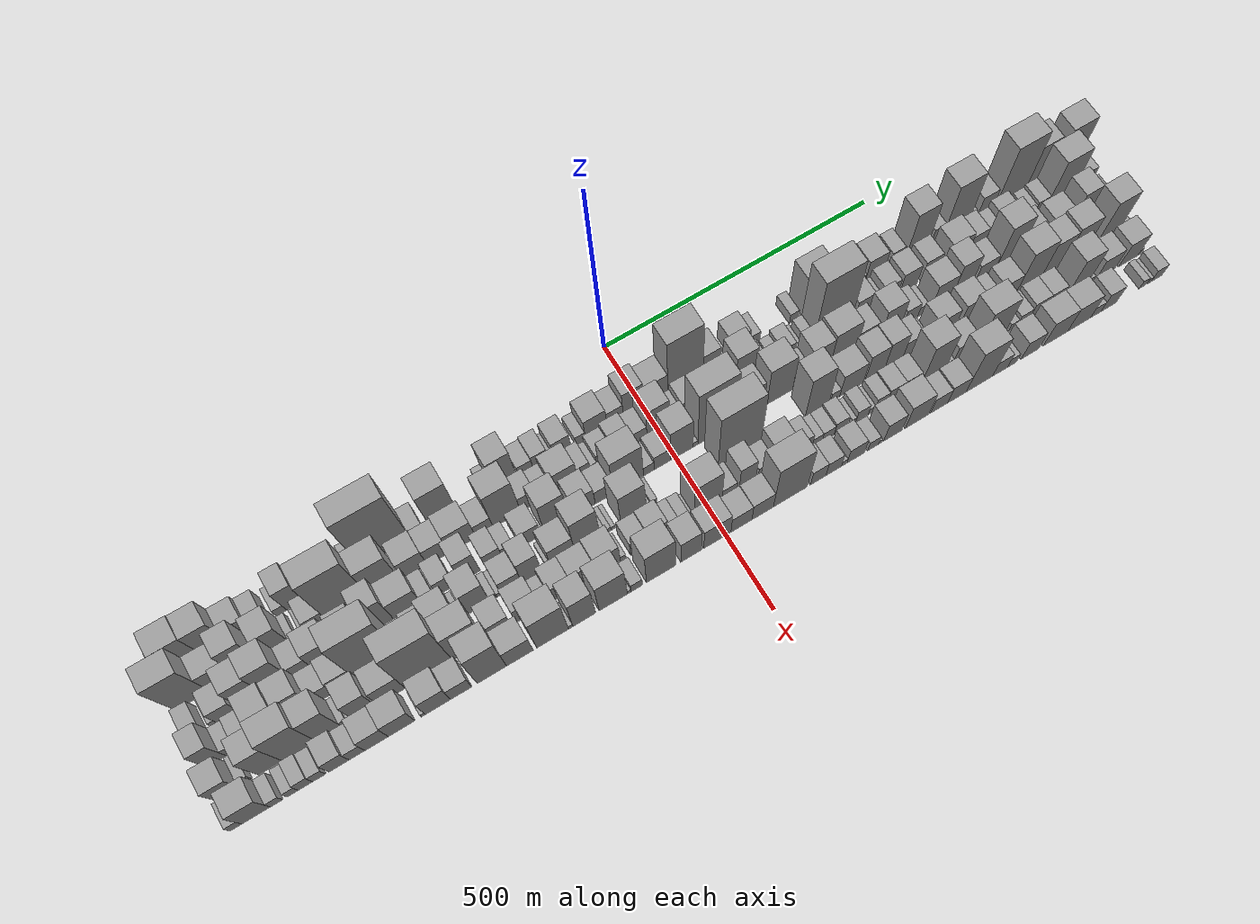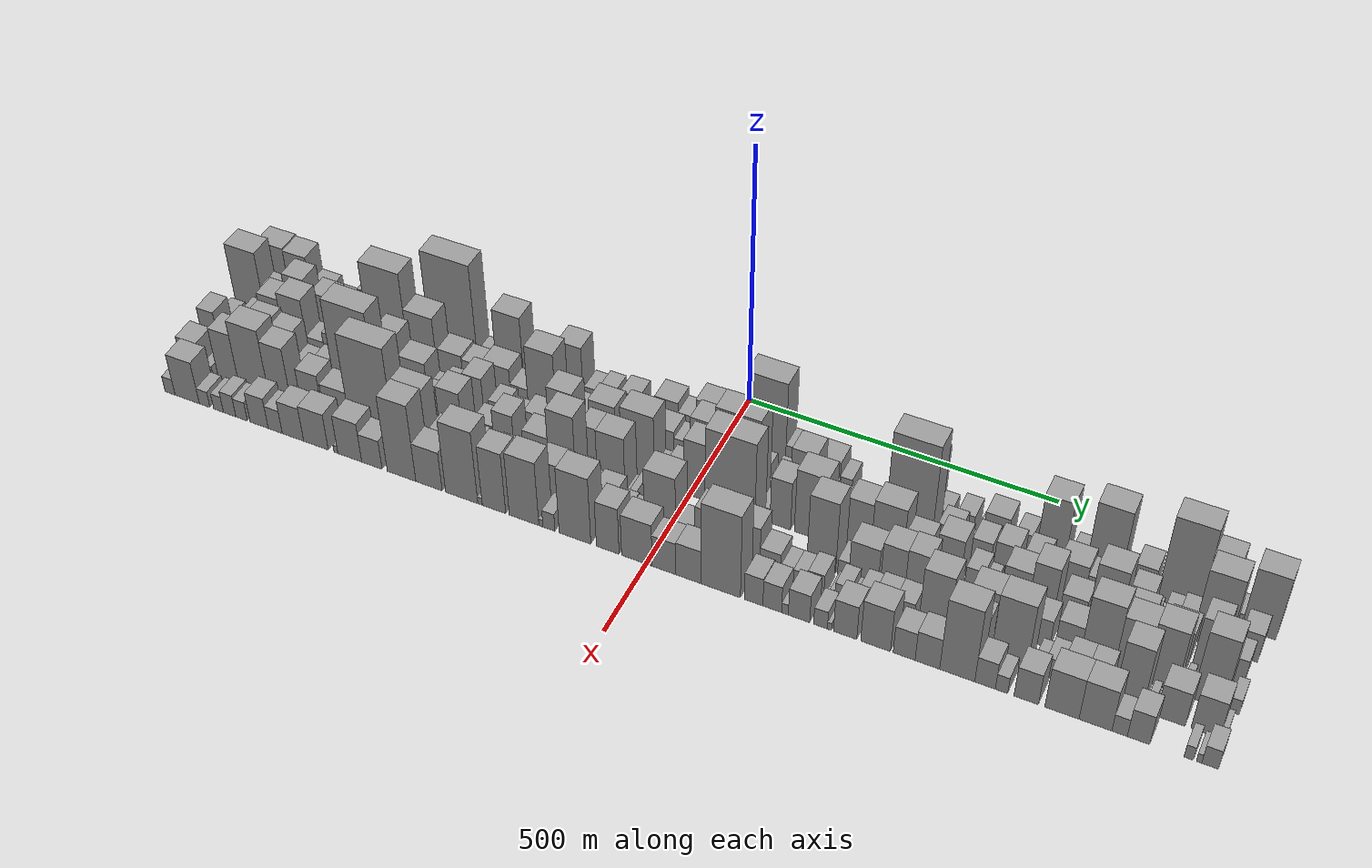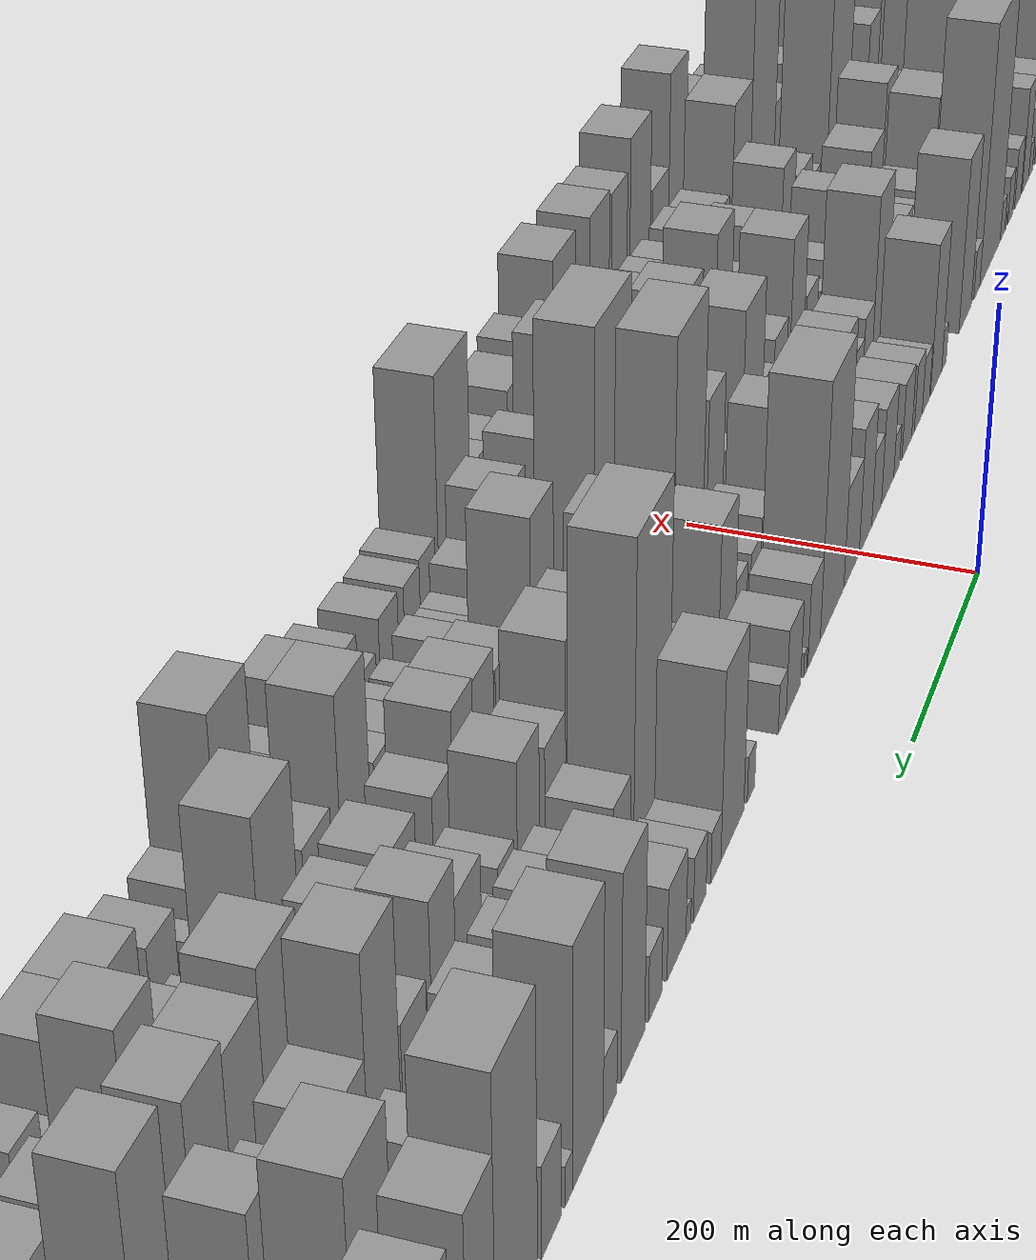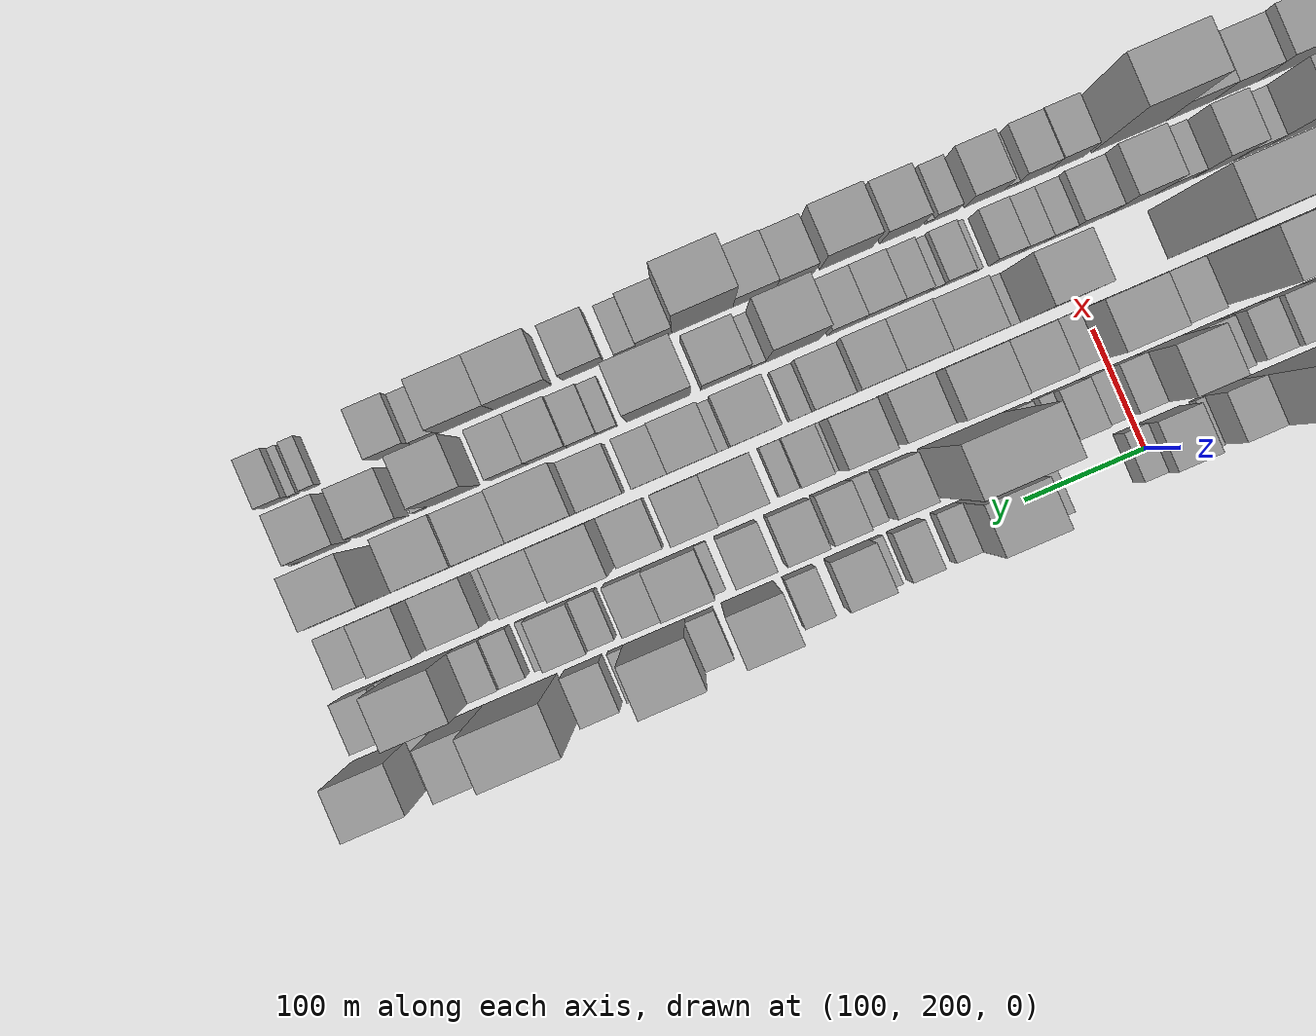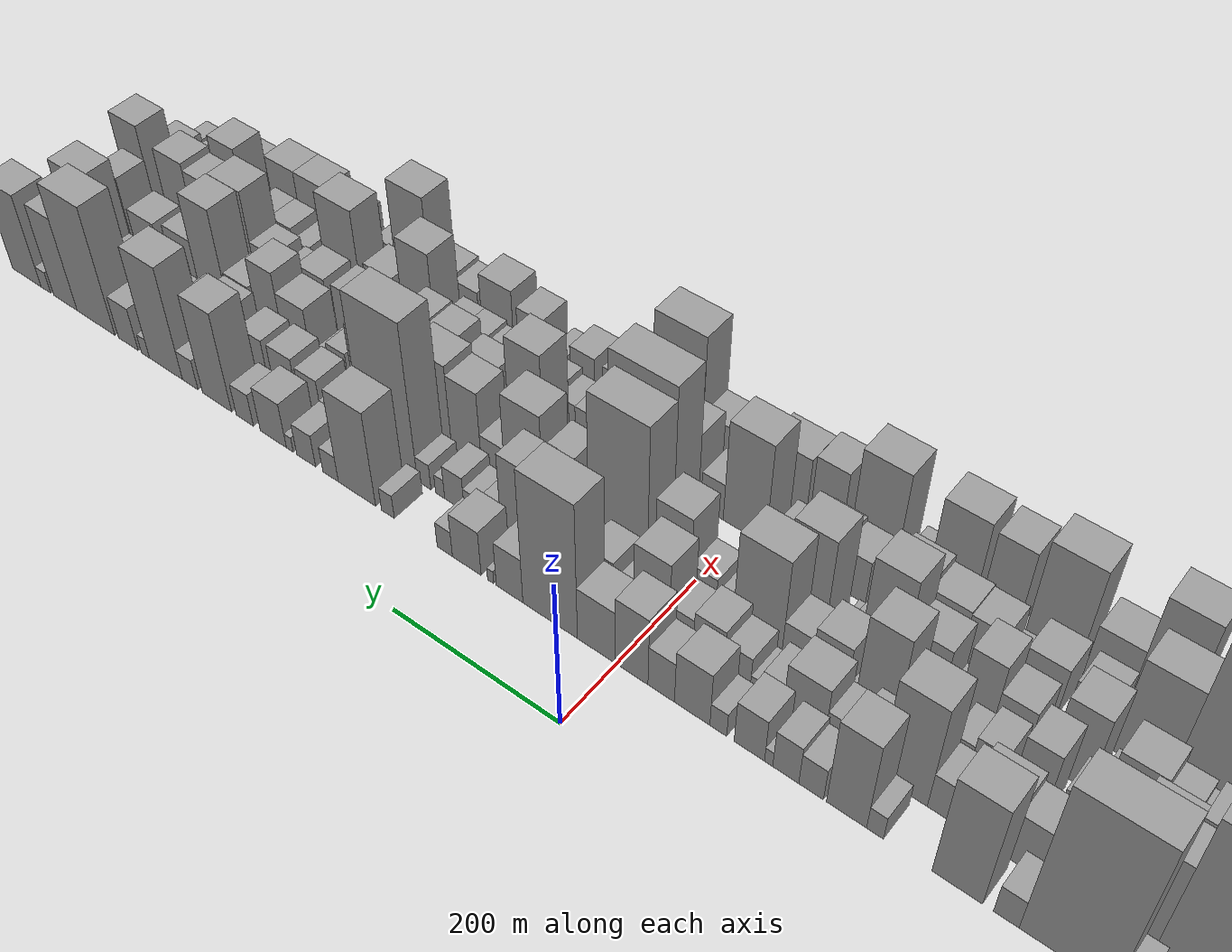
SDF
<sdf version="1.6">
 <world name="default">
  <scene>
   <sky><clouds><speed>12</speed></clouds></sky>
   <ambient>0.4 0.4 0.4 1</ambient>
   <background>0.7 0.7 0.7 1</background>
   <shadows>1</shadows>
  </scene>
  <gravity>0 0 -9.8066</gravity>
  <magnetic_field>6e-06 2.3e-05 -4.2e-05</magnetic_field>
  <physics default="0" name="default_physics" type="ode">
   <ode>
    <solver>
     <type>quick</type>
     <iters>10</iters>
     <sor>1.0</sor>
     <use_dynamic_moi_rescaling>0</use_dynamic_moi_rescaling>
    </solver>
    <constraints>
     <cfm>0</cfm>
     <erp>0.2</erp>
     <contact_max_correcting_vel>100</contact_max_correcting_vel>
     <contact_surface_layer>0.001</contact_surface_layer>
    </constraints>
   </ode>
   <max_step_size>0.004</max_step_size>
   <real_time_factor>1</real_time_factor>
   <real_time_update_rate>250</real_time_update_rate>
  </physics>
  <light name="sun" type="directional">
   <pose>0 0 10 0 0 0</pose>
   <diffuse>0.8 0.8 0.8 1</diffuse>
   <specular>0.2 0.2 0.2 1</specular>
   <attenuation>
    <range>1000</range>
    <constant>0.9</constant>
    <linear>0.01</linear>
    <quadratic>0.001</quadratic>
   </attenuation>
   <direction>-0.5 0.1 -0.9</direction>
  </light>
  <model name="building_1">
   <static>1</static>
   <pose>100.0000 -812.2240 0 0.000000 0.000000 0.000000</pose>
   <link name="link">
    <pose>0 0 19.50 0 0 0</pose>
    <collision name="collision"><geometry><box><size>40.0000 21.5519 39.0000</size></box></geometry></collision>
    <visual name="visual">
     <cast_shadows>0</cast_shadows>
     <geometry><box><size>40.0000 21.5519 39.0000</size></box></geometry>
     <material>
      <script>
       <uri>model://grey_wall/materials/scripts</uri>
       <uri>model://grey_wall/materials/textures</uri>
       <name>vrc/grey_wall</name>
      </script>
     </material>
    </visual>
   </link>
  </model>
  <model name="building_2">
   <static>1</static>
   <pose>100.0000 -777.5045 0 0.000000 0.000000 0.000000</pose>
   <link name="link">
    <pose>0 0 63.00 0 0 0</pose>
    <collision name="collision"><geometry><box><size>40.0000 47.8872 126.0000</size></box></geometry></collision>
    <visual name="visual">
     <cast_shadows>0</cast_shadows>
     <geometry><box><size>40.0000 47.8872 126.0000</size></box></geometry>
     <material>
      <script>
       <uri>model://grey_wall/materials/scripts</uri>
       <uri>model://grey_wall/materials/textures</uri>
       <name>vrc/grey_wall</name>
      </script>
     </material>
    </visual>
   </link>
  </model>
  <model name="building_3">
   <static>1</static>
   <pose>100.0000 -732.9101 0 0.000000 0.000000 0.000000</pose>
   <link name="link">
    <pose>0 0 61.50 0 0 0</pose>
    <collision name="collision"><geometry><box><size>40.0000 41.3015 123.0000</size></box></geometry></collision>
    <visual name="visual">
     <cast_shadows>0</cast_shadows>
     <geometry><box><size>40.0000 41.3015 123.0000</size></box></geometry>
     <material>
      <script>
       <uri>model://grey_wall/materials/scripts</uri>
       <uri>model://grey_wall/materials/textures</uri>
       <name>vrc/grey_wall</name>
      </script>
     </material>
    </visual>
   </link>
  </model>
  <model name="building_4">
   <static>1</static>
   <pose>100.0000 -693.9835 0 0.000000 0.000000 0.000000</pose>
   <link name="link">
    <pose>0 0 34.50 0 0 0</pose>
    <collision name="collision"><geometry><box><size>40.0000 36.5518 69.0000</size></box></geometry></collision>
    <visual name="visual">
     <cast_shadows>0</cast_shadows>
     <geometry><box><size>40.0000 36.5518 69.0000</size></box></geometry>
     <material>
      <script>
       <uri>model://grey_wall/materials/scripts</uri>
       <uri>model://grey_wall/materials/textures</uri>
       <name>vrc/grey_wall</name>
      </script>
     </material>
    </visual>
   </link>
  </model>
  <model name="building_5">
   <static>1</static>
   <pose>100.0000 -662.1892 0 0.000000 0.000000 0.000000</pose>
   <link name="link">
    <pose>0 0 25.50 0 0 0</pose>
    <collision name="collision"><geometry><box><size>40.0000 27.0368 51.0000</size></box></geometry></collision>
    <visual name="visual">
     <cast_shadows>0</cast_shadows>
     <geometry><box><size>40.0000 27.0368 51.0000</size></box></geometry>
     <material>
      <script>
       <uri>model://grey_wall/materials/scripts</uri>
       <uri>model://grey_wall/materials/textures</uri>
       <name>vrc/grey_wall</name>
      </script>
     </material>
    </visual>
   </link>
  </model>
  <model name="building_6">
   <static>1</static>
   <pose>100.0000 -629.9079 0 0.000000 0.000000 0.000000</pose>
   <link name="link">
    <pose>0 0 15.00 0 0 0</pose>
    <collision name="collision"><geometry><box><size>40.0000 17.5258 30.0000</size></box></geometry></collision>
    <visual name="visual">
     <cast_shadows>0</cast_shadows>
     <geometry><box><size>40.0000 17.5258 30.0000</size></box></geometry>
     <material>
      <script>
       <uri>model://grey_wall/materials/scripts</uri>
       <uri>model://grey_wall/materials/textures</uri>
       <name>vrc/grey_wall</name>
      </script>
     </material>
    </visual>
   </link>
  </model>
  <model name="building_7">
   <static>1</static>
   <pose>100.0000 -606.0074 0 0.000000 0.000000 0.000000</pose>
   <link name="link">
    <pose>0 0 46.50 0 0 0</pose>
    <collision name="collision"><geometry><box><size>40.0000 30.2752 93.0000</size></box></geometry></collision>
    <visual name="visual">
     <cast_shadows>0</cast_shadows>
     <geometry><box><size>40.0000 30.2752 93.0000</size></box></geometry>
     <material>
      <script>
       <uri>model://grey_wall/materials/scripts</uri>
       <uri>model://grey_wall/materials/textures</uri>
       <name>vrc/grey_wall</name>
      </script>
     </material>
    </visual>
   </link>
  </model>
  <model name="building_8">
   <static>1</static>
   <pose>100.0000 -571.5344 0 0.000000 0.000000 0.000000</pose>
   <link name="link">
    <pose>0 0 27.00 0 0 0</pose>
    <collision name="collision"><geometry><box><size>40.0000 28.6708 54.0000</size></box></geometry></collision>
    <visual name="visual">
     <cast_shadows>0</cast_shadows>
     <geometry><box><size>40.0000 28.6708 54.0000</size></box></geometry>
     <material>
      <script>
       <uri>model://grey_wall/materials/scripts</uri>
       <uri>model://grey_wall/materials/textures</uri>
       <name>vrc/grey_wall</name>
      </script>
     </material>
    </visual>
   </link>
  </model>
  <model name="building_9">
   <static>1</static>
   <pose>100.0000 -538.3855 0 0.000000 0.000000 0.000000</pose>
   <link name="link">
    <pose>0 0 21.00 0 0 0</pose>
    <collision name="collision"><geometry><box><size>40.0000 21.6271 42.0000</size></box></geometry></collision>
    <visual name="visual">
     <cast_shadows>0</cast_shadows>
     <geometry><box><size>40.0000 21.6271 42.0000</size></box></geometry>
     <material>
      <script>
       <uri>model://grey_wall/materials/scripts</uri>
       <uri>model://grey_wall/materials/textures</uri>
       <name>vrc/grey_wall</name>
      </script>
     </material>
    </visual>
   </link>
  </model>
  <model name="building_10">
   <static>1</static>
   <pose>100.0000 -518.0808 0 0.000000 0.000000 0.000000</pose>
   <link name="link">
    <pose>0 0 7.50 0 0 0</pose>
    <collision name="collision"><geometry><box><size>40.0000 6.9822 15.0000</size></box></geometry></collision>
    <visual name="visual">
     <cast_shadows>0</cast_shadows>
     <geometry><box><size>40.0000 6.9822 15.0000</size></box></geometry>
     <material>
      <script>
       <uri>model://grey_wall/materials/scripts</uri>
       <uri>model://grey_wall/materials/textures</uri>
       <name>vrc/grey_wall</name>
      </script>
     </material>
    </visual>
   </link>
  </model>
  <model name="building_11">
   <static>1</static>
   <pose>100.0000 -505.0342 0 0.000000 0.000000 0.000000</pose>
   <link name="link">
    <pose>0 0 16.50 0 0 0</pose>
    <collision name="collision"><geometry><box><size>40.0000 19.1111 33.0000</size></box></geometry></collision>
    <visual name="visual">
     <cast_shadows>0</cast_shadows>
     <geometry><box><size>40.0000 19.1111 33.0000</size></box></geometry>
     <material>
      <script>
       <uri>model://grey_wall/materials/scripts</uri>
       <uri>model://grey_wall/materials/textures</uri>
       <name>vrc/grey_wall</name>
      </script>
     </material>
    </visual>
   </link>
  </model>
  <model name="building_12">
   <static>1</static>
   <pose>100.0000 -453.3071 0 0.000000 0.000000 0.000000</pose>
   <link name="link">
    <pose>0 0 109.50 0 0 0</pose>
    <collision name="collision"><geometry><box><size>40.0000 84.3429 219.0000</size></box></geometry></collision>
    <visual name="visual">
     <cast_shadows>0</cast_shadows>
     <geometry><box><size>40.0000 84.3429 219.0000</size></box></geometry>
     <material>
      <script>
       <uri>model://grey_wall/materials/scripts</uri>
       <uri>model://grey_wall/materials/textures</uri>
       <name>vrc/grey_wall</name>
      </script>
     </material>
    </visual>
   </link>
  </model>
  <model name="building_13">
   <static>1</static>
   <pose>100.0000 -399.4121 0 0.000000 0.000000 0.000000</pose>
   <link name="link">
    <pose>0 0 21.00 0 0 0</pose>
    <collision name="collision"><geometry><box><size>40.0000 23.4472 42.0000</size></box></geometry></collision>
    <visual name="visual">
     <cast_shadows>0</cast_shadows>
     <geometry><box><size>40.0000 23.4472 42.0000</size></box></geometry>
     <material>
      <script>
       <uri>model://grey_wall/materials/scripts</uri>
       <uri>model://grey_wall/materials/textures</uri>
       <name>vrc/grey_wall</name>
      </script>
     </material>
    </visual>
   </link>
  </model>
  <model name="building_14">
   <static>1</static>
   <pose>100.0000 -353.8614 0 0.000000 0.000000 0.000000</pose>
   <link name="link">
    <pose>0 0 72.00 0 0 0</pose>
    <collision name="collision"><geometry><box><size>40.0000 47.6542 144.0000</size></box></geometry></collision>
    <visual name="visual">
     <cast_shadows>0</cast_shadows>
     <geometry><box><size>40.0000 47.6542 144.0000</size></box></geometry>
     <material>
      <script>
       <uri>model://grey_wall/materials/scripts</uri>
       <uri>model://grey_wall/materials/textures</uri>
       <name>vrc/grey_wall</name>
      </script>
     </material>
    </visual>
   </link>
  </model>
  <model name="building_15">
   <static>1</static>
   <pose>100.0000 -274.9148 0 0.000000 0.000000 0.000000</pose>
   <link name="link">
    <pose>0 0 16.50 0 0 0</pose>
    <collision name="collision"><geometry><box><size>40.0000 16.7463 33.0000</size></box></geometry></collision>
    <visual name="visual">
     <cast_shadows>0</cast_shadows>
     <geometry><box><size>40.0000 16.7463 33.0000</size></box></geometry>
     <material>
      <script>
       <uri>model://grey_wall/materials/scripts</uri>
       <uri>model://grey_wall/materials/textures</uri>
       <name>vrc/grey_wall</name>
      </script>
     </material>
    </visual>
   </link>
  </model>
  <model name="building_16">
   <static>1</static>
   <pose>100.0000 -246.4983 0 0.000000 0.000000 0.000000</pose>
   <link name="link">
    <pose>0 0 61.50 0 0 0</pose>
    <collision name="collision"><geometry><box><size>40.0000 40.0867 123.0000</size></box></geometry></collision>
    <visual name="visual">
     <cast_shadows>0</cast_shadows>
     <geometry><box><size>40.0000 40.0867 123.0000</size></box></geometry>
     <material>
      <script>
       <uri>model://grey_wall/materials/scripts</uri>
       <uri>model://grey_wall/materials/textures</uri>
       <name>vrc/grey_wall</name>
      </script>
     </material>
    </visual>
   </link>
  </model>
  <model name="building_17">
   <static>1</static>
   <pose>100.0000 -210.7944 0 0.000000 0.000000 0.000000</pose>
   <link name="link">
    <pose>0 0 22.50 0 0 0</pose>
    <collision name="collision"><geometry><box><size>40.0000 25.3211 45.0000</size></box></geometry></collision>
    <visual name="visual">
     <cast_shadows>0</cast_shadows>
     <geometry><box><size>40.0000 25.3211 45.0000</size></box></geometry>
     <material>
      <script>
       <uri>model://grey_wall/materials/scripts</uri>
       <uri>model://grey_wall/materials/textures</uri>
       <name>vrc/grey_wall</name>
      </script>
     </material>
    </visual>
   </link>
  </model>
  <model name="building_18">
   <static>1</static>
   <pose>100.0000 -184.6230 0 0.000000 0.000000 0.000000</pose>
   <link name="link">
    <pose>0 0 27.00 0 0 0</pose>
    <collision name="collision"><geometry><box><size>40.0000 27.0217 54.0000</size></box></geometry></collision>
    <visual name="visual">
     <cast_shadows>0</cast_shadows>
     <geometry><box><size>40.0000 27.0217 54.0000</size></box></geometry>
     <material>
      <script>
       <uri>model://grey_wall/materials/scripts</uri>
       <uri>model://grey_wall/materials/textures</uri>
       <name>vrc/grey_wall</name>
      </script>
     </material>
    </visual>
   </link>
  </model>
  <model name="building_19">
   <static>1</static>
   <pose>100.0000 -166.8143 0 0.000000 0.000000 0.000000</pose>
   <link name="link">
    <pose>0 0 10.50 0 0 0</pose>
    <collision name="collision"><geometry><box><size>40.0000 8.5957 21.0000</size></box></geometry></collision>
    <visual name="visual">
     <cast_shadows>0</cast_shadows>
     <geometry><box><size>40.0000 8.5957 21.0000</size></box></geometry>
     <material>
      <script>
       <uri>model://grey_wall/materials/scripts</uri>
       <uri>model://grey_wall/materials/textures</uri>
       <name>vrc/grey_wall</name>
      </script>
     </material>
    </visual>
   </link>
  </model>
  <model name="building_20">
   <static>1</static>
   <pose>100.0000 -146.4526 0 0.000000 0.000000 0.000000</pose>
   <link name="link">
    <pose>0 0 30.00 0 0 0</pose>
    <collision name="collision"><geometry><box><size>40.0000 32.1276 60.0000</size></box></geometry></collision>
    <visual name="visual">
     <cast_shadows>0</cast_shadows>
     <geometry><box><size>40.0000 32.1276 60.0000</size></box></geometry>
     <material>
      <script>
       <uri>model://grey_wall/materials/scripts</uri>
       <uri>model://grey_wall/materials/textures</uri>
       <name>vrc/grey_wall</name>
      </script>
     </material>
    </visual>
   </link>
  </model>
  <model name="building_21">
   <static>1</static>
   <pose>100.0000 -113.3025 0 0.000000 0.000000 0.000000</pose>
   <link name="link">
    <pose>0 0 16.50 0 0 0</pose>
    <collision name="collision"><geometry><box><size>40.0000 18.1728 33.0000</size></box></geometry></collision>
    <visual name="visual">
     <cast_shadows>0</cast_shadows>
     <geometry><box><size>40.0000 18.1728 33.0000</size></box></geometry>
     <material>
      <script>
       <uri>model://grey_wall/materials/scripts</uri>
       <uri>model://grey_wall/materials/textures</uri>
       <name>vrc/grey_wall</name>
      </script>
     </material>
    </visual>
   </link>
  </model>
  <model name="building_22">
   <static>1</static>
   <pose>100.0000 -84.8160 0 0.000000 0.000000 0.000000</pose>
   <link name="link">
    <pose>0 0 37.50 0 0 0</pose>
    <collision name="collision"><geometry><box><size>40.0000 38.8002 75.0000</size></box></geometry></collision>
    <visual name="visual">
     <cast_shadows>0</cast_shadows>
     <geometry><box><size>40.0000 38.8002 75.0000</size></box></geometry>
     <material>
      <script>
       <uri>model://grey_wall/materials/scripts</uri>
       <uri>model://grey_wall/materials/textures</uri>
       <name>vrc/grey_wall</name>
      </script>
     </material>
    </visual>
   </link>
  </model>
  <model name="building_23">
   <static>1</static>
   <pose>100.0000 -50.5812 0 0.000000 0.000000 0.000000</pose>
   <link name="link">
    <pose>0 0 28.50 0 0 0</pose>
    <collision name="collision"><geometry><box><size>40.0000 29.6695 57.0000</size></box></geometry></collision>
    <visual name="visual">
     <cast_shadows>0</cast_shadows>
     <geometry><box><size>40.0000 29.6695 57.0000</size></box></geometry>
     <material>
      <script>
       <uri>model://grey_wall/materials/scripts</uri>
       <uri>model://grey_wall/materials/textures</uri>
       <name>vrc/grey_wall</name>
      </script>
     </material>
    </visual>
   </link>
  </model>
  <model name="building_24">
   <static>1</static>
   <pose>100.0000 -17.0833 0 0.000000 0.000000 0.000000</pose>
   <link name="link">
    <pose>0 0 48.00 0 0 0</pose>
    <collision name="collision"><geometry><box><size>40.0000 37.3264 96.0000</size></box></geometry></collision>
    <visual name="visual">
     <cast_shadows>0</cast_shadows>
     <geometry><box><size>40.0000 37.3264 96.0000</size></box></geometry>
     <material>
      <script>
       <uri>model://grey_wall/materials/scripts</uri>
       <uri>model://grey_wall/materials/textures</uri>
       <name>vrc/grey_wall</name>
      </script>
     </material>
    </visual>
   </link>
  </model>
  <model name="building_25">
   <static>1</static>
   <pose>100.0000 23.4848 0 0.000000 0.000000 0.000000</pose>
   <link name="link">
    <pose>0 0 37.50 0 0 0</pose>
    <collision name="collision"><geometry><box><size>40.0000 43.8097 75.0000</size></box></geometry></collision>
    <visual name="visual">
     <cast_shadows>0</cast_shadows>
     <geometry><box><size>40.0000 43.8097 75.0000</size></box></geometry>
     <material>
      <script>
       <uri>model://grey_wall/materials/scripts</uri>
       <uri>model://grey_wall/materials/textures</uri>
       <name>vrc/grey_wall</name>
      </script>
     </material>
    </visual>
   </link>
  </model>
  <model name="building_26">
   <static>1</static>
   <pose>100.0000 78.0372 0 0.000000 0.000000 0.000000</pose>
   <link name="link">
    <pose>0 0 94.50 0 0 0</pose>
    <collision name="collision"><geometry><box><size>40.0000 65.2951 189.0000</size></box></geometry></collision>
    <visual name="visual">
     <cast_shadows>0</cast_shadows>
     <geometry><box><size>40.0000 65.2951 189.0000</size></box></geometry>
     <material>
      <script>
       <uri>model://grey_wall/materials/scripts</uri>
       <uri>model://grey_wall/materials/textures</uri>
       <name>vrc/grey_wall</name>
      </script>
     </material>
    </visual>
   </link>
  </model>
  <model name="building_27">
   <static>1</static>
   <pose>100.0000 127.0453 0 0.000000 0.000000 0.000000</pose>
   <link name="link">
    <pose>0 0 31.50 0 0 0</pose>
    <collision name="collision"><geometry><box><size>40.0000 32.7209 63.0000</size></box></geometry></collision>
    <visual name="visual">
     <cast_shadows>0</cast_shadows>
     <geometry><box><size>40.0000 32.7209 63.0000</size></box></geometry>
     <material>
      <script>
       <uri>model://grey_wall/materials/scripts</uri>
       <uri>model://grey_wall/materials/textures</uri>
       <name>vrc/grey_wall</name>
      </script>
     </material>
    </visual>
   </link>
  </model>
  <model name="building_28">
   <static>1</static>
   <pose>100.0000 150.3238 0 0.000000 0.000000 0.000000</pose>
   <link name="link">
    <pose>0 0 9.00 0 0 0</pose>
    <collision name="collision"><geometry><box><size>40.0000 7.8362 18.0000</size></box></geometry></collision>
    <visual name="visual">
     <cast_shadows>0</cast_shadows>
     <geometry><box><size>40.0000 7.8362 18.0000</size></box></geometry>
     <material>
      <script>
       <uri>model://grey_wall/materials/scripts</uri>
       <uri>model://grey_wall/materials/textures</uri>
       <name>vrc/grey_wall</name>
      </script>
     </material>
    </visual>
   </link>
  </model>
  <model name="building_29">
   <static>1</static>
   <pose>100.0000 180.3429 0 0.000000 0.000000 0.000000</pose>
   <link name="link">
    <pose>0 0 31.50 0 0 0</pose>
    <collision name="collision"><geometry><box><size>40.0000 36.2020 63.0000</size></box></geometry></collision>
    <visual name="visual">
     <cast_shadows>0</cast_shadows>
     <geometry><box><size>40.0000 36.2020 63.0000</size></box></geometry>
     <material>
      <script>
       <uri>model://grey_wall/materials/scripts</uri>
       <uri>model://grey_wall/materials/textures</uri>
       <name>vrc/grey_wall</name>
      </script>
     </material>
    </visual>
   </link>
  </model>
  <model name="building_30">
   <static>1</static>
   <pose>100.0000 208.2000 0 0.000000 0.000000 0.000000</pose>
   <link name="link">
    <pose>0 0 18.00 0 0 0</pose>
    <collision name="collision"><geometry><box><size>40.0000 19.5122 36.0000</size></box></geometry></collision>
    <visual name="visual">
     <cast_shadows>0</cast_shadows>
     <geometry><box><size>40.0000 19.5122 36.0000</size></box></geometry>
     <material>
      <script>
       <uri>model://grey_wall/materials/scripts</uri>
       <uri>model://grey_wall/materials/textures</uri>
       <name>vrc/grey_wall</name>
      </script>
     </material>
    </visual>
   </link>
  </model>
  <model name="building_31">
   <static>1</static>
   <pose>100.0000 282.5096 0 0.000000 0.000000 0.000000</pose>
   <link name="link">
    <pose>0 0 16.50 0 0 0</pose>
    <collision name="collision"><geometry><box><size>40.0000 17.0357 33.0000</size></box></geometry></collision>
    <visual name="visual">
     <cast_shadows>0</cast_shadows>
     <geometry><box><size>40.0000 17.0357 33.0000</size></box></geometry>
     <material>
      <script>
       <uri>model://grey_wall/materials/scripts</uri>
       <uri>model://grey_wall/materials/textures</uri>
       <name>vrc/grey_wall</name>
      </script>
     </material>
    </visual>
   </link>
  </model>
  <model name="building_32">
   <static>1</static>
   <pose>100.0000 324.3097 0 0.000000 0.000000 0.000000</pose>
   <link name="link">
    <pose>0 0 66.00 0 0 0</pose>
    <collision name="collision"><geometry><box><size>40.0000 50.5646 132.0000</size></box></geometry></collision>
    <visual name="visual">
     <cast_shadows>0</cast_shadows>
     <geometry><box><size>40.0000 50.5646 132.0000</size></box></geometry>
     <material>
      <script>
       <uri>model://grey_wall/materials/scripts</uri>
       <uri>model://grey_wall/materials/textures</uri>
       <name>vrc/grey_wall</name>
      </script>
     </material>
    </visual>
   </link>
  </model>
  <model name="building_33">
   <static>1</static>
   <pose>100.0000 360.3761 0 0.000000 0.000000 0.000000</pose>
   <link name="link">
    <pose>0 0 18.00 0 0 0</pose>
    <collision name="collision"><geometry><box><size>40.0000 21.5682 36.0000</size></box></geometry></collision>
    <visual name="visual">
     <cast_shadows>0</cast_shadows>
     <geometry><box><size>40.0000 21.5682 36.0000</size></box></geometry>
     <material>
      <script>
       <uri>model://grey_wall/materials/scripts</uri>
       <uri>model://grey_wall/materials/textures</uri>
       <name>vrc/grey_wall</name>
      </script>
     </material>
    </visual>
   </link>
  </model>
  <model name="building_34">
   <static>1</static>
   <pose>100.0000 394.4054 0 0.000000 0.000000 0.000000</pose>
   <link name="link">
    <pose>0 0 22.50 0 0 0</pose>
    <collision name="collision"><geometry><box><size>40.0000 26.4903 45.0000</size></box></geometry></collision>
    <visual name="visual">
     <cast_shadows>0</cast_shadows>
     <geometry><box><size>40.0000 26.4903 45.0000</size></box></geometry>
     <material>
      <script>
       <uri>model://grey_wall/materials/scripts</uri>
       <uri>model://grey_wall/materials/textures</uri>
       <name>vrc/grey_wall</name>
      </script>
     </material>
    </visual>
   </link>
  </model>
  <model name="building_35">
   <static>1</static>
   <pose>100.0000 417.4979 0 0.000000 0.000000 0.000000</pose>
   <link name="link">
    <pose>0 0 10.50 0 0 0</pose>
    <collision name="collision"><geometry><box><size>40.0000 9.6946 21.0000</size></box></geometry></collision>
    <visual name="visual">
     <cast_shadows>0</cast_shadows>
     <geometry><box><size>40.0000 9.6946 21.0000</size></box></geometry>
     <material>
      <script>
       <uri>model://grey_wall/materials/scripts</uri>
       <uri>model://grey_wall/materials/textures</uri>
       <name>vrc/grey_wall</name>
      </script>
     </material>
    </visual>
   </link>
  </model>
  <model name="building_36">
   <static>1</static>
   <pose>100.0000 441.1656 0 0.000000 0.000000 0.000000</pose>
   <link name="link">
    <pose>0 0 31.50 0 0 0</pose>
    <collision name="collision"><geometry><box><size>40.0000 37.6408 63.0000</size></box></geometry></collision>
    <visual name="visual">
     <cast_shadows>0</cast_shadows>
     <geometry><box><size>40.0000 37.6408 63.0000</size></box></geometry>
     <material>
      <script>
       <uri>model://grey_wall/materials/scripts</uri>
       <uri>model://grey_wall/materials/textures</uri>
       <name>vrc/grey_wall</name>
      </script>
     </material>
    </visual>
   </link>
  </model>
  <model name="building_37">
   <static>1</static>
   <pose>100.0000 482.5473 0 0.000000 0.000000 0.000000</pose>
   <link name="link">
    <pose>0 0 22.50 0 0 0</pose>
    <collision name="collision"><geometry><box><size>40.0000 25.1226 45.0000</size></box></geometry></collision>
    <visual name="visual">
     <cast_shadows>0</cast_shadows>
     <geometry><box><size>40.0000 25.1226 45.0000</size></box></geometry>
     <material>
      <script>
       <uri>model://grey_wall/materials/scripts</uri>
       <uri>model://grey_wall/materials/textures</uri>
       <name>vrc/grey_wall</name>
      </script>
     </material>
    </visual>
   </link>
  </model>
  <model name="building_38">
   <static>1</static>
   <pose>100.0000 523.8339 0 0.000000 0.000000 0.000000</pose>
   <link name="link">
    <pose>0 0 69.00 0 0 0</pose>
    <collision name="collision"><geometry><box><size>40.0000 43.4507 138.0000</size></box></geometry></collision>
    <visual name="visual">
     <cast_shadows>0</cast_shadows>
     <geometry><box><size>40.0000 43.4507 138.0000</size></box></geometry>
     <material>
      <script>
       <uri>model://grey_wall/materials/scripts</uri>
       <uri>model://grey_wall/materials/textures</uri>
       <name>vrc/grey_wall</name>
      </script>
     </material>
    </visual>
   </link>
  </model>
  <model name="building_39">
   <static>1</static>
   <pose>100.0000 564.3673 0 0.000000 0.000000 0.000000</pose>
   <link name="link">
    <pose>0 0 21.00 0 0 0</pose>
    <collision name="collision"><geometry><box><size>40.0000 23.6162 42.0000</size></box></geometry></collision>
    <visual name="visual">
     <cast_shadows>0</cast_shadows>
     <geometry><box><size>40.0000 23.6162 42.0000</size></box></geometry>
     <material>
      <script>
       <uri>model://grey_wall/materials/scripts</uri>
       <uri>model://grey_wall/materials/textures</uri>
       <name>vrc/grey_wall</name>
      </script>
     </material>
    </visual>
   </link>
  </model>
  <model name="building_40">
   <static>1</static>
   <pose>100.0000 601.8708 0 0.000000 0.000000 0.000000</pose>
   <link name="link">
    <pose>0 0 78.00 0 0 0</pose>
    <collision name="collision"><geometry><box><size>40.0000 51.3907 156.0000</size></box></geometry></collision>
    <visual name="visual">
     <cast_shadows>0</cast_shadows>
     <geometry><box><size>40.0000 51.3907 156.0000</size></box></geometry>
     <material>
      <script>
       <uri>model://grey_wall/materials/scripts</uri>
       <uri>model://grey_wall/materials/textures</uri>
       <name>vrc/grey_wall</name>
      </script>
     </material>
    </visual>
   </link>
  </model>
  <model name="building_41">
   <static>1</static>
   <pose>100.0000 633.8620 0 0.000000 0.000000 0.000000</pose>
   <link name="link">
    <pose>0 0 13.50 0 0 0</pose>
    <collision name="collision"><geometry><box><size>40.0000 12.5917 27.0000</size></box></geometry></collision>
    <visual name="visual">
     <cast_shadows>0</cast_shadows>
     <geometry><box><size>40.0000 12.5917 27.0000</size></box></geometry>
     <material>
      <script>
       <uri>model://grey_wall/materials/scripts</uri>
       <uri>model://grey_wall/materials/textures</uri>
       <name>vrc/grey_wall</name>
      </script>
     </material>
    </visual>
   </link>
  </model>
  <model name="building_42">
   <static>1</static>
   <pose>100.0000 660.8852 0 0.000000 0.000000 0.000000</pose>
   <link name="link">
    <pose>0 0 30.00 0 0 0</pose>
    <collision name="collision"><geometry><box><size>40.0000 31.4549 60.0000</size></box></geometry></collision>
    <visual name="visual">
     <cast_shadows>0</cast_shadows>
     <geometry><box><size>40.0000 31.4549 60.0000</size></box></geometry>
     <material>
      <script>
       <uri>model://grey_wall/materials/scripts</uri>
       <uri>model://grey_wall/materials/textures</uri>
       <name>vrc/grey_wall</name>
      </script>
     </material>
    </visual>
   </link>
  </model>
  <model name="building_43">
   <static>1</static>
   <pose>100.0000 713.4635 0 0.000000 0.000000 0.000000</pose>
   <link name="link">
    <pose>0 0 88.50 0 0 0</pose>
    <collision name="collision"><geometry><box><size>40.0000 61.7016 177.0000</size></box></geometry></collision>
    <visual name="visual">
     <cast_shadows>0</cast_shadows>
     <geometry><box><size>40.0000 61.7016 177.0000</size></box></geometry>
     <material>
      <script>
       <uri>model://grey_wall/materials/scripts</uri>
       <uri>model://grey_wall/materials/textures</uri>
       <name>vrc/grey_wall</name>
      </script>
     </material>
    </visual>
   </link>
  </model>
  <model name="building_44">
   <static>1</static>
   <pose>100.0000 763.8396 0 0.000000 0.000000 0.000000</pose>
   <link name="link">
    <pose>0 0 64.50 0 0 0</pose>
    <collision name="collision"><geometry><box><size>40.0000 39.0508 129.0000</size></box></geometry></collision>
    <visual name="visual">
     <cast_shadows>0</cast_shadows>
     <geometry><box><size>40.0000 39.0508 129.0000</size></box></geometry>
     <material>
      <script>
       <uri>model://grey_wall/materials/scripts</uri>
       <uri>model://grey_wall/materials/textures</uri>
       <name>vrc/grey_wall</name>
      </script>
     </material>
    </visual>
   </link>
  </model>
  <model name="building_45">
   <static>1</static>
   <pose>100.0000 796.4080 0 0.000000 0.000000 0.000000</pose>
   <link name="link">
    <pose>0 0 15.00 0 0 0</pose>
    <collision name="collision"><geometry><box><size>40.0000 16.0860 30.0000</size></box></geometry></collision>
    <visual name="visual">
     <cast_shadows>0</cast_shadows>
     <geometry><box><size>40.0000 16.0860 30.0000</size></box></geometry>
     <material>
      <script>
       <uri>model://grey_wall/materials/scripts</uri>
       <uri>model://grey_wall/materials/textures</uri>
       <name>vrc/grey_wall</name>
      </script>
     </material>
    </visual>
   </link>
  </model>
  <model name="building_46">
   <static>1</static>
   <pose>100.0000 828.9741 0 0.000000 0.000000 0.000000</pose>
   <link name="link">
    <pose>0 0 64.50 0 0 0</pose>
    <collision name="collision"><geometry><box><size>40.0000 49.0461 129.0000</size></box></geometry></collision>
    <visual name="visual">
     <cast_shadows>0</cast_shadows>
     <geometry><box><size>40.0000 49.0461 129.0000</size></box></geometry>
     <material>
      <script>
       <uri>model://grey_wall/materials/scripts</uri>
       <uri>model://grey_wall/materials/textures</uri>
       <name>vrc/grey_wall</name>
      </script>
     </material>
    </visual>
   </link>
  </model>
  <model name="building_47">
   <static>1</static>
   <pose>149.0000 -797.3825 0 0.000000 0.000000 0.000000</pose>
   <link name="link">
    <pose>0 0 75.00 0 0 0</pose>
    <collision name="collision"><geometry><box><size>40.0000 55.2350 150.0000</size></box></geometry></collision>
    <visual name="visual">
     <cast_shadows>0</cast_shadows>
     <geometry><box><size>40.0000 55.2350 150.0000</size></box></geometry>
     <material>
      <script>
       <uri>model://grey_wall/materials/scripts</uri>
       <uri>model://grey_wall/materials/textures</uri>
       <name>vrc/grey_wall</name>
      </script>
     </material>
    </visual>
   </link>
  </model>
  <model name="building_48">
   <static>1</static>
   <pose>149.0000 -746.6965 0 0.000000 0.000000 0.000000</pose>
   <link name="link">
    <pose>0 0 40.50 0 0 0</pose>
    <collision name="collision"><geometry><box><size>40.0000 46.1370 81.0000</size></box></geometry></collision>
    <visual name="visual">
     <cast_shadows>0</cast_shadows>
     <geometry><box><size>40.0000 46.1370 81.0000</size></box></geometry>
     <material>
      <script>
       <uri>model://grey_wall/materials/scripts</uri>
       <uri>model://grey_wall/materials/textures</uri>
       <name>vrc/grey_wall</name>
      </script>
     </material>
    </visual>
   </link>
  </model>
  <model name="building_49">
   <static>1</static>
   <pose>149.0000 -704.4739 0 0.000000 0.000000 0.000000</pose>
   <link name="link">
    <pose>0 0 63.00 0 0 0</pose>
    <collision name="collision"><geometry><box><size>40.0000 38.3083 126.0000</size></box></geometry></collision>
    <visual name="visual">
     <cast_shadows>0</cast_shadows>
     <geometry><box><size>40.0000 38.3083 126.0000</size></box></geometry>
     <material>
      <script>
       <uri>model://grey_wall/materials/scripts</uri>
       <uri>model://grey_wall/materials/textures</uri>
       <name>vrc/grey_wall</name>
      </script>
     </material>
    </visual>
   </link>
  </model>
  <model name="building_50">
   <static>1</static>
   <pose>149.0000 -656.1858 0 0.000000 0.000000 0.000000</pose>
   <link name="link">
    <pose>0 0 52.50 0 0 0</pose>
    <collision name="collision"><geometry><box><size>40.0000 38.2681 105.0000</size></box></geometry></collision>
    <visual name="visual">
     <cast_shadows>0</cast_shadows>
     <geometry><box><size>40.0000 38.2681 105.0000</size></box></geometry>
     <material>
      <script>
       <uri>model://grey_wall/materials/scripts</uri>
       <uri>model://grey_wall/materials/textures</uri>
       <name>vrc/grey_wall</name>
      </script>
     </material>
    </visual>
   </link>
  </model>
  <model name="building_51">
   <static>1</static>
   <pose>149.0000 -631.1028 0 0.000000 0.000000 0.000000</pose>
   <link name="link">
    <pose>0 0 13.50 0 0 0</pose>
    <collision name="collision"><geometry><box><size>40.0000 11.8977 27.0000</size></box></geometry></collision>
    <visual name="visual">
     <cast_shadows>0</cast_shadows>
     <geometry><box><size>40.0000 11.8977 27.0000</size></box></geometry>
     <material>
      <script>
       <uri>model://grey_wall/materials/scripts</uri>
       <uri>model://grey_wall/materials/textures</uri>
       <name>vrc/grey_wall</name>
      </script>
     </material>
    </visual>
   </link>
  </model>
  <model name="building_52">
   <static>1</static>
   <pose>149.0000 -612.2972 0 0.000000 0.000000 0.000000</pose>
   <link name="link">
    <pose>0 0 12.00 0 0 0</pose>
    <collision name="collision"><geometry><box><size>40.0000 9.7136 24.0000</size></box></geometry></collision>
    <visual name="visual">
     <cast_shadows>0</cast_shadows>
     <geometry><box><size>40.0000 9.7136 24.0000</size></box></geometry>
     <material>
      <script>
       <uri>model://grey_wall/materials/scripts</uri>
       <uri>model://grey_wall/materials/textures</uri>
       <name>vrc/grey_wall</name>
      </script>
     </material>
    </visual>
   </link>
  </model>
  <model name="building_53">
   <static>1</static>
   <pose>149.0000 -591.1544 0 0.000000 0.000000 0.000000</pose>
   <link name="link">
    <pose>0 0 30.00 0 0 0</pose>
    <collision name="collision"><geometry><box><size>40.0000 32.5719 60.0000</size></box></geometry></collision>
    <visual name="visual">
     <cast_shadows>0</cast_shadows>
     <geometry><box><size>40.0000 32.5719 60.0000</size></box></geometry>
     <material>
      <script>
       <uri>model://grey_wall/materials/scripts</uri>
       <uri>model://grey_wall/materials/textures</uri>
       <name>vrc/grey_wall</name>
      </script>
     </material>
    </visual>
   </link>
  </model>
  <model name="building_54">
   <static>1</static>
   <pose>149.0000 -539.8538 0 0.000000 0.000000 0.000000</pose>
   <link name="link">
    <pose>0 0 103.50 0 0 0</pose>
    <collision name="collision"><geometry><box><size>40.0000 70.0292 207.0000</size></box></geometry></collision>
    <visual name="visual">
     <cast_shadows>0</cast_shadows>
     <geometry><box><size>40.0000 70.0292 207.0000</size></box></geometry>
     <material>
      <script>
       <uri>model://grey_wall/materials/scripts</uri>
       <uri>model://grey_wall/materials/textures</uri>
       <name>vrc/grey_wall</name>
      </script>
     </material>
    </visual>
   </link>
  </model>
  <model name="building_55">
   <static>1</static>
   <pose>149.0000 -479.6750 0 0.000000 0.000000 0.000000</pose>
   <link name="link">
    <pose>0 0 67.50 0 0 0</pose>
    <collision name="collision"><geometry><box><size>40.0000 50.3284 135.0000</size></box></geometry></collision>
    <visual name="visual">
     <cast_shadows>0</cast_shadows>
     <geometry><box><size>40.0000 50.3284 135.0000</size></box></geometry>
     <material>
      <script>
       <uri>model://grey_wall/materials/scripts</uri>
       <uri>model://grey_wall/materials/textures</uri>
       <name>vrc/grey_wall</name>
      </script>
     </material>
    </visual>
   </link>
  </model>
  <model name="building_56">
   <static>1</static>
   <pose>149.0000 -429.7371 0 0.000000 0.000000 0.000000</pose>
   <link name="link">
    <pose>0 0 37.50 0 0 0</pose>
    <collision name="collision"><geometry><box><size>40.0000 41.5474 75.0000</size></box></geometry></collision>
    <visual name="visual">
     <cast_shadows>0</cast_shadows>
     <geometry><box><size>40.0000 41.5474 75.0000</size></box></geometry>
     <material>
      <script>
       <uri>model://grey_wall/materials/scripts</uri>
       <uri>model://grey_wall/materials/textures</uri>
       <name>vrc/grey_wall</name>
      </script>
     </material>
    </visual>
   </link>
  </model>
  <model name="building_57">
   <static>1</static>
   <pose>149.0000 -390.7551 0 0.000000 0.000000 0.000000</pose>
   <link name="link">
    <pose>0 0 34.50 0 0 0</pose>
    <collision name="collision"><geometry><box><size>40.0000 36.4168 69.0000</size></box></geometry></collision>
    <visual name="visual">
     <cast_shadows>0</cast_shadows>
     <geometry><box><size>40.0000 36.4168 69.0000</size></box></geometry>
     <material>
      <script>
       <uri>model://grey_wall/materials/scripts</uri>
       <uri>model://grey_wall/materials/textures</uri>
       <name>vrc/grey_wall</name>
      </script>
     </material>
    </visual>
   </link>
  </model>
  <model name="building_58">
   <static>1</static>
   <pose>149.0000 -349.2322 0 0.000000 0.000000 0.000000</pose>
   <link name="link">
    <pose>0 0 40.50 0 0 0</pose>
    <collision name="collision"><geometry><box><size>40.0000 46.6289 81.0000</size></box></geometry></collision>
    <visual name="visual">
     <cast_shadows>0</cast_shadows>
     <geometry><box><size>40.0000 46.6289 81.0000</size></box></geometry>
     <material>
      <script>
       <uri>model://grey_wall/materials/scripts</uri>
       <uri>model://grey_wall/materials/textures</uri>
       <name>vrc/grey_wall</name>
      </script>
     </material>
    </visual>
   </link>
  </model>
  <model name="building_59">
   <static>1</static>
   <pose>149.0000 -310.9135 0 0.000000 0.000000 0.000000</pose>
   <link name="link">
    <pose>0 0 25.50 0 0 0</pose>
    <collision name="collision"><geometry><box><size>40.0000 30.0086 51.0000</size></box></geometry></collision>
    <visual name="visual">
     <cast_shadows>0</cast_shadows>
     <geometry><box><size>40.0000 30.0086 51.0000</size></box></geometry>
     <material>
      <script>
       <uri>model://grey_wall/materials/scripts</uri>
       <uri>model://grey_wall/materials/textures</uri>
       <name>vrc/grey_wall</name>
      </script>
     </material>
    </visual>
   </link>
  </model>
  <model name="building_60">
   <static>1</static>
   <pose>149.0000 -271.8785 0 0.000000 0.000000 0.000000</pose>
   <link name="link">
    <pose>0 0 72.00 0 0 0</pose>
    <collision name="collision"><geometry><box><size>40.0000 48.0614 144.0000</size></box></geometry></collision>
    <visual name="visual">
     <cast_shadows>0</cast_shadows>
     <geometry><box><size>40.0000 48.0614 144.0000</size></box></geometry>
     <material>
      <script>
       <uri>model://grey_wall/materials/scripts</uri>
       <uri>model://grey_wall/materials/textures</uri>
       <name>vrc/grey_wall</name>
      </script>
     </material>
    </visual>
   </link>
  </model>
  <model name="building_61">
   <static>1</static>
   <pose>149.0000 -232.8323 0 0.000000 0.000000 0.000000</pose>
   <link name="link">
    <pose>0 0 30.00 0 0 0</pose>
    <collision name="collision"><geometry><box><size>40.0000 30.0309 60.0000</size></box></geometry></collision>
    <visual name="visual">
     <cast_shadows>0</cast_shadows>
     <geometry><box><size>40.0000 30.0309 60.0000</size></box></geometry>
     <material>
      <script>
       <uri>model://grey_wall/materials/scripts</uri>
       <uri>model://grey_wall/materials/textures</uri>
       <name>vrc/grey_wall</name>
      </script>
     </material>
    </visual>
   </link>
  </model>
  <model name="building_62">
   <static>1</static>
   <pose>149.0000 -204.7419 0 0.000000 0.000000 0.000000</pose>
   <link name="link">
    <pose>0 0 22.50 0 0 0</pose>
    <collision name="collision"><geometry><box><size>40.0000 26.1500 45.0000</size></box></geometry></collision>
    <visual name="visual">
     <cast_shadows>0</cast_shadows>
     <geometry><box><size>40.0000 26.1500 45.0000</size></box></geometry>
     <material>
      <script>
       <uri>model://grey_wall/materials/scripts</uri>
       <uri>model://grey_wall/materials/textures</uri>
       <name>vrc/grey_wall</name>
      </script>
     </material>
    </visual>
   </link>
  </model>
  <model name="building_63">
   <static>1</static>
   <pose>149.0000 -169.5658 0 0.000000 0.000000 0.000000</pose>
   <link name="link">
    <pose>0 0 37.50 0 0 0</pose>
    <collision name="collision"><geometry><box><size>40.0000 44.2023 75.0000</size></box></geometry></collision>
    <visual name="visual">
     <cast_shadows>0</cast_shadows>
     <geometry><box><size>40.0000 44.2023 75.0000</size></box></geometry>
     <material>
      <script>
       <uri>model://grey_wall/materials/scripts</uri>
       <uri>model://grey_wall/materials/textures</uri>
       <name>vrc/grey_wall</name>
      </script>
     </material>
    </visual>
   </link>
  </model>
  <model name="building_64">
   <static>1</static>
   <pose>149.0000 -136.0340 0 0.000000 0.000000 0.000000</pose>
   <link name="link">
    <pose>0 0 22.50 0 0 0</pose>
    <collision name="collision"><geometry><box><size>40.0000 22.8614 45.0000</size></box></geometry></collision>
    <visual name="visual">
     <cast_shadows>0</cast_shadows>
     <geometry><box><size>40.0000 22.8614 45.0000</size></box></geometry>
     <material>
      <script>
       <uri>model://grey_wall/materials/scripts</uri>
       <uri>model://grey_wall/materials/textures</uri>
       <name>vrc/grey_wall</name>
      </script>
     </material>
    </visual>
   </link>
  </model>
  <model name="building_65">
   <static>1</static>
   <pose>149.0000 -118.4109 0 0.000000 0.000000 0.000000</pose>
   <link name="link">
    <pose>0 0 13.50 0 0 0</pose>
    <collision name="collision"><geometry><box><size>40.0000 12.3848 27.0000</size></box></geometry></collision>
    <visual name="visual">
     <cast_shadows>0</cast_shadows>
     <geometry><box><size>40.0000 12.3848 27.0000</size></box></geometry>
     <material>
      <script>
       <uri>model://grey_wall/materials/scripts</uri>
       <uri>model://grey_wall/materials/textures</uri>
       <name>vrc/grey_wall</name>
      </script>
     </material>
    </visual>
   </link>
  </model>
  <model name="building_66">
   <static>1</static>
   <pose>149.0000 -97.8057 0 0.000000 0.000000 0.000000</pose>
   <link name="link">
    <pose>0 0 25.50 0 0 0</pose>
    <collision name="collision"><geometry><box><size>40.0000 28.8256 51.0000</size></box></geometry></collision>
    <visual name="visual">
     <cast_shadows>0</cast_shadows>
     <geometry><box><size>40.0000 28.8256 51.0000</size></box></geometry>
     <material>
      <script>
       <uri>model://grey_wall/materials/scripts</uri>
       <uri>model://grey_wall/materials/textures</uri>
       <name>vrc/grey_wall</name>
      </script>
     </material>
    </visual>
   </link>
  </model>
  <model name="building_67">
   <static>1</static>
   <pose>149.0000 -66.2988 0 0.000000 0.000000 0.000000</pose>
   <link name="link">
    <pose>0 0 33.00 0 0 0</pose>
    <collision name="collision"><geometry><box><size>40.0000 34.1881 66.0000</size></box></geometry></collision>
    <visual name="visual">
     <cast_shadows>0</cast_shadows>
     <geometry><box><size>40.0000 34.1881 66.0000</size></box></geometry>
     <material>
      <script>
       <uri>model://grey_wall/materials/scripts</uri>
       <uri>model://grey_wall/materials/textures</uri>
       <name>vrc/grey_wall</name>
      </script>
     </material>
    </visual>
   </link>
  </model>
  <model name="building_68">
   <static>1</static>
   <pose>149.0000 -35.6842 0 0.000000 0.000000 0.000000</pose>
   <link name="link">
    <pose>0 0 27.00 0 0 0</pose>
    <collision name="collision"><geometry><box><size>40.0000 27.0412 54.0000</size></box></geometry></collision>
    <visual name="visual">
     <cast_shadows>0</cast_shadows>
     <geometry><box><size>40.0000 27.0412 54.0000</size></box></geometry>
     <material>
      <script>
       <uri>model://grey_wall/materials/scripts</uri>
       <uri>model://grey_wall/materials/textures</uri>
       <name>vrc/grey_wall</name>
      </script>
     </material>
    </visual>
   </link>
  </model>
  <model name="building_69">
   <static>1</static>
   <pose>149.0000 -1.4894 0 0.000000 0.000000 0.000000</pose>
   <link name="link">
    <pose>0 0 55.50 0 0 0</pose>
    <collision name="collision"><geometry><box><size>40.0000 41.3484 111.0000</size></box></geometry></collision>
    <visual name="visual">
     <cast_shadows>0</cast_shadows>
     <geometry><box><size>40.0000 41.3484 111.0000</size></box></geometry>
     <material>
      <script>
       <uri>model://grey_wall/materials/scripts</uri>
       <uri>model://grey_wall/materials/textures</uri>
       <name>vrc/grey_wall</name>
      </script>
     </material>
    </visual>
   </link>
  </model>
  <model name="building_70">
   <static>1</static>
   <pose>149.0000 30.7093 0 0.000000 0.000000 0.000000</pose>
   <link name="link">
    <pose>0 0 19.50 0 0 0</pose>
    <collision name="collision"><geometry><box><size>40.0000 23.0490 39.0000</size></box></geometry></collision>
    <visual name="visual">
     <cast_shadows>0</cast_shadows>
     <geometry><box><size>40.0000 23.0490 39.0000</size></box></geometry>
     <material>
      <script>
       <uri>model://grey_wall/materials/scripts</uri>
       <uri>model://grey_wall/materials/textures</uri>
       <name>vrc/grey_wall</name>
      </script>
     </material>
    </visual>
   </link>
  </model>
  <model name="building_71">
   <static>1</static>
   <pose>149.0000 59.3731 0 0.000000 0.000000 0.000000</pose>
   <link name="link">
    <pose>0 0 31.50 0 0 0</pose>
    <collision name="collision"><geometry><box><size>40.0000 34.2786 63.0000</size></box></geometry></collision>
    <visual name="visual">
     <cast_shadows>0</cast_shadows>
     <geometry><box><size>40.0000 34.2786 63.0000</size></box></geometry>
     <material>
      <script>
       <uri>model://grey_wall/materials/scripts</uri>
       <uri>model://grey_wall/materials/textures</uri>
       <name>vrc/grey_wall</name>
      </script>
     </material>
    </visual>
   </link>
  </model>
  <model name="building_72">
   <static>1</static>
   <pose>149.0000 89.5207 0 0.000000 0.000000 0.000000</pose>
   <link name="link">
    <pose>0 0 25.50 0 0 0</pose>
    <collision name="collision"><geometry><box><size>40.0000 26.0166 51.0000</size></box></geometry></collision>
    <visual name="visual">
     <cast_shadows>0</cast_shadows>
     <geometry><box><size>40.0000 26.0166 51.0000</size></box></geometry>
     <material>
      <script>
       <uri>model://grey_wall/materials/scripts</uri>
       <uri>model://grey_wall/materials/textures</uri>
       <name>vrc/grey_wall</name>
      </script>
     </material>
    </visual>
   </link>
  </model>
  <model name="building_73">
   <static>1</static>
   <pose>149.0000 106.8349 0 0.000000 0.000000 0.000000</pose>
   <link name="link">
    <pose>0 0 10.50 0 0 0</pose>
    <collision name="collision"><geometry><box><size>40.0000 8.6117 21.0000</size></box></geometry></collision>
    <visual name="visual">
     <cast_shadows>0</cast_shadows>
     <geometry><box><size>40.0000 8.6117 21.0000</size></box></geometry>
     <material>
      <script>
       <uri>model://grey_wall/materials/scripts</uri>
       <uri>model://grey_wall/materials/textures</uri>
       <name>vrc/grey_wall</name>
      </script>
     </material>
    </visual>
   </link>
  </model>
  <model name="building_74">
   <static>1</static>
   <pose>149.0000 125.4040 0 0.000000 0.000000 0.000000</pose>
   <link name="link">
    <pose>0 0 25.50 0 0 0</pose>
    <collision name="collision"><geometry><box><size>40.0000 28.5265 51.0000</size></box></geometry></collision>
    <visual name="visual">
     <cast_shadows>0</cast_shadows>
     <geometry><box><size>40.0000 28.5265 51.0000</size></box></geometry>
     <material>
      <script>
       <uri>model://grey_wall/materials/scripts</uri>
       <uri>model://grey_wall/materials/textures</uri>
       <name>vrc/grey_wall</name>
      </script>
     </material>
    </visual>
   </link>
  </model>
  <model name="building_75">
   <static>1</static>
   <pose>149.0000 159.4169 0 0.000000 0.000000 0.000000</pose>
   <link name="link">
    <pose>0 0 58.50 0 0 0</pose>
    <collision name="collision"><geometry><box><size>40.0000 39.4994 117.0000</size></box></geometry></collision>
    <visual name="visual">
     <cast_shadows>0</cast_shadows>
     <geometry><box><size>40.0000 39.4994 117.0000</size></box></geometry>
     <material>
      <script>
       <uri>model://grey_wall/materials/scripts</uri>
       <uri>model://grey_wall/materials/textures</uri>
       <name>vrc/grey_wall</name>
      </script>
     </material>
    </visual>
   </link>
  </model>
  <model name="building_76">
   <static>1</static>
   <pose>149.0000 190.7859 0 0.000000 0.000000 0.000000</pose>
   <link name="link">
    <pose>0 0 21.00 0 0 0</pose>
    <collision name="collision"><geometry><box><size>40.0000 23.2386 42.0000</size></box></geometry></collision>
    <visual name="visual">
     <cast_shadows>0</cast_shadows>
     <geometry><box><size>40.0000 23.2386 42.0000</size></box></geometry>
     <material>
      <script>
       <uri>model://grey_wall/materials/scripts</uri>
       <uri>model://grey_wall/materials/textures</uri>
       <name>vrc/grey_wall</name>
      </script>
     </material>
    </visual>
   </link>
  </model>
  <model name="building_77">
   <static>1</static>
   <pose>149.0000 217.1379 0 0.000000 0.000000 0.000000</pose>
   <link name="link">
    <pose>0 0 16.50 0 0 0</pose>
    <collision name="collision"><geometry><box><size>40.0000 19.4653 33.0000</size></box></geometry></collision>
    <visual name="visual">
     <cast_shadows>0</cast_shadows>
     <geometry><box><size>40.0000 19.4653 33.0000</size></box></geometry>
     <material>
      <script>
       <uri>model://grey_wall/materials/scripts</uri>
       <uri>model://grey_wall/materials/textures</uri>
       <name>vrc/grey_wall</name>
      </script>
     </material>
    </visual>
   </link>
  </model>
  <model name="building_78">
   <static>1</static>
   <pose>149.0000 239.7814 0 0.000000 0.000000 0.000000</pose>
   <link name="link">
    <pose>0 0 24.00 0 0 0</pose>
    <collision name="collision"><geometry><box><size>40.0000 25.8217 48.0000</size></box></geometry></collision>
    <visual name="visual">
     <cast_shadows>0</cast_shadows>
     <geometry><box><size>40.0000 25.8217 48.0000</size></box></geometry>
     <material>
      <script>
       <uri>model://grey_wall/materials/scripts</uri>
       <uri>model://grey_wall/materials/textures</uri>
       <name>vrc/grey_wall</name>
      </script>
     </material>
    </visual>
   </link>
  </model>
  <model name="building_79">
   <static>1</static>
   <pose>149.0000 258.7085 0 0.000000 0.000000 0.000000</pose>
   <link name="link">
    <pose>0 0 13.50 0 0 0</pose>
    <collision name="collision"><geometry><box><size>40.0000 12.0325 27.0000</size></box></geometry></collision>
    <visual name="visual">
     <cast_shadows>0</cast_shadows>
     <geometry><box><size>40.0000 12.0325 27.0000</size></box></geometry>
     <material>
      <script>
       <uri>model://grey_wall/materials/scripts</uri>
       <uri>model://grey_wall/materials/textures</uri>
       <name>vrc/grey_wall</name>
      </script>
     </material>
    </visual>
   </link>
  </model>
  <model name="building_80">
   <static>1</static>
   <pose>149.0000 279.8060 0 0.000000 0.000000 0.000000</pose>
   <link name="link">
    <pose>0 0 18.00 0 0 0</pose>
    <collision name="collision"><geometry><box><size>40.0000 18.1626 36.0000</size></box></geometry></collision>
    <visual name="visual">
     <cast_shadows>0</cast_shadows>
     <geometry><box><size>40.0000 18.1626 36.0000</size></box></geometry>
     <material>
      <script>
       <uri>model://grey_wall/materials/scripts</uri>
       <uri>model://grey_wall/materials/textures</uri>
       <name>vrc/grey_wall</name>
      </script>
     </material>
    </visual>
   </link>
  </model>
  <model name="building_81">
   <static>1</static>
   <pose>149.0000 324.8000 0 0.000000 0.000000 0.000000</pose>
   <link name="link">
    <pose>0 0 108.00 0 0 0</pose>
    <collision name="collision"><geometry><box><size>40.0000 71.8253 216.0000</size></box></geometry></collision>
    <visual name="visual">
     <cast_shadows>0</cast_shadows>
     <geometry><box><size>40.0000 71.8253 216.0000</size></box></geometry>
     <material>
      <script>
       <uri>model://grey_wall/materials/scripts</uri>
       <uri>model://grey_wall/materials/textures</uri>
       <name>vrc/grey_wall</name>
      </script>
     </material>
    </visual>
   </link>
  </model>
  <model name="building_82">
   <static>1</static>
   <pose>149.0000 384.4470 0 0.000000 0.000000 0.000000</pose>
   <link name="link">
    <pose>0 0 31.50 0 0 0</pose>
    <collision name="collision"><geometry><box><size>40.0000 33.4687 63.0000</size></box></geometry></collision>
    <visual name="visual">
     <cast_shadows>0</cast_shadows>
     <geometry><box><size>40.0000 33.4687 63.0000</size></box></geometry>
     <material>
      <script>
       <uri>model://grey_wall/materials/scripts</uri>
       <uri>model://grey_wall/materials/textures</uri>
       <name>vrc/grey_wall</name>
      </script>
     </material>
    </visual>
   </link>
  </model>
  <model name="building_83">
   <static>1</static>
   <pose>149.0000 412.3486 0 0.000000 0.000000 0.000000</pose>
   <link name="link">
    <pose>0 0 15.00 0 0 0</pose>
    <collision name="collision"><geometry><box><size>40.0000 16.3346 30.0000</size></box></geometry></collision>
    <visual name="visual">
     <cast_shadows>0</cast_shadows>
     <geometry><box><size>40.0000 16.3346 30.0000</size></box></geometry>
     <material>
      <script>
       <uri>model://grey_wall/materials/scripts</uri>
       <uri>model://grey_wall/materials/textures</uri>
       <name>vrc/grey_wall</name>
      </script>
     </material>
    </visual>
   </link>
  </model>
  <model name="building_84">
   <static>1</static>
   <pose>149.0000 435.7550 0 0.000000 0.000000 0.000000</pose>
   <link name="link">
    <pose>0 0 28.50 0 0 0</pose>
    <collision name="collision"><geometry><box><size>40.0000 30.4782 57.0000</size></box></geometry></collision>
    <visual name="visual">
     <cast_shadows>0</cast_shadows>
     <geometry><box><size>40.0000 30.4782 57.0000</size></box></geometry>
     <material>
      <script>
       <uri>model://grey_wall/materials/scripts</uri>
       <uri>model://grey_wall/materials/textures</uri>
       <name>vrc/grey_wall</name>
      </script>
     </material>
    </visual>
   </link>
  </model>
  <model name="building_85">
   <static>1</static>
   <pose>149.0000 472.2001 0 0.000000 0.000000 0.000000</pose>
   <link name="link">
    <pose>0 0 33.00 0 0 0</pose>
    <collision name="collision"><geometry><box><size>40.0000 34.4119 66.0000</size></box></geometry></collision>
    <visual name="visual">
     <cast_shadows>0</cast_shadows>
     <geometry><box><size>40.0000 34.4119 66.0000</size></box></geometry>
     <material>
      <script>
       <uri>model://grey_wall/materials/scripts</uri>
       <uri>model://grey_wall/materials/textures</uri>
       <name>vrc/grey_wall</name>
      </script>
     </material>
    </visual>
   </link>
  </model>
  <model name="building_86">
   <static>1</static>
   <pose>149.0000 514.1675 0 0.000000 0.000000 0.000000</pose>
   <link name="link">
    <pose>0 0 33.00 0 0 0</pose>
    <collision name="collision"><geometry><box><size>40.0000 33.5229 66.0000</size></box></geometry></collision>
    <visual name="visual">
     <cast_shadows>0</cast_shadows>
     <geometry><box><size>40.0000 33.5229 66.0000</size></box></geometry>
     <material>
      <script>
       <uri>model://grey_wall/materials/scripts</uri>
       <uri>model://grey_wall/materials/textures</uri>
       <name>vrc/grey_wall</name>
      </script>
     </material>
    </visual>
   </link>
  </model>
  <model name="building_87">
   <static>1</static>
   <pose>149.0000 542.8155 0 0.000000 0.000000 0.000000</pose>
   <link name="link">
    <pose>0 0 12.00 0 0 0</pose>
    <collision name="collision"><geometry><box><size>40.0000 9.7730 24.0000</size></box></geometry></collision>
    <visual name="visual">
     <cast_shadows>0</cast_shadows>
     <geometry><box><size>40.0000 9.7730 24.0000</size></box></geometry>
     <material>
      <script>
       <uri>model://grey_wall/materials/scripts</uri>
       <uri>model://grey_wall/materials/textures</uri>
       <name>vrc/grey_wall</name>
      </script>
     </material>
    </visual>
   </link>
  </model>
  <model name="building_88">
   <static>1</static>
   <pose>149.0000 569.1627 0 0.000000 0.000000 0.000000</pose>
   <link name="link">
    <pose>0 0 37.50 0 0 0</pose>
    <collision name="collision"><geometry><box><size>40.0000 42.9213 75.0000</size></box></geometry></collision>
    <visual name="visual">
     <cast_shadows>0</cast_shadows>
     <geometry><box><size>40.0000 42.9213 75.0000</size></box></geometry>
     <material>
      <script>
       <uri>model://grey_wall/materials/scripts</uri>
       <uri>model://grey_wall/materials/textures</uri>
       <name>vrc/grey_wall</name>
      </script>
     </material>
    </visual>
   </link>
  </model>
  <model name="building_89">
   <static>1</static>
   <pose>149.0000 606.3343 0 0.000000 0.000000 0.000000</pose>
   <link name="link">
    <pose>0 0 30.00 0 0 0</pose>
    <collision name="collision"><geometry><box><size>40.0000 31.4221 60.0000</size></box></geometry></collision>
    <visual name="visual">
     <cast_shadows>0</cast_shadows>
     <geometry><box><size>40.0000 31.4221 60.0000</size></box></geometry>
     <material>
      <script>
       <uri>model://grey_wall/materials/scripts</uri>
       <uri>model://grey_wall/materials/textures</uri>
       <name>vrc/grey_wall</name>
      </script>
     </material>
    </visual>
   </link>
  </model>
  <model name="building_90">
   <static>1</static>
   <pose>149.0000 639.8095 0 0.000000 0.000000 0.000000</pose>
   <link name="link">
    <pose>0 0 21.00 0 0 0</pose>
    <collision name="collision"><geometry><box><size>40.0000 21.5283 42.0000</size></box></geometry></collision>
    <visual name="visual">
     <cast_shadows>0</cast_shadows>
     <geometry><box><size>40.0000 21.5283 42.0000</size></box></geometry>
     <material>
      <script>
       <uri>model://grey_wall/materials/scripts</uri>
       <uri>model://grey_wall/materials/textures</uri>
       <name>vrc/grey_wall</name>
      </script>
     </material>
    </visual>
   </link>
  </model>
  <model name="building_91">
   <static>1</static>
   <pose>149.0000 667.9048 0 0.000000 0.000000 0.000000</pose>
   <link name="link">
    <pose>0 0 31.50 0 0 0</pose>
    <collision name="collision"><geometry><box><size>40.0000 34.6622 63.0000</size></box></geometry></collision>
    <visual name="visual">
     <cast_shadows>0</cast_shadows>
     <geometry><box><size>40.0000 34.6622 63.0000</size></box></geometry>
     <material>
      <script>
       <uri>model://grey_wall/materials/scripts</uri>
       <uri>model://grey_wall/materials/textures</uri>
       <name>vrc/grey_wall</name>
      </script>
     </material>
    </visual>
   </link>
  </model>
  <model name="building_92">
   <static>1</static>
   <pose>149.0000 690.3986 0 0.000000 0.000000 0.000000</pose>
   <link name="link">
    <pose>0 0 10.50 0 0 0</pose>
    <collision name="collision"><geometry><box><size>40.0000 10.3255 21.0000</size></box></geometry></collision>
    <visual name="visual">
     <cast_shadows>0</cast_shadows>
     <geometry><box><size>40.0000 10.3255 21.0000</size></box></geometry>
     <material>
      <script>
       <uri>model://grey_wall/materials/scripts</uri>
       <uri>model://grey_wall/materials/textures</uri>
       <name>vrc/grey_wall</name>
      </script>
     </material>
    </visual>
   </link>
  </model>
  <model name="building_93">
   <static>1</static>
   <pose>149.0000 712.2744 0 0.000000 0.000000 0.000000</pose>
   <link name="link">
    <pose>0 0 19.50 0 0 0</pose>
    <collision name="collision"><geometry><box><size>40.0000 21.4261 39.0000</size></box></geometry></collision>
    <visual name="visual">
     <cast_shadows>0</cast_shadows>
     <geometry><box><size>40.0000 21.4261 39.0000</size></box></geometry>
     <material>
      <script>
       <uri>model://grey_wall/materials/scripts</uri>
       <uri>model://grey_wall/materials/textures</uri>
       <name>vrc/grey_wall</name>
      </script>
     </material>
    </visual>
   </link>
  </model>
  <model name="building_94">
   <static>1</static>
   <pose>149.0000 735.1538 0 0.000000 0.000000 0.000000</pose>
   <link name="link">
    <pose>0 0 24.00 0 0 0</pose>
    <collision name="collision"><geometry><box><size>40.0000 24.3326 48.0000</size></box></geometry></collision>
    <visual name="visual">
     <cast_shadows>0</cast_shadows>
     <geometry><box><size>40.0000 24.3326 48.0000</size></box></geometry>
     <material>
      <script>
       <uri>model://grey_wall/materials/scripts</uri>
       <uri>model://grey_wall/materials/textures</uri>
       <name>vrc/grey_wall</name>
      </script>
     </material>
    </visual>
   </link>
  </model>
  <model name="building_95">
   <static>1</static>
   <pose>149.0000 772.9929 0 0.000000 0.000000 0.000000</pose>
   <link name="link">
    <pose>0 0 75.00 0 0 0</pose>
    <collision name="collision"><geometry><box><size>40.0000 51.3458 150.0000</size></box></geometry></collision>
    <visual name="visual">
     <cast_shadows>0</cast_shadows>
     <geometry><box><size>40.0000 51.3458 150.0000</size></box></geometry>
     <material>
      <script>
       <uri>model://grey_wall/materials/scripts</uri>
       <uri>model://grey_wall/materials/textures</uri>
       <name>vrc/grey_wall</name>
      </script>
     </material>
    </visual>
   </link>
  </model>
  <model name="building_96">
   <static>1</static>
   <pose>149.0000 804.4716 0 0.000000 0.000000 0.000000</pose>
   <link name="link">
    <pose>0 0 13.50 0 0 0</pose>
    <collision name="collision"><geometry><box><size>40.0000 11.6116 27.0000</size></box></geometry></collision>
    <visual name="visual">
     <cast_shadows>0</cast_shadows>
     <geometry><box><size>40.0000 11.6116 27.0000</size></box></geometry>
     <material>
      <script>
       <uri>model://grey_wall/materials/scripts</uri>
       <uri>model://grey_wall/materials/textures</uri>
       <name>vrc/grey_wall</name>
      </script>
     </material>
    </visual>
   </link>
  </model>
  <model name="building_97">
   <static>1</static>
   <pose>149.0000 825.4328 0 0.000000 0.000000 0.000000</pose>
   <link name="link">
    <pose>0 0 28.50 0 0 0</pose>
    <collision name="collision"><geometry><box><size>40.0000 30.3109 57.0000</size></box></geometry></collision>
    <visual name="visual">
     <cast_shadows>0</cast_shadows>
     <geometry><box><size>40.0000 30.3109 57.0000</size></box></geometry>
     <material>
      <script>
       <uri>model://grey_wall/materials/scripts</uri>
       <uri>model://grey_wall/materials/textures</uri>
       <name>vrc/grey_wall</name>
      </script>
     </material>
    </visual>
   </link>
  </model>
  <model name="building_98">
   <static>1</static>
   <pose>198.0000 -811.1327 0 0.000000 0.000000 0.000000</pose>
   <link name="link">
    <pose>0 0 22.50 0 0 0</pose>
    <collision name="collision"><geometry><box><size>40.0000 25.7346 45.0000</size></box></geometry></collision>
    <visual name="visual">
     <cast_shadows>0</cast_shadows>
     <geometry><box><size>40.0000 25.7346 45.0000</size></box></geometry>
     <material>
      <script>
       <uri>model://grey_wall/materials/scripts</uri>
       <uri>model://grey_wall/materials/textures</uri>
       <name>vrc/grey_wall</name>
      </script>
     </material>
    </visual>
   </link>
  </model>
  <model name="building_99">
   <static>1</static>
   <pose>198.0000 -785.2999 0 0.000000 0.000000 0.000000</pose>
   <link name="link">
    <pose>0 0 12.00 0 0 0</pose>
    <collision name="collision"><geometry><box><size>40.0000 9.9310 24.0000</size></box></geometry></collision>
    <visual name="visual">
     <cast_shadows>0</cast_shadows>
     <geometry><box><size>40.0000 9.9310 24.0000</size></box></geometry>
     <material>
      <script>
       <uri>model://grey_wall/materials/scripts</uri>
       <uri>model://grey_wall/materials/textures</uri>
       <name>vrc/grey_wall</name>
      </script>
     </material>
    </visual>
   </link>
  </model>
  <model name="building_100">
   <static>1</static>
   <pose>198.0000 -763.0754 0 0.000000 0.000000 0.000000</pose>
   <link name="link">
    <pose>0 0 31.50 0 0 0</pose>
    <collision name="collision"><geometry><box><size>40.0000 34.5180 63.0000</size></box></geometry></collision>
    <visual name="visual">
     <cast_shadows>0</cast_shadows>
     <geometry><box><size>40.0000 34.5180 63.0000</size></box></geometry>
     <material>
      <script>
       <uri>model://grey_wall/materials/scripts</uri>
       <uri>model://grey_wall/materials/textures</uri>
       <name>vrc/grey_wall</name>
      </script>
     </material>
    </visual>
   </link>
  </model>
  <model name="building_101">
   <static>1</static>
   <pose>198.0000 -719.9070 0 0.000000 0.000000 0.000000</pose>
   <link name="link">
    <pose>0 0 60.00 0 0 0</pose>
    <collision name="collision"><geometry><box><size>40.0000 37.8187 120.0000</size></box></geometry></collision>
    <visual name="visual">
     <cast_shadows>0</cast_shadows>
     <geometry><box><size>40.0000 37.8187 120.0000</size></box></geometry>
     <material>
      <script>
       <uri>model://grey_wall/materials/scripts</uri>
       <uri>model://grey_wall/materials/textures</uri>
       <name>vrc/grey_wall</name>
      </script>
     </material>
    </visual>
   </link>
  </model>
  <model name="building_102">
   <static>1</static>
   <pose>198.0000 -679.1900 0 0.000000 0.000000 0.000000</pose>
   <link name="link">
    <pose>0 0 67.50 0 0 0</pose>
    <collision name="collision"><geometry><box><size>40.0000 43.6154 135.0000</size></box></geometry></collision>
    <visual name="visual">
     <cast_shadows>0</cast_shadows>
     <geometry><box><size>40.0000 43.6154 135.0000</size></box></geometry>
     <material>
      <script>
       <uri>model://grey_wall/materials/scripts</uri>
       <uri>model://grey_wall/materials/textures</uri>
       <name>vrc/grey_wall</name>
      </script>
     </material>
    </visual>
   </link>
  </model>
  <model name="building_103">
   <static>1</static>
   <pose>198.0000 -641.9225 0 0.000000 0.000000 0.000000</pose>
   <link name="link">
    <pose>0 0 30.00 0 0 0</pose>
    <collision name="collision"><geometry><box><size>40.0000 30.9196 60.0000</size></box></geometry></collision>
    <visual name="visual">
     <cast_shadows>0</cast_shadows>
     <geometry><box><size>40.0000 30.9196 60.0000</size></box></geometry>
     <material>
      <script>
       <uri>model://grey_wall/materials/scripts</uri>
       <uri>model://grey_wall/materials/textures</uri>
       <name>vrc/grey_wall</name>
      </script>
     </material>
    </visual>
   </link>
  </model>
  <model name="building_104">
   <static>1</static>
   <pose>198.0000 -604.2804 0 0.000000 0.000000 0.000000</pose>
   <link name="link">
    <pose>0 0 40.50 0 0 0</pose>
    <collision name="collision"><geometry><box><size>40.0000 44.3646 81.0000</size></box></geometry></collision>
    <visual name="visual">
     <cast_shadows>0</cast_shadows>
     <geometry><box><size>40.0000 44.3646 81.0000</size></box></geometry>
     <material>
      <script>
       <uri>model://grey_wall/materials/scripts</uri>
       <uri>model://grey_wall/materials/textures</uri>
       <name>vrc/grey_wall</name>
      </script>
     </material>
    </visual>
   </link>
  </model>
  <model name="building_105">
   <static>1</static>
   <pose>198.0000 -556.1057 0 0.000000 0.000000 0.000000</pose>
   <link name="link">
    <pose>0 0 37.50 0 0 0</pose>
    <collision name="collision"><geometry><box><size>40.0000 37.9849 75.0000</size></box></geometry></collision>
    <visual name="visual">
     <cast_shadows>0</cast_shadows>
     <geometry><box><size>40.0000 37.9849 75.0000</size></box></geometry>
     <material>
      <script>
       <uri>model://grey_wall/materials/scripts</uri>
       <uri>model://grey_wall/materials/textures</uri>
       <name>vrc/grey_wall</name>
      </script>
     </material>
    </visual>
   </link>
  </model>
  <model name="building_106">
   <static>1</static>
   <pose>198.0000 -509.8618 0 0.000000 0.000000 0.000000</pose>
   <link name="link">
    <pose>0 0 63.00 0 0 0</pose>
    <collision name="collision"><geometry><box><size>40.0000 38.5027 126.0000</size></box></geometry></collision>
    <visual name="visual">
     <cast_shadows>0</cast_shadows>
     <geometry><box><size>40.0000 38.5027 126.0000</size></box></geometry>
     <material>
      <script>
       <uri>model://grey_wall/materials/scripts</uri>
       <uri>model://grey_wall/materials/textures</uri>
       <name>vrc/grey_wall</name>
      </script>
     </material>
    </visual>
   </link>
  </model>
  <model name="building_107">
   <static>1</static>
   <pose>198.0000 -467.3563 0 0.000000 0.000000 0.000000</pose>
   <link name="link">
    <pose>0 0 43.50 0 0 0</pose>
    <collision name="collision"><geometry><box><size>40.0000 46.5084 87.0000</size></box></geometry></collision>
    <visual name="visual">
     <cast_shadows>0</cast_shadows>
     <geometry><box><size>40.0000 46.5084 87.0000</size></box></geometry>
     <material>
      <script>
       <uri>model://grey_wall/materials/scripts</uri>
       <uri>model://grey_wall/materials/textures</uri>
       <name>vrc/grey_wall</name>
      </script>
     </material>
    </visual>
   </link>
  </model>
  <model name="building_108">
   <static>1</static>
   <pose>198.0000 -433.2044 0 0.000000 0.000000 0.000000</pose>
   <link name="link">
    <pose>0 0 19.50 0 0 0</pose>
    <collision name="collision"><geometry><box><size>40.0000 21.7954 39.0000</size></box></geometry></collision>
    <visual name="visual">
     <cast_shadows>0</cast_shadows>
     <geometry><box><size>40.0000 21.7954 39.0000</size></box></geometry>
     <material>
      <script>
       <uri>model://grey_wall/materials/scripts</uri>
       <uri>model://grey_wall/materials/textures</uri>
       <name>vrc/grey_wall</name>
      </script>
     </material>
    </visual>
   </link>
  </model>
  <model name="building_109">
   <static>1</static>
   <pose>198.0000 -403.9069 0 0.000000 0.000000 0.000000</pose>
   <link name="link">
    <pose>0 0 30.00 0 0 0</pose>
    <collision name="collision"><geometry><box><size>40.0000 30.7995 60.0000</size></box></geometry></collision>
    <visual name="visual">
     <cast_shadows>0</cast_shadows>
     <geometry><box><size>40.0000 30.7995 60.0000</size></box></geometry>
     <material>
      <script>
       <uri>model://grey_wall/materials/scripts</uri>
       <uri>model://grey_wall/materials/textures</uri>
       <name>vrc/grey_wall</name>
      </script>
     </material>
    </visual>
   </link>
  </model>
  <model name="building_110">
   <static>1</static>
   <pose>198.0000 -361.9411 0 0.000000 0.000000 0.000000</pose>
   <link name="link">
    <pose>0 0 48.00 0 0 0</pose>
    <collision name="collision"><geometry><box><size>40.0000 33.1321 96.0000</size></box></geometry></collision>
    <visual name="visual">
     <cast_shadows>0</cast_shadows>
     <geometry><box><size>40.0000 33.1321 96.0000</size></box></geometry>
     <material>
      <script>
       <uri>model://grey_wall/materials/scripts</uri>
       <uri>model://grey_wall/materials/textures</uri>
       <name>vrc/grey_wall</name>
      </script>
     </material>
    </visual>
   </link>
  </model>
  <model name="building_111">
   <static>1</static>
   <pose>198.0000 -321.6002 0 0.000000 0.000000 0.000000</pose>
   <link name="link">
    <pose>0 0 28.50 0 0 0</pose>
    <collision name="collision"><geometry><box><size>40.0000 29.5497 57.0000</size></box></geometry></collision>
    <visual name="visual">
     <cast_shadows>0</cast_shadows>
     <geometry><box><size>40.0000 29.5497 57.0000</size></box></geometry>
     <material>
      <script>
       <uri>model://grey_wall/materials/scripts</uri>
       <uri>model://grey_wall/materials/textures</uri>
       <name>vrc/grey_wall</name>
      </script>
     </material>
    </visual>
   </link>
  </model>
  <model name="building_112">
   <static>1</static>
   <pose>198.0000 -295.6852 0 0.000000 0.000000 0.000000</pose>
   <link name="link">
    <pose>0 0 21.00 0 0 0</pose>
    <collision name="collision"><geometry><box><size>40.0000 22.2805 42.0000</size></box></geometry></collision>
    <visual name="visual">
     <cast_shadows>0</cast_shadows>
     <geometry><box><size>40.0000 22.2805 42.0000</size></box></geometry>
     <material>
      <script>
       <uri>model://grey_wall/materials/scripts</uri>
       <uri>model://grey_wall/materials/textures</uri>
       <name>vrc/grey_wall</name>
      </script>
     </material>
    </visual>
   </link>
  </model>
  <model name="building_113">
   <static>1</static>
   <pose>198.0000 -257.6338 0 0.000000 0.000000 0.000000</pose>
   <link name="link">
    <pose>0 0 30.00 0 0 0</pose>
    <collision name="collision"><geometry><box><size>40.0000 35.8221 60.0000</size></box></geometry></collision>
    <visual name="visual">
     <cast_shadows>0</cast_shadows>
     <geometry><box><size>40.0000 35.8221 60.0000</size></box></geometry>
     <material>
      <script>
       <uri>model://grey_wall/materials/scripts</uri>
       <uri>model://grey_wall/materials/textures</uri>
       <name>vrc/grey_wall</name>
      </script>
     </material>
    </visual>
   </link>
  </model>
  <model name="building_114">
   <static>1</static>
   <pose>198.0000 -212.4608 0 0.000000 0.000000 0.000000</pose>
   <link name="link">
    <pose>0 0 64.50 0 0 0</pose>
    <collision name="collision"><geometry><box><size>40.0000 42.5239 129.0000</size></box></geometry></collision>
    <visual name="visual">
     <cast_shadows>0</cast_shadows>
     <geometry><box><size>40.0000 42.5239 129.0000</size></box></geometry>
     <material>
      <script>
       <uri>model://grey_wall/materials/scripts</uri>
       <uri>model://grey_wall/materials/textures</uri>
       <name>vrc/grey_wall</name>
      </script>
     </material>
    </visual>
   </link>
  </model>
  <model name="building_115">
   <static>1</static>
   <pose>198.0000 -186.7463 0 0.000000 0.000000 0.000000</pose>
   <link name="link">
    <pose>0 0 9.00 0 0 0</pose>
    <collision name="collision"><geometry><box><size>40.0000 8.9051 18.0000</size></box></geometry></collision>
    <visual name="visual">
     <cast_shadows>0</cast_shadows>
     <geometry><box><size>40.0000 8.9051 18.0000</size></box></geometry>
     <material>
      <script>
       <uri>model://grey_wall/materials/scripts</uri>
       <uri>model://grey_wall/materials/textures</uri>
       <name>vrc/grey_wall</name>
      </script>
     </material>
    </visual>
   </link>
  </model>
  <model name="building_116">
   <static>1</static>
   <pose>198.0000 -163.3867 0 0.000000 0.000000 0.000000</pose>
   <link name="link">
    <pose>0 0 36.00 0 0 0</pose>
    <collision name="collision"><geometry><box><size>40.0000 37.8140 72.0000</size></box></geometry></collision>
    <visual name="visual">
     <cast_shadows>0</cast_shadows>
     <geometry><box><size>40.0000 37.8140 72.0000</size></box></geometry>
     <material>
      <script>
       <uri>model://grey_wall/materials/scripts</uri>
       <uri>model://grey_wall/materials/textures</uri>
       <name>vrc/grey_wall</name>
      </script>
     </material>
    </visual>
   </link>
  </model>
  <model name="building_117">
   <static>1</static>
   <pose>198.0000 -128.5508 0 0.000000 0.000000 0.000000</pose>
   <link name="link">
    <pose>0 0 27.00 0 0 0</pose>
    <collision name="collision"><geometry><box><size>40.0000 31.8577 54.0000</size></box></geometry></collision>
    <visual name="visual">
     <cast_shadows>0</cast_shadows>
     <geometry><box><size>40.0000 31.8577 54.0000</size></box></geometry>
     <material>
      <script>
       <uri>model://grey_wall/materials/scripts</uri>
       <uri>model://grey_wall/materials/textures</uri>
       <name>vrc/grey_wall</name>
      </script>
     </material>
    </visual>
   </link>
  </model>
  <model name="building_118">
   <static>1</static>
   <pose>198.0000 -85.4054 0 0.000000 0.000000 0.000000</pose>
   <link name="link">
    <pose>0 0 69.00 0 0 0</pose>
    <collision name="collision"><geometry><box><size>40.0000 54.4332 138.0000</size></box></geometry></collision>
    <visual name="visual">
     <cast_shadows>0</cast_shadows>
     <geometry><box><size>40.0000 54.4332 138.0000</size></box></geometry>
     <material>
      <script>
       <uri>model://grey_wall/materials/scripts</uri>
       <uri>model://grey_wall/materials/textures</uri>
       <name>vrc/grey_wall</name>
      </script>
     </material>
    </visual>
   </link>
  </model>
  <model name="building_119">
   <static>1</static>
   <pose>198.0000 -48.5401 0 0.000000 0.000000 0.000000</pose>
   <link name="link">
    <pose>0 0 18.00 0 0 0</pose>
    <collision name="collision"><geometry><box><size>40.0000 19.2974 36.0000</size></box></geometry></collision>
    <visual name="visual">
     <cast_shadows>0</cast_shadows>
     <geometry><box><size>40.0000 19.2974 36.0000</size></box></geometry>
     <material>
      <script>
       <uri>model://grey_wall/materials/scripts</uri>
       <uri>model://grey_wall/materials/textures</uri>
       <name>vrc/grey_wall</name>
      </script>
     </material>
    </visual>
   </link>
  </model>
  <model name="building_120">
   <static>1</static>
   <pose>198.0000 -24.1284 0 0.000000 0.000000 0.000000</pose>
   <link name="link">
    <pose>0 0 27.00 0 0 0</pose>
    <collision name="collision"><geometry><box><size>40.0000 29.5259 54.0000</size></box></geometry></collision>
    <visual name="visual">
     <cast_shadows>0</cast_shadows>
     <geometry><box><size>40.0000 29.5259 54.0000</size></box></geometry>
     <material>
      <script>
       <uri>model://grey_wall/materials/scripts</uri>
       <uri>model://grey_wall/materials/textures</uri>
       <name>vrc/grey_wall</name>
      </script>
     </material>
    </visual>
   </link>
  </model>
  <model name="building_121">
   <static>1</static>
   <pose>198.0000 11.1942 0 0.000000 0.000000 0.000000</pose>
   <link name="link">
    <pose>0 0 58.50 0 0 0</pose>
    <collision name="collision"><geometry><box><size>40.0000 41.1194 117.0000</size></box></geometry></collision>
    <visual name="visual">
     <cast_shadows>0</cast_shadows>
     <geometry><box><size>40.0000 41.1194 117.0000</size></box></geometry>
     <material>
      <script>
       <uri>model://grey_wall/materials/scripts</uri>
       <uri>model://grey_wall/materials/textures</uri>
       <name>vrc/grey_wall</name>
      </script>
     </material>
    </visual>
   </link>
  </model>
  <model name="building_122">
   <static>1</static>
   <pose>198.0000 36.1408 0 0.000000 0.000000 0.000000</pose>
   <link name="link">
    <pose>0 0 9.00 0 0 0</pose>
    <collision name="collision"><geometry><box><size>40.0000 8.7737 18.0000</size></box></geometry></collision>
    <visual name="visual">
     <cast_shadows>0</cast_shadows>
     <geometry><box><size>40.0000 8.7737 18.0000</size></box></geometry>
     <material>
      <script>
       <uri>model://grey_wall/materials/scripts</uri>
       <uri>model://grey_wall/materials/textures</uri>
       <name>vrc/grey_wall</name>
      </script>
     </material>
    </visual>
   </link>
  </model>
  <model name="building_123">
   <static>1</static>
   <pose>198.0000 75.8968 0 0.000000 0.000000 0.000000</pose>
   <link name="link">
    <pose>0 0 102.00 0 0 0</pose>
    <collision name="collision"><geometry><box><size>40.0000 70.7382 204.0000</size></box></geometry></collision>
    <visual name="visual">
     <cast_shadows>0</cast_shadows>
     <geometry><box><size>40.0000 70.7382 204.0000</size></box></geometry>
     <material>
      <script>
       <uri>model://grey_wall/materials/scripts</uri>
       <uri>model://grey_wall/materials/textures</uri>
       <name>vrc/grey_wall</name>
      </script>
     </material>
    </visual>
   </link>
  </model>
  <model name="building_124">
   <static>1</static>
   <pose>198.0000 120.1695 0 0.000000 0.000000 0.000000</pose>
   <link name="link">
    <pose>0 0 15.00 0 0 0</pose>
    <collision name="collision"><geometry><box><size>40.0000 17.8073 30.0000</size></box></geometry></collision>
    <visual name="visual">
     <cast_shadows>0</cast_shadows>
     <geometry><box><size>40.0000 17.8073 30.0000</size></box></geometry>
     <material>
      <script>
       <uri>model://grey_wall/materials/scripts</uri>
       <uri>model://grey_wall/materials/textures</uri>
       <name>vrc/grey_wall</name>
      </script>
     </material>
    </visual>
   </link>
  </model>
  <model name="building_125">
   <static>1</static>
   <pose>198.0000 145.4455 0 0.000000 0.000000 0.000000</pose>
   <link name="link">
    <pose>0 0 49.50 0 0 0</pose>
    <collision name="collision"><geometry><box><size>40.0000 32.7446 99.0000</size></box></geometry></collision>
    <visual name="visual">
     <cast_shadows>0</cast_shadows>
     <geometry><box><size>40.0000 32.7446 99.0000</size></box></geometry>
     <material>
      <script>
       <uri>model://grey_wall/materials/scripts</uri>
       <uri>model://grey_wall/materials/textures</uri>
       <name>vrc/grey_wall</name>
      </script>
     </material>
    </visual>
   </link>
  </model>
  <model name="building_126">
   <static>1</static>
   <pose>198.0000 192.0414 0 0.000000 0.000000 0.000000</pose>
   <link name="link">
    <pose>0 0 66.00 0 0 0</pose>
    <collision name="collision"><geometry><box><size>40.0000 48.4472 132.0000</size></box></geometry></collision>
    <visual name="visual">
     <cast_shadows>0</cast_shadows>
     <geometry><box><size>40.0000 48.4472 132.0000</size></box></geometry>
     <material>
      <script>
       <uri>model://grey_wall/materials/scripts</uri>
       <uri>model://grey_wall/materials/textures</uri>
       <name>vrc/grey_wall</name>
      </script>
     </material>
    </visual>
   </link>
  </model>
  <model name="building_127">
   <static>1</static>
   <pose>198.0000 231.6323 0 0.000000 0.000000 0.000000</pose>
   <link name="link">
    <pose>0 0 27.00 0 0 0</pose>
    <collision name="collision"><geometry><box><size>40.0000 30.7347 54.0000</size></box></geometry></collision>
    <visual name="visual">
     <cast_shadows>0</cast_shadows>
     <geometry><box><size>40.0000 30.7347 54.0000</size></box></geometry>
     <material>
      <script>
       <uri>model://grey_wall/materials/scripts</uri>
       <uri>model://grey_wall/materials/textures</uri>
       <name>vrc/grey_wall</name>
      </script>
     </material>
    </visual>
   </link>
  </model>
  <model name="building_128">
   <static>1</static>
   <pose>198.0000 266.8881 0 0.000000 0.000000 0.000000</pose>
   <link name="link">
    <pose>0 0 55.50 0 0 0</pose>
    <collision name="collision"><geometry><box><size>40.0000 39.7768 111.0000</size></box></geometry></collision>
    <visual name="visual">
     <cast_shadows>0</cast_shadows>
     <geometry><box><size>40.0000 39.7768 111.0000</size></box></geometry>
     <material>
      <script>
       <uri>model://grey_wall/materials/scripts</uri>
       <uri>model://grey_wall/materials/textures</uri>
       <name>vrc/grey_wall</name>
      </script>
     </material>
    </visual>
   </link>
  </model>
  <model name="building_129">
   <static>1</static>
   <pose>198.0000 311.2770 0 0.000000 0.000000 0.000000</pose>
   <link name="link">
    <pose>0 0 61.50 0 0 0</pose>
    <collision name="collision"><geometry><box><size>40.0000 49.0011 123.0000</size></box></geometry></collision>
    <visual name="visual">
     <cast_shadows>0</cast_shadows>
     <geometry><box><size>40.0000 49.0011 123.0000</size></box></geometry>
     <material>
      <script>
       <uri>model://grey_wall/materials/scripts</uri>
       <uri>model://grey_wall/materials/textures</uri>
       <name>vrc/grey_wall</name>
      </script>
     </material>
    </visual>
   </link>
  </model>
  <model name="building_130">
   <static>1</static>
   <pose>198.0000 354.9305 0 0.000000 0.000000 0.000000</pose>
   <link name="link">
    <pose>0 0 37.50 0 0 0</pose>
    <collision name="collision"><geometry><box><size>40.0000 38.3057 75.0000</size></box></geometry></collision>
    <visual name="visual">
     <cast_shadows>0</cast_shadows>
     <geometry><box><size>40.0000 38.3057 75.0000</size></box></geometry>
     <material>
      <script>
       <uri>model://grey_wall/materials/scripts</uri>
       <uri>model://grey_wall/materials/textures</uri>
       <name>vrc/grey_wall</name>
      </script>
     </material>
    </visual>
   </link>
  </model>
  <model name="building_131">
   <static>1</static>
   <pose>198.0000 403.5818 0 0.000000 0.000000 0.000000</pose>
   <link name="link">
    <pose>0 0 49.50 0 0 0</pose>
    <collision name="collision"><geometry><box><size>40.0000 38.9970 99.0000</size></box></geometry></collision>
    <visual name="visual">
     <cast_shadows>0</cast_shadows>
     <geometry><box><size>40.0000 38.9970 99.0000</size></box></geometry>
     <material>
      <script>
       <uri>model://grey_wall/materials/scripts</uri>
       <uri>model://grey_wall/materials/textures</uri>
       <name>vrc/grey_wall</name>
      </script>
     </material>
    </visual>
   </link>
  </model>
  <model name="building_132">
   <static>1</static>
   <pose>198.0000 426.1612 0 0.000000 0.000000 0.000000</pose>
   <link name="link">
    <pose>0 0 7.50 0 0 0</pose>
    <collision name="collision"><geometry><box><size>40.0000 6.1618 15.0000</size></box></geometry></collision>
    <visual name="visual">
     <cast_shadows>0</cast_shadows>
     <geometry><box><size>40.0000 6.1618 15.0000</size></box></geometry>
     <material>
      <script>
       <uri>model://grey_wall/materials/scripts</uri>
       <uri>model://grey_wall/materials/textures</uri>
       <name>vrc/grey_wall</name>
      </script>
     </material>
    </visual>
   </link>
  </model>
  <model name="building_133">
   <static>1</static>
   <pose>198.0000 442.9491 0 0.000000 0.000000 0.000000</pose>
   <link name="link">
    <pose>0 0 25.50 0 0 0</pose>
    <collision name="collision"><geometry><box><size>40.0000 27.4139 51.0000</size></box></geometry></collision>
    <visual name="visual">
     <cast_shadows>0</cast_shadows>
     <geometry><box><size>40.0000 27.4139 51.0000</size></box></geometry>
     <material>
      <script>
       <uri>model://grey_wall/materials/scripts</uri>
       <uri>model://grey_wall/materials/textures</uri>
       <name>vrc/grey_wall</name>
      </script>
     </material>
    </visual>
   </link>
  </model>
  <model name="building_134">
   <static>1</static>
   <pose>198.0000 465.0975 0 0.000000 0.000000 0.000000</pose>
   <link name="link">
    <pose>0 0 16.50 0 0 0</pose>
    <collision name="collision"><geometry><box><size>40.0000 16.8830 33.0000</size></box></geometry></collision>
    <visual name="visual">
     <cast_shadows>0</cast_shadows>
     <geometry><box><size>40.0000 16.8830 33.0000</size></box></geometry>
     <material>
      <script>
       <uri>model://grey_wall/materials/scripts</uri>
       <uri>model://grey_wall/materials/textures</uri>
       <name>vrc/grey_wall</name>
      </script>
     </material>
    </visual>
   </link>
  </model>
  <model name="building_135">
   <static>1</static>
   <pose>198.0000 503.9978 0 0.000000 0.000000 0.000000</pose>
   <link name="link">
    <pose>0 0 40.50 0 0 0</pose>
    <collision name="collision"><geometry><box><size>40.0000 40.9177 81.0000</size></box></geometry></collision>
    <visual name="visual">
     <cast_shadows>0</cast_shadows>
     <geometry><box><size>40.0000 40.9177 81.0000</size></box></geometry>
     <material>
      <script>
       <uri>model://grey_wall/materials/scripts</uri>
       <uri>model://grey_wall/materials/textures</uri>
       <name>vrc/grey_wall</name>
      </script>
     </material>
    </visual>
   </link>
  </model>
  <model name="building_136">
   <static>1</static>
   <pose>198.0000 543.0552 0 0.000000 0.000000 0.000000</pose>
   <link name="link">
    <pose>0 0 54.00 0 0 0</pose>
    <collision name="collision"><geometry><box><size>40.0000 37.1970 108.0000</size></box></geometry></collision>
    <visual name="visual">
     <cast_shadows>0</cast_shadows>
     <geometry><box><size>40.0000 37.1970 108.0000</size></box></geometry>
     <material>
      <script>
       <uri>model://grey_wall/materials/scripts</uri>
       <uri>model://grey_wall/materials/textures</uri>
       <name>vrc/grey_wall</name>
      </script>
     </material>
    </visual>
   </link>
  </model>
  <model name="building_137">
   <static>1</static>
   <pose>198.0000 587.2409 0 0.000000 0.000000 0.000000</pose>
   <link name="link">
    <pose>0 0 31.50 0 0 0</pose>
    <collision name="collision"><geometry><box><size>40.0000 37.1743 63.0000</size></box></geometry></collision>
    <visual name="visual">
     <cast_shadows>0</cast_shadows>
     <geometry><box><size>40.0000 37.1743 63.0000</size></box></geometry>
     <material>
      <script>
       <uri>model://grey_wall/materials/scripts</uri>
       <uri>model://grey_wall/materials/textures</uri>
       <name>vrc/grey_wall</name>
      </script>
     </material>
    </visual>
   </link>
  </model>
  <model name="building_138">
   <static>1</static>
   <pose>198.0000 631.2155 0 0.000000 0.000000 0.000000</pose>
   <link name="link">
    <pose>0 0 73.50 0 0 0</pose>
    <collision name="collision"><geometry><box><size>40.0000 44.7749 147.0000</size></box></geometry></collision>
    <visual name="visual">
     <cast_shadows>0</cast_shadows>
     <geometry><box><size>40.0000 44.7749 147.0000</size></box></geometry>
     <material>
      <script>
       <uri>model://grey_wall/materials/scripts</uri>
       <uri>model://grey_wall/materials/textures</uri>
       <name>vrc/grey_wall</name>
      </script>
     </material>
    </visual>
   </link>
  </model>
  <model name="building_139">
   <static>1</static>
   <pose>198.0000 675.2200 0 0.000000 0.000000 0.000000</pose>
   <link name="link">
    <pose>0 0 40.50 0 0 0</pose>
    <collision name="collision"><geometry><box><size>40.0000 43.2341 81.0000</size></box></geometry></collision>
    <visual name="visual">
     <cast_shadows>0</cast_shadows>
     <geometry><box><size>40.0000 43.2341 81.0000</size></box></geometry>
     <material>
      <script>
       <uri>model://grey_wall/materials/scripts</uri>
       <uri>model://grey_wall/materials/textures</uri>
       <name>vrc/grey_wall</name>
      </script>
     </material>
    </visual>
   </link>
  </model>
  <model name="building_140">
   <static>1</static>
   <pose>198.0000 703.3370 0 0.000000 0.000000 0.000000</pose>
   <link name="link">
    <pose>0 0 13.50 0 0 0</pose>
    <collision name="collision"><geometry><box><size>40.0000 12.9998 27.0000</size></box></geometry></collision>
    <visual name="visual">
     <cast_shadows>0</cast_shadows>
     <geometry><box><size>40.0000 12.9998 27.0000</size></box></geometry>
     <material>
      <script>
       <uri>model://grey_wall/materials/scripts</uri>
       <uri>model://grey_wall/materials/textures</uri>
       <name>vrc/grey_wall</name>
      </script>
     </material>
    </visual>
   </link>
  </model>
  <model name="building_141">
   <static>1</static>
   <pose>198.0000 734.6066 0 0.000000 0.000000 0.000000</pose>
   <link name="link">
    <pose>0 0 36.00 0 0 0</pose>
    <collision name="collision"><geometry><box><size>40.0000 41.5394 72.0000</size></box></geometry></collision>
    <visual name="visual">
     <cast_shadows>0</cast_shadows>
     <geometry><box><size>40.0000 41.5394 72.0000</size></box></geometry>
     <material>
      <script>
       <uri>model://grey_wall/materials/scripts</uri>
       <uri>model://grey_wall/materials/textures</uri>
       <name>vrc/grey_wall</name>
      </script>
     </material>
    </visual>
   </link>
  </model>
  <model name="building_142">
   <static>1</static>
   <pose>198.0000 777.9242 0 0.000000 0.000000 0.000000</pose>
   <link name="link">
    <pose>0 0 55.50 0 0 0</pose>
    <collision name="collision"><geometry><box><size>40.0000 35.0957 111.0000</size></box></geometry></collision>
    <visual name="visual">
     <cast_shadows>0</cast_shadows>
     <geometry><box><size>40.0000 35.0957 111.0000</size></box></geometry>
     <material>
      <script>
       <uri>model://grey_wall/materials/scripts</uri>
       <uri>model://grey_wall/materials/textures</uri>
       <name>vrc/grey_wall</name>
      </script>
     </material>
    </visual>
   </link>
  </model>
  <model name="building_143">
   <static>1</static>
   <pose>198.0000 800.5905 0 0.000000 0.000000 0.000000</pose>
   <link name="link">
    <pose>0 0 12.00 0 0 0</pose>
    <collision name="collision"><geometry><box><size>40.0000 10.2369 24.0000</size></box></geometry></collision>
    <visual name="visual">
     <cast_shadows>0</cast_shadows>
     <geometry><box><size>40.0000 10.2369 24.0000</size></box></geometry>
     <material>
      <script>
       <uri>model://grey_wall/materials/scripts</uri>
       <uri>model://grey_wall/materials/textures</uri>
       <name>vrc/grey_wall</name>
      </script>
     </material>
    </visual>
   </link>
  </model>
  <model name="building_144">
   <static>1</static>
   <pose>198.0000 819.5199 0 0.000000 0.000000 0.000000</pose>
   <link name="link">
    <pose>0 0 27.00 0 0 0</pose>
    <collision name="collision"><geometry><box><size>40.0000 27.6218 54.0000</size></box></geometry></collision>
    <visual name="visual">
     <cast_shadows>0</cast_shadows>
     <geometry><box><size>40.0000 27.6218 54.0000</size></box></geometry>
     <material>
      <script>
       <uri>model://grey_wall/materials/scripts</uri>
       <uri>model://grey_wall/materials/textures</uri>
       <name>vrc/grey_wall</name>
      </script>
     </material>
    </visual>
   </link>
  </model>
  <model name="building_145">
   <static>1</static>
   <pose>247.0000 -804.7592 0 0.000000 0.000000 0.000000</pose>
   <link name="link">
    <pose>0 0 49.50 0 0 0</pose>
    <collision name="collision"><geometry><box><size>40.0000 30.4817 99.0000</size></box></geometry></collision>
    <visual name="visual">
     <cast_shadows>0</cast_shadows>
     <geometry><box><size>40.0000 30.4817 99.0000</size></box></geometry>
     <material>
      <script>
       <uri>model://grey_wall/materials/scripts</uri>
       <uri>model://grey_wall/materials/textures</uri>
       <name>vrc/grey_wall</name>
      </script>
     </material>
    </visual>
   </link>
  </model>
  <model name="building_146">
   <static>1</static>
   <pose>247.0000 -777.9639 0 0.000000 0.000000 0.000000</pose>
   <link name="link">
    <pose>0 0 19.50 0 0 0</pose>
    <collision name="collision"><geometry><box><size>40.0000 23.1088 39.0000</size></box></geometry></collision>
    <visual name="visual">
     <cast_shadows>0</cast_shadows>
     <geometry><box><size>40.0000 23.1088 39.0000</size></box></geometry>
     <material>
      <script>
       <uri>model://grey_wall/materials/scripts</uri>
       <uri>model://grey_wall/materials/textures</uri>
       <name>vrc/grey_wall</name>
      </script>
     </material>
    </visual>
   </link>
  </model>
  <model name="building_147">
   <static>1</static>
   <pose>247.0000 -753.0437 0 0.000000 0.000000 0.000000</pose>
   <link name="link">
    <pose>0 0 25.50 0 0 0</pose>
    <collision name="collision"><geometry><box><size>40.0000 26.7316 51.0000</size></box></geometry></collision>
    <visual name="visual">
     <cast_shadows>0</cast_shadows>
     <geometry><box><size>40.0000 26.7316 51.0000</size></box></geometry>
     <material>
      <script>
       <uri>model://grey_wall/materials/scripts</uri>
       <uri>model://grey_wall/materials/textures</uri>
       <name>vrc/grey_wall</name>
      </script>
     </material>
    </visual>
   </link>
  </model>
  <model name="building_148">
   <static>1</static>
   <pose>247.0000 -709.0042 0 0.000000 0.000000 0.000000</pose>
   <link name="link">
    <pose>0 0 58.50 0 0 0</pose>
    <collision name="collision"><geometry><box><size>40.0000 41.3473 117.0000</size></box></geometry></collision>
    <visual name="visual">
     <cast_shadows>0</cast_shadows>
     <geometry><box><size>40.0000 41.3473 117.0000</size></box></geometry>
     <material>
      <script>
       <uri>model://grey_wall/materials/scripts</uri>
       <uri>model://grey_wall/materials/textures</uri>
       <name>vrc/grey_wall</name>
      </script>
     </material>
    </visual>
   </link>
  </model>
  <model name="building_149">
   <static>1</static>
   <pose>247.0000 -668.5971 0 0.000000 0.000000 0.000000</pose>
   <link name="link">
    <pose>0 0 54.00 0 0 0</pose>
    <collision name="collision"><geometry><box><size>40.0000 39.4669 108.0000</size></box></geometry></collision>
    <visual name="visual">
     <cast_shadows>0</cast_shadows>
     <geometry><box><size>40.0000 39.4669 108.0000</size></box></geometry>
     <material>
      <script>
       <uri>model://grey_wall/materials/scripts</uri>
       <uri>model://grey_wall/materials/textures</uri>
       <name>vrc/grey_wall</name>
      </script>
     </material>
    </visual>
   </link>
  </model>
  <model name="building_150">
   <static>1</static>
   <pose>247.0000 -632.7368 0 0.000000 0.000000 0.000000</pose>
   <link name="link">
    <pose>0 0 28.50 0 0 0</pose>
    <collision name="collision"><geometry><box><size>40.0000 32.2539 57.0000</size></box></geometry></collision>
    <visual name="visual">
     <cast_shadows>0</cast_shadows>
     <geometry><box><size>40.0000 32.2539 57.0000</size></box></geometry>
     <material>
      <script>
       <uri>model://grey_wall/materials/scripts</uri>
       <uri>model://grey_wall/materials/textures</uri>
       <name>vrc/grey_wall</name>
      </script>
     </material>
    </visual>
   </link>
  </model>
  <model name="building_151">
   <static>1</static>
   <pose>247.0000 -597.9338 0 0.000000 0.000000 0.000000</pose>
   <link name="link">
    <pose>0 0 34.50 0 0 0</pose>
    <collision name="collision"><geometry><box><size>40.0000 37.3521 69.0000</size></box></geometry></collision>
    <visual name="visual">
     <cast_shadows>0</cast_shadows>
     <geometry><box><size>40.0000 37.3521 69.0000</size></box></geometry>
     <material>
      <script>
       <uri>model://grey_wall/materials/scripts</uri>
       <uri>model://grey_wall/materials/textures</uri>
       <name>vrc/grey_wall</name>
      </script>
     </material>
    </visual>
   </link>
  </model>
  <model name="building_152">
   <static>1</static>
   <pose>247.0000 -541.8616 0 0.000000 0.000000 0.000000</pose>
   <link name="link">
    <pose>0 0 105.00 0 0 0</pose>
    <collision name="collision"><geometry><box><size>40.0000 74.7923 210.0000</size></box></geometry></collision>
    <visual name="visual">
     <cast_shadows>0</cast_shadows>
     <geometry><box><size>40.0000 74.7923 210.0000</size></box></geometry>
     <material>
      <script>
       <uri>model://grey_wall/materials/scripts</uri>
       <uri>model://grey_wall/materials/textures</uri>
       <name>vrc/grey_wall</name>
      </script>
     </material>
    </visual>
   </link>
  </model>
  <model name="building_153">
   <static>1</static>
   <pose>247.0000 -493.1549 0 0.000000 0.000000 0.000000</pose>
   <link name="link">
    <pose>0 0 21.00 0 0 0</pose>
    <collision name="collision"><geometry><box><size>40.0000 22.6212 42.0000</size></box></geometry></collision>
    <visual name="visual">
     <cast_shadows>0</cast_shadows>
     <geometry><box><size>40.0000 22.6212 42.0000</size></box></geometry>
     <material>
      <script>
       <uri>model://grey_wall/materials/scripts</uri>
       <uri>model://grey_wall/materials/textures</uri>
       <name>vrc/grey_wall</name>
      </script>
     </material>
    </visual>
   </link>
  </model>
  <model name="building_154">
   <static>1</static>
   <pose>247.0000 -467.3923 0 0.000000 0.000000 0.000000</pose>
   <link name="link">
    <pose>0 0 27.00 0 0 0</pose>
    <collision name="collision"><geometry><box><size>40.0000 28.9039 54.0000</size></box></geometry></collision>
    <visual name="visual">
     <cast_shadows>0</cast_shadows>
     <geometry><box><size>40.0000 28.9039 54.0000</size></box></geometry>
     <material>
      <script>
       <uri>model://grey_wall/materials/scripts</uri>
       <uri>model://grey_wall/materials/textures</uri>
       <name>vrc/grey_wall</name>
      </script>
     </material>
    </visual>
   </link>
  </model>
  <model name="building_155">
   <static>1</static>
   <pose>247.0000 -430.9573 0 0.000000 0.000000 0.000000</pose>
   <link name="link">
    <pose>0 0 37.50 0 0 0</pose>
    <collision name="collision"><geometry><box><size>40.0000 43.9662 75.0000</size></box></geometry></collision>
    <visual name="visual">
     <cast_shadows>0</cast_shadows>
     <geometry><box><size>40.0000 43.9662 75.0000</size></box></geometry>
     <material>
      <script>
       <uri>model://grey_wall/materials/scripts</uri>
       <uri>model://grey_wall/materials/textures</uri>
       <name>vrc/grey_wall</name>
      </script>
     </material>
    </visual>
   </link>
  </model>
  <model name="building_156">
   <static>1</static>
   <pose>247.0000 -404.2575 0 0.000000 0.000000 0.000000</pose>
   <link name="link">
    <pose>0 0 10.50 0 0 0</pose>
    <collision name="collision"><geometry><box><size>40.0000 9.4333 21.0000</size></box></geometry></collision>
    <visual name="visual">
     <cast_shadows>0</cast_shadows>
     <geometry><box><size>40.0000 9.4333 21.0000</size></box></geometry>
     <material>
      <script>
       <uri>model://grey_wall/materials/scripts</uri>
       <uri>model://grey_wall/materials/textures</uri>
       <name>vrc/grey_wall</name>
      </script>
     </material>
    </visual>
   </link>
  </model>
  <model name="building_157">
   <static>1</static>
   <pose>247.0000 -375.6848 0 0.000000 0.000000 0.000000</pose>
   <link name="link">
    <pose>0 0 52.50 0 0 0</pose>
    <collision name="collision"><geometry><box><size>40.0000 39.7121 105.0000</size></box></geometry></collision>
    <visual name="visual">
     <cast_shadows>0</cast_shadows>
     <geometry><box><size>40.0000 39.7121 105.0000</size></box></geometry>
     <material>
      <script>
       <uri>model://grey_wall/materials/scripts</uri>
       <uri>model://grey_wall/materials/textures</uri>
       <name>vrc/grey_wall</name>
      </script>
     </material>
    </visual>
   </link>
  </model>
  <model name="building_158">
   <static>1</static>
   <pose>247.0000 -349.9775 0 0.000000 0.000000 0.000000</pose>
   <link name="link">
    <pose>0 0 12.00 0 0 0</pose>
    <collision name="collision"><geometry><box><size>40.0000 11.7025 24.0000</size></box></geometry></collision>
    <visual name="visual">
     <cast_shadows>0</cast_shadows>
     <geometry><box><size>40.0000 11.7025 24.0000</size></box></geometry>
     <material>
      <script>
       <uri>model://grey_wall/materials/scripts</uri>
       <uri>model://grey_wall/materials/textures</uri>
       <name>vrc/grey_wall</name>
      </script>
     </material>
    </visual>
   </link>
  </model>
  <model name="building_159">
   <static>1</static>
   <pose>247.0000 -340.3163 0 0.000000 0.000000 0.000000</pose>
   <link name="link">
    <pose>0 0 9.00 0 0 0</pose>
    <collision name="collision"><geometry><box><size>40.0000 7.6199 18.0000</size></box></geometry></collision>
    <visual name="visual">
     <cast_shadows>0</cast_shadows>
     <geometry><box><size>40.0000 7.6199 18.0000</size></box></geometry>
     <material>
      <script>
       <uri>model://grey_wall/materials/scripts</uri>
       <uri>model://grey_wall/materials/textures</uri>
       <name>vrc/grey_wall</name>
      </script>
     </material>
    </visual>
   </link>
  </model>
  <model name="building_160">
   <static>1</static>
   <pose>247.0000 -318.7343 0 0.000000 0.000000 0.000000</pose>
   <link name="link">
    <pose>0 0 30.00 0 0 0</pose>
    <collision name="collision"><geometry><box><size>40.0000 35.5442 60.0000</size></box></geometry></collision>
    <visual name="visual">
     <cast_shadows>0</cast_shadows>
     <geometry><box><size>40.0000 35.5442 60.0000</size></box></geometry>
     <material>
      <script>
       <uri>model://grey_wall/materials/scripts</uri>
       <uri>model://grey_wall/materials/textures</uri>
       <name>vrc/grey_wall</name>
      </script>
     </material>
    </visual>
   </link>
  </model>
  <model name="building_161">
   <static>1</static>
   <pose>247.0000 -283.8370 0 0.000000 0.000000 0.000000</pose>
   <link name="link">
    <pose>0 0 48.00 0 0 0</pose>
    <collision name="collision"><geometry><box><size>40.0000 34.2503 96.0000</size></box></geometry></collision>
    <visual name="visual">
     <cast_shadows>0</cast_shadows>
     <geometry><box><size>40.0000 34.2503 96.0000</size></box></geometry>
     <material>
      <script>
       <uri>model://grey_wall/materials/scripts</uri>
       <uri>model://grey_wall/materials/textures</uri>
       <name>vrc/grey_wall</name>
      </script>
     </material>
    </visual>
   </link>
  </model>
  <model name="building_162">
   <static>1</static>
   <pose>247.0000 -254.6128 0 0.000000 0.000000 0.000000</pose>
   <link name="link">
    <pose>0 0 7.50 0 0 0</pose>
    <collision name="collision"><geometry><box><size>40.0000 6.1981 15.0000</size></box></geometry></collision>
    <visual name="visual">
     <cast_shadows>0</cast_shadows>
     <geometry><box><size>40.0000 6.1981 15.0000</size></box></geometry>
     <material>
      <script>
       <uri>model://grey_wall/materials/scripts</uri>
       <uri>model://grey_wall/materials/textures</uri>
       <name>vrc/grey_wall</name>
      </script>
     </material>
    </visual>
   </link>
  </model>
  <model name="building_163">
   <static>1</static>
   <pose>247.0000 -230.2100 0 0.000000 0.000000 0.000000</pose>
   <link name="link">
    <pose>0 0 37.50 0 0 0</pose>
    <collision name="collision"><geometry><box><size>40.0000 42.6075 75.0000</size></box></geometry></collision>
    <visual name="visual">
     <cast_shadows>0</cast_shadows>
     <geometry><box><size>40.0000 42.6075 75.0000</size></box></geometry>
     <material>
      <script>
       <uri>model://grey_wall/materials/scripts</uri>
       <uri>model://grey_wall/materials/textures</uri>
       <name>vrc/grey_wall</name>
      </script>
     </material>
    </visual>
   </link>
  </model>
  <model name="building_164">
   <static>1</static>
   <pose>247.0000 -186.5861 0 0.000000 0.000000 0.000000</pose>
   <link name="link">
    <pose>0 0 69.00 0 0 0</pose>
    <collision name="collision"><geometry><box><size>40.0000 44.6404 138.0000</size></box></geometry></collision>
    <visual name="visual">
     <cast_shadows>0</cast_shadows>
     <geometry><box><size>40.0000 44.6404 138.0000</size></box></geometry>
     <material>
      <script>
       <uri>model://grey_wall/materials/scripts</uri>
       <uri>model://grey_wall/materials/textures</uri>
       <name>vrc/grey_wall</name>
      </script>
     </material>
    </visual>
   </link>
  </model>
  <model name="building_165">
   <static>1</static>
   <pose>247.0000 -159.1917 0 0.000000 0.000000 0.000000</pose>
   <link name="link">
    <pose>0 0 10.50 0 0 0</pose>
    <collision name="collision"><geometry><box><size>40.0000 10.1485 21.0000</size></box></geometry></collision>
    <visual name="visual">
     <cast_shadows>0</cast_shadows>
     <geometry><box><size>40.0000 10.1485 21.0000</size></box></geometry>
     <material>
      <script>
       <uri>model://grey_wall/materials/scripts</uri>
       <uri>model://grey_wall/materials/textures</uri>
       <name>vrc/grey_wall</name>
      </script>
     </material>
    </visual>
   </link>
  </model>
  <model name="building_166">
   <static>1</static>
   <pose>247.0000 -149.6743 0 0.000000 0.000000 0.000000</pose>
   <link name="link">
    <pose>0 0 9.00 0 0 0</pose>
    <collision name="collision"><geometry><box><size>40.0000 8.8861 18.0000</size></box></geometry></collision>
    <visual name="visual">
     <cast_shadows>0</cast_shadows>
     <geometry><box><size>40.0000 8.8861 18.0000</size></box></geometry>
     <material>
      <script>
       <uri>model://grey_wall/materials/scripts</uri>
       <uri>model://grey_wall/materials/textures</uri>
       <name>vrc/grey_wall</name>
      </script>
     </material>
    </visual>
   </link>
  </model>
  <model name="building_167">
   <static>1</static>
   <pose>247.0000 -141.5087 0 0.000000 0.000000 0.000000</pose>
   <link name="link">
    <pose>0 0 7.50 0 0 0</pose>
    <collision name="collision"><geometry><box><size>40.0000 7.4452 15.0000</size></box></geometry></collision>
    <visual name="visual">
     <cast_shadows>0</cast_shadows>
     <geometry><box><size>40.0000 7.4452 15.0000</size></box></geometry>
     <material>
      <script>
       <uri>model://grey_wall/materials/scripts</uri>
       <uri>model://grey_wall/materials/textures</uri>
       <name>vrc/grey_wall</name>
      </script>
     </material>
    </visual>
   </link>
  </model>
  <model name="building_168">
   <static>1</static>
   <pose>247.0000 -105.0985 0 0.000000 0.000000 0.000000</pose>
   <link name="link">
    <pose>0 0 64.50 0 0 0</pose>
    <collision name="collision"><geometry><box><size>40.0000 45.3751 129.0000</size></box></geometry></collision>
    <visual name="visual">
     <cast_shadows>0</cast_shadows>
     <geometry><box><size>40.0000 45.3751 129.0000</size></box></geometry>
     <material>
      <script>
       <uri>model://grey_wall/materials/scripts</uri>
       <uri>model://grey_wall/materials/textures</uri>
       <name>vrc/grey_wall</name>
      </script>
     </material>
    </visual>
   </link>
  </model>
  <model name="building_169">
   <static>1</static>
   <pose>247.0000 -78.2397 0 0.000000 0.000000 0.000000</pose>
   <link name="link">
    <pose>0 0 9.00 0 0 0</pose>
    <collision name="collision"><geometry><box><size>40.0000 8.3426 18.0000</size></box></geometry></collision>
    <visual name="visual">
     <cast_shadows>0</cast_shadows>
     <geometry><box><size>40.0000 8.3426 18.0000</size></box></geometry>
     <material>
      <script>
       <uri>model://grey_wall/materials/scripts</uri>
       <uri>model://grey_wall/materials/textures</uri>
       <name>vrc/grey_wall</name>
      </script>
     </material>
    </visual>
   </link>
  </model>
  <model name="building_170">
   <static>1</static>
   <pose>247.0000 -68.4875 0 0.000000 0.000000 0.000000</pose>
   <link name="link">
    <pose>0 0 13.50 0 0 0</pose>
    <collision name="collision"><geometry><box><size>40.0000 11.1616 27.0000</size></box></geometry></collision>
    <visual name="visual">
     <cast_shadows>0</cast_shadows>
     <geometry><box><size>40.0000 11.1616 27.0000</size></box></geometry>
     <material>
      <script>
       <uri>model://grey_wall/materials/scripts</uri>
       <uri>model://grey_wall/materials/textures</uri>
       <name>vrc/grey_wall</name>
      </script>
     </material>
    </visual>
   </link>
  </model>
  <model name="building_171">
   <static>1</static>
   <pose>247.0000 86.2292 0 0.000000 0.000000 0.000000</pose>
   <link name="link">
    <pose>0 0 105.00 0 0 0</pose>
    <collision name="collision"><geometry><box><size>40.0000 78.7573 210.0000</size></box></geometry></collision>
    <visual name="visual">
     <cast_shadows>0</cast_shadows>
     <geometry><box><size>40.0000 78.7573 210.0000</size></box></geometry>
     <material>
      <script>
       <uri>model://grey_wall/materials/scripts</uri>
       <uri>model://grey_wall/materials/textures</uri>
       <name>vrc/grey_wall</name>
      </script>
     </material>
    </visual>
   </link>
  </model>
  <model name="building_172">
   <static>1</static>
   <pose>247.0000 230.4281 0 0.000000 0.000000 0.000000</pose>
   <link name="link">
    <pose>0 0 73.50 0 0 0</pose>
    <collision name="collision"><geometry><box><size>40.0000 44.5469 147.0000</size></box></geometry></collision>
    <visual name="visual">
     <cast_shadows>0</cast_shadows>
     <geometry><box><size>40.0000 44.5469 147.0000</size></box></geometry>
     <material>
      <script>
       <uri>model://grey_wall/materials/scripts</uri>
       <uri>model://grey_wall/materials/textures</uri>
       <name>vrc/grey_wall</name>
      </script>
     </material>
    </visual>
   </link>
  </model>
  <model name="building_173">
   <static>1</static>
   <pose>247.0000 264.4018 0 0.000000 0.000000 0.000000</pose>
   <link name="link">
    <pose>0 0 16.50 0 0 0</pose>
    <collision name="collision"><geometry><box><size>40.0000 17.4004 33.0000</size></box></geometry></collision>
    <visual name="visual">
     <cast_shadows>0</cast_shadows>
     <geometry><box><size>40.0000 17.4004 33.0000</size></box></geometry>
     <material>
      <script>
       <uri>model://grey_wall/materials/scripts</uri>
       <uri>model://grey_wall/materials/textures</uri>
       <name>vrc/grey_wall</name>
      </script>
     </material>
    </visual>
   </link>
  </model>
  <model name="building_174">
   <static>1</static>
   <pose>247.0000 295.3720 0 0.000000 0.000000 0.000000</pose>
   <link name="link">
    <pose>0 0 40.50 0 0 0</pose>
    <collision name="collision"><geometry><box><size>40.0000 44.5400 81.0000</size></box></geometry></collision>
    <visual name="visual">
     <cast_shadows>0</cast_shadows>
     <geometry><box><size>40.0000 44.5400 81.0000</size></box></geometry>
     <material>
      <script>
       <uri>model://grey_wall/materials/scripts</uri>
       <uri>model://grey_wall/materials/textures</uri>
       <name>vrc/grey_wall</name>
      </script>
     </material>
    </visual>
   </link>
  </model>
  <model name="building_175">
   <static>1</static>
   <pose>247.0000 339.0831 0 0.000000 0.000000 0.000000</pose>
   <link name="link">
    <pose>0 0 49.50 0 0 0</pose>
    <collision name="collision"><geometry><box><size>40.0000 36.8821 99.0000</size></box></geometry></collision>
    <visual name="visual">
     <cast_shadows>0</cast_shadows>
     <geometry><box><size>40.0000 36.8821 99.0000</size></box></geometry>
     <material>
      <script>
       <uri>model://grey_wall/materials/scripts</uri>
       <uri>model://grey_wall/materials/textures</uri>
       <name>vrc/grey_wall</name>
      </script>
     </material>
    </visual>
   </link>
  </model>
  <model name="building_176">
   <static>1</static>
   <pose>247.0000 374.9495 0 0.000000 0.000000 0.000000</pose>
   <link name="link">
    <pose>0 0 51.00 0 0 0</pose>
    <collision name="collision"><geometry><box><size>40.0000 34.8507 102.0000</size></box></geometry></collision>
    <visual name="visual">
     <cast_shadows>0</cast_shadows>
     <geometry><box><size>40.0000 34.8507 102.0000</size></box></geometry>
     <material>
      <script>
       <uri>model://grey_wall/materials/scripts</uri>
       <uri>model://grey_wall/materials/textures</uri>
       <name>vrc/grey_wall</name>
      </script>
     </material>
    </visual>
   </link>
  </model>
  <model name="building_177">
   <static>1</static>
   <pose>247.0000 409.1112 0 0.000000 0.000000 0.000000</pose>
   <link name="link">
    <pose>0 0 33.00 0 0 0</pose>
    <collision name="collision"><geometry><box><size>40.0000 33.4727 66.0000</size></box></geometry></collision>
    <visual name="visual">
     <cast_shadows>0</cast_shadows>
     <geometry><box><size>40.0000 33.4727 66.0000</size></box></geometry>
     <material>
      <script>
       <uri>model://grey_wall/materials/scripts</uri>
       <uri>model://grey_wall/materials/textures</uri>
       <name>vrc/grey_wall</name>
      </script>
     </material>
    </visual>
   </link>
  </model>
  <model name="building_178">
   <static>1</static>
   <pose>247.0000 434.7086 0 0.000000 0.000000 0.000000</pose>
   <link name="link">
    <pose>0 0 15.00 0 0 0</pose>
    <collision name="collision"><geometry><box><size>40.0000 17.7222 30.0000</size></box></geometry></collision>
    <visual name="visual">
     <cast_shadows>0</cast_shadows>
     <geometry><box><size>40.0000 17.7222 30.0000</size></box></geometry>
     <material>
      <script>
       <uri>model://grey_wall/materials/scripts</uri>
       <uri>model://grey_wall/materials/textures</uri>
       <name>vrc/grey_wall</name>
      </script>
     </material>
    </visual>
   </link>
  </model>
  <model name="building_179">
   <static>1</static>
   <pose>247.0000 473.1462 0 0.000000 0.000000 0.000000</pose>
   <link name="link">
    <pose>0 0 37.50 0 0 0</pose>
    <collision name="collision"><geometry><box><size>40.0000 41.1530 75.0000</size></box></geometry></collision>
    <visual name="visual">
     <cast_shadows>0</cast_shadows>
     <geometry><box><size>40.0000 41.1530 75.0000</size></box></geometry>
     <material>
      <script>
       <uri>model://grey_wall/materials/scripts</uri>
       <uri>model://grey_wall/materials/textures</uri>
       <name>vrc/grey_wall</name>
      </script>
     </material>
    </visual>
   </link>
  </model>
  <model name="building_180">
   <static>1</static>
   <pose>247.0000 498.9372 0 0.000000 0.000000 0.000000</pose>
   <link name="link">
    <pose>0 0 10.50 0 0 0</pose>
    <collision name="collision"><geometry><box><size>40.0000 10.4289 21.0000</size></box></geometry></collision>
    <visual name="visual">
     <cast_shadows>0</cast_shadows>
     <geometry><box><size>40.0000 10.4289 21.0000</size></box></geometry>
     <material>
      <script>
       <uri>model://grey_wall/materials/scripts</uri>
       <uri>model://grey_wall/materials/textures</uri>
       <name>vrc/grey_wall</name>
      </script>
     </material>
    </visual>
   </link>
  </model>
  <model name="building_181">
   <static>1</static>
   <pose>247.0000 524.1149 0 0.000000 0.000000 0.000000</pose>
   <link name="link">
    <pose>0 0 37.50 0 0 0</pose>
    <collision name="collision"><geometry><box><size>40.0000 39.9265 75.0000</size></box></geometry></collision>
    <visual name="visual">
     <cast_shadows>0</cast_shadows>
     <geometry><box><size>40.0000 39.9265 75.0000</size></box></geometry>
     <material>
      <script>
       <uri>model://grey_wall/materials/scripts</uri>
       <uri>model://grey_wall/materials/textures</uri>
       <name>vrc/grey_wall</name>
      </script>
     </material>
    </visual>
   </link>
  </model>
  <model name="building_182">
   <static>1</static>
   <pose>247.0000 558.4577 0 0.000000 0.000000 0.000000</pose>
   <link name="link">
    <pose>0 0 28.50 0 0 0</pose>
    <collision name="collision"><geometry><box><size>40.0000 28.7592 57.0000</size></box></geometry></collision>
    <visual name="visual">
     <cast_shadows>0</cast_shadows>
     <geometry><box><size>40.0000 28.7592 57.0000</size></box></geometry>
     <material>
      <script>
       <uri>model://grey_wall/materials/scripts</uri>
       <uri>model://grey_wall/materials/textures</uri>
       <name>vrc/grey_wall</name>
      </script>
     </material>
    </visual>
   </link>
  </model>
  <model name="building_183">
   <static>1</static>
   <pose>247.0000 598.2176 0 0.000000 0.000000 0.000000</pose>
   <link name="link">
    <pose>0 0 33.00 0 0 0</pose>
    <collision name="collision"><geometry><box><size>40.0000 36.7606 66.0000</size></box></geometry></collision>
    <visual name="visual">
     <cast_shadows>0</cast_shadows>
     <geometry><box><size>40.0000 36.7606 66.0000</size></box></geometry>
     <material>
      <script>
       <uri>model://grey_wall/materials/scripts</uri>
       <uri>model://grey_wall/materials/textures</uri>
       <name>vrc/grey_wall</name>
      </script>
     </material>
    </visual>
   </link>
  </model>
  <model name="building_184">
   <static>1</static>
   <pose>247.0000 640.9851 0 0.000000 0.000000 0.000000</pose>
   <link name="link">
    <pose>0 0 67.50 0 0 0</pose>
    <collision name="collision"><geometry><box><size>40.0000 48.7743 135.0000</size></box></geometry></collision>
    <visual name="visual">
     <cast_shadows>0</cast_shadows>
     <geometry><box><size>40.0000 48.7743 135.0000</size></box></geometry>
     <material>
      <script>
       <uri>model://grey_wall/materials/scripts</uri>
       <uri>model://grey_wall/materials/textures</uri>
       <name>vrc/grey_wall</name>
      </script>
     </material>
    </visual>
   </link>
  </model>
  <model name="building_185">
   <static>1</static>
   <pose>247.0000 687.0428 0 0.000000 0.000000 0.000000</pose>
   <link name="link">
    <pose>0 0 58.50 0 0 0</pose>
    <collision name="collision"><geometry><box><size>40.0000 43.3412 117.0000</size></box></geometry></collision>
    <visual name="visual">
     <cast_shadows>0</cast_shadows>
     <geometry><box><size>40.0000 43.3412 117.0000</size></box></geometry>
     <material>
      <script>
       <uri>model://grey_wall/materials/scripts</uri>
       <uri>model://grey_wall/materials/textures</uri>
       <name>vrc/grey_wall</name>
      </script>
     </material>
    </visual>
   </link>
  </model>
  <model name="building_186">
   <static>1</static>
   <pose>247.0000 730.9006 0 0.000000 0.000000 0.000000</pose>
   <link name="link">
    <pose>0 0 63.00 0 0 0</pose>
    <collision name="collision"><geometry><box><size>40.0000 44.3744 126.0000</size></box></geometry></collision>
    <visual name="visual">
     <cast_shadows>0</cast_shadows>
     <geometry><box><size>40.0000 44.3744 126.0000</size></box></geometry>
     <material>
      <script>
       <uri>model://grey_wall/materials/scripts</uri>
       <uri>model://grey_wall/materials/textures</uri>
       <name>vrc/grey_wall</name>
      </script>
     </material>
    </visual>
   </link>
  </model>
  <model name="building_187">
   <static>1</static>
   <pose>247.0000 764.2030 0 0.000000 0.000000 0.000000</pose>
   <link name="link">
    <pose>0 0 12.00 0 0 0</pose>
    <collision name="collision"><geometry><box><size>40.0000 10.2305 24.0000</size></box></geometry></collision>
    <visual name="visual">
     <cast_shadows>0</cast_shadows>
     <geometry><box><size>40.0000 10.2305 24.0000</size></box></geometry>
     <material>
      <script>
       <uri>model://grey_wall/materials/scripts</uri>
       <uri>model://grey_wall/materials/textures</uri>
       <name>vrc/grey_wall</name>
      </script>
     </material>
    </visual>
   </link>
  </model>
  <model name="building_188">
   <static>1</static>
   <pose>247.0000 797.2385 0 0.000000 0.000000 0.000000</pose>
   <link name="link">
    <pose>0 0 72.00 0 0 0</pose>
    <collision name="collision"><geometry><box><size>40.0000 43.8404 144.0000</size></box></geometry></collision>
    <visual name="visual">
     <cast_shadows>0</cast_shadows>
     <geometry><box><size>40.0000 43.8404 144.0000</size></box></geometry>
     <material>
      <script>
       <uri>model://grey_wall/materials/scripts</uri>
       <uri>model://grey_wall/materials/textures</uri>
       <name>vrc/grey_wall</name>
      </script>
     </material>
    </visual>
   </link>
  </model>
  <model name="building_189">
   <static>1</static>
   <pose>247.0000 832.9275 0 0.000000 0.000000 0.000000</pose>
   <link name="link">
    <pose>0 0 15.00 0 0 0</pose>
    <collision name="collision"><geometry><box><size>40.0000 15.5377 30.0000</size></box></geometry></collision>
    <visual name="visual">
     <cast_shadows>0</cast_shadows>
     <geometry><box><size>40.0000 15.5377 30.0000</size></box></geometry>
     <material>
      <script>
       <uri>model://grey_wall/materials/scripts</uri>
       <uri>model://grey_wall/materials/textures</uri>
       <name>vrc/grey_wall</name>
      </script>
     </material>
    </visual>
   </link>
  </model>
  <model name="building_190">
   <static>1</static>
   <pose>296.0000 -811.2044 0 0.000000 0.000000 0.000000</pose>
   <link name="link">
    <pose>0 0 37.50 0 0 0</pose>
    <collision name="collision"><geometry><box><size>40.0000 37.5912 75.0000</size></box></geometry></collision>
    <visual name="visual">
     <cast_shadows>0</cast_shadows>
     <geometry><box><size>40.0000 37.5912 75.0000</size></box></geometry>
     <material>
      <script>
       <uri>model://grey_wall/materials/scripts</uri>
       <uri>model://grey_wall/materials/textures</uri>
       <name>vrc/grey_wall</name>
      </script>
     </material>
    </visual>
   </link>
  </model>
  <model name="building_191">
   <static>1</static>
   <pose>296.0000 -780.1075 0 0.000000 0.000000 0.000000</pose>
   <link name="link">
    <pose>0 0 16.50 0 0 0</pose>
    <collision name="collision"><geometry><box><size>40.0000 16.6026 33.0000</size></box></geometry></collision>
    <visual name="visual">
     <cast_shadows>0</cast_shadows>
     <geometry><box><size>40.0000 16.6026 33.0000</size></box></geometry>
     <material>
      <script>
       <uri>model://grey_wall/materials/scripts</uri>
       <uri>model://grey_wall/materials/textures</uri>
       <name>vrc/grey_wall</name>
      </script>
     </material>
    </visual>
   </link>
  </model>
  <model name="building_192">
   <static>1</static>
   <pose>296.0000 -742.8204 0 0.000000 0.000000 0.000000</pose>
   <link name="link">
    <pose>0 0 60.00 0 0 0</pose>
    <collision name="collision"><geometry><box><size>40.0000 37.9716 120.0000</size></box></geometry></collision>
    <visual name="visual">
     <cast_shadows>0</cast_shadows>
     <geometry><box><size>40.0000 37.9716 120.0000</size></box></geometry>
     <material>
      <script>
       <uri>model://grey_wall/materials/scripts</uri>
       <uri>model://grey_wall/materials/textures</uri>
       <name>vrc/grey_wall</name>
      </script>
     </material>
    </visual>
   </link>
  </model>
  <model name="building_193">
   <static>1</static>
   <pose>296.0000 -696.5850 0 0.000000 0.000000 0.000000</pose>
   <link name="link">
    <pose>0 0 75.00 0 0 0</pose>
    <collision name="collision"><geometry><box><size>40.0000 54.4991 150.0000</size></box></geometry></collision>
    <visual name="visual">
     <cast_shadows>0</cast_shadows>
     <geometry><box><size>40.0000 54.4991 150.0000</size></box></geometry>
     <material>
      <script>
       <uri>model://grey_wall/materials/scripts</uri>
       <uri>model://grey_wall/materials/textures</uri>
       <name>vrc/grey_wall</name>
      </script>
     </material>
    </visual>
   </link>
  </model>
  <model name="building_194">
   <static>1</static>
   <pose>296.0000 -649.1911 0 0.000000 0.000000 0.000000</pose>
   <link name="link">
    <pose>0 0 64.50 0 0 0</pose>
    <collision name="collision"><geometry><box><size>40.0000 40.2888 129.0000</size></box></geometry></collision>
    <visual name="visual">
     <cast_shadows>0</cast_shadows>
     <geometry><box><size>40.0000 40.2888 129.0000</size></box></geometry>
     <material>
      <script>
       <uri>model://grey_wall/materials/scripts</uri>
       <uri>model://grey_wall/materials/textures</uri>
       <name>vrc/grey_wall</name>
      </script>
     </material>
    </visual>
   </link>
  </model>
  <model name="building_195">
   <static>1</static>
   <pose>296.0000 -623.4093 0 0.000000 0.000000 0.000000</pose>
   <link name="link">
    <pose>0 0 12.00 0 0 0</pose>
    <collision name="collision"><geometry><box><size>40.0000 11.2748 24.0000</size></box></geometry></collision>
    <visual name="visual">
     <cast_shadows>0</cast_shadows>
     <geometry><box><size>40.0000 11.2748 24.0000</size></box></geometry>
     <material>
      <script>
       <uri>model://grey_wall/materials/scripts</uri>
       <uri>model://grey_wall/materials/textures</uri>
       <name>vrc/grey_wall</name>
      </script>
     </material>
    </visual>
   </link>
  </model>
  <model name="building_196">
   <static>1</static>
   <pose>296.0000 -614.0266 0 0.000000 0.000000 0.000000</pose>
   <link name="link">
    <pose>0 0 9.00 0 0 0</pose>
    <collision name="collision"><geometry><box><size>40.0000 7.4905 18.0000</size></box></geometry></collision>
    <visual name="visual">
     <cast_shadows>0</cast_shadows>
     <geometry><box><size>40.0000 7.4905 18.0000</size></box></geometry>
     <material>
      <script>
       <uri>model://grey_wall/materials/scripts</uri>
       <uri>model://grey_wall/materials/textures</uri>
       <name>vrc/grey_wall</name>
      </script>
     </material>
    </visual>
   </link>
  </model>
  <model name="building_197">
   <static>1</static>
   <pose>296.0000 -591.3864 0 0.000000 0.000000 0.000000</pose>
   <link name="link">
    <pose>0 0 48.00 0 0 0</pose>
    <collision name="collision"><geometry><box><size>40.0000 37.7899 96.0000</size></box></geometry></collision>
    <visual name="visual">
     <cast_shadows>0</cast_shadows>
     <geometry><box><size>40.0000 37.7899 96.0000</size></box></geometry>
     <material>
      <script>
       <uri>model://grey_wall/materials/scripts</uri>
       <uri>model://grey_wall/materials/textures</uri>
       <name>vrc/grey_wall</name>
      </script>
     </material>
    </visual>
   </link>
  </model>
  <model name="building_198">
   <static>1</static>
   <pose>296.0000 -546.8926 0 0.000000 0.000000 0.000000</pose>
   <link name="link">
    <pose>0 0 40.50 0 0 0</pose>
    <collision name="collision"><geometry><box><size>40.0000 45.1977 81.0000</size></box></geometry></collision>
    <visual name="visual">
     <cast_shadows>0</cast_shadows>
     <geometry><box><size>40.0000 45.1977 81.0000</size></box></geometry>
     <material>
      <script>
       <uri>model://grey_wall/materials/scripts</uri>
       <uri>model://grey_wall/materials/textures</uri>
       <name>vrc/grey_wall</name>
      </script>
     </material>
    </visual>
   </link>
  </model>
  <model name="building_199">
   <static>1</static>
   <pose>296.0000 -484.9359 0 0.000000 0.000000 0.000000</pose>
   <link name="link">
    <pose>0 0 102.00 0 0 0</pose>
    <collision name="collision"><geometry><box><size>40.0000 78.7158 204.0000</size></box></geometry></collision>
    <visual name="visual">
     <cast_shadows>0</cast_shadows>
     <geometry><box><size>40.0000 78.7158 204.0000</size></box></geometry>
     <material>
      <script>
       <uri>model://grey_wall/materials/scripts</uri>
       <uri>model://grey_wall/materials/textures</uri>
       <name>vrc/grey_wall</name>
      </script>
     </material>
    </visual>
   </link>
  </model>
  <model name="building_200">
   <static>1</static>
   <pose>296.0000 -418.6557 0 0.000000 0.000000 0.000000</pose>
   <link name="link">
    <pose>0 0 67.50 0 0 0</pose>
    <collision name="collision"><geometry><box><size>40.0000 53.8445 135.0000</size></box></geometry></collision>
    <visual name="visual">
     <cast_shadows>0</cast_shadows>
     <geometry><box><size>40.0000 53.8445 135.0000</size></box></geometry>
     <material>
      <script>
       <uri>model://grey_wall/materials/scripts</uri>
       <uri>model://grey_wall/materials/textures</uri>
       <name>vrc/grey_wall</name>
      </script>
     </material>
    </visual>
   </link>
  </model>
  <model name="building_201">
   <static>1</static>
   <pose>296.0000 -365.0567 0 0.000000 0.000000 0.000000</pose>
   <link name="link">
    <pose>0 0 31.50 0 0 0</pose>
    <collision name="collision"><geometry><box><size>40.0000 37.3534 63.0000</size></box></geometry></collision>
    <visual name="visual">
     <cast_shadows>0</cast_shadows>
     <geometry><box><size>40.0000 37.3534 63.0000</size></box></geometry>
     <material>
      <script>
       <uri>model://grey_wall/materials/scripts</uri>
       <uri>model://grey_wall/materials/textures</uri>
       <name>vrc/grey_wall</name>
      </script>
     </material>
    </visual>
   </link>
  </model>
  <model name="building_202">
   <static>1</static>
   <pose>296.0000 -317.7192 0 0.000000 0.000000 0.000000</pose>
   <link name="link">
    <pose>0 0 34.50 0 0 0</pose>
    <collision name="collision"><geometry><box><size>40.0000 41.3217 69.0000</size></box></geometry></collision>
    <visual name="visual">
     <cast_shadows>0</cast_shadows>
     <geometry><box><size>40.0000 41.3217 69.0000</size></box></geometry>
     <material>
      <script>
       <uri>model://grey_wall/materials/scripts</uri>
       <uri>model://grey_wall/materials/textures</uri>
       <name>vrc/grey_wall</name>
      </script>
     </material>
    </visual>
   </link>
  </model>
  <model name="building_203">
   <static>1</static>
   <pose>296.0000 -287.2829 0 0.000000 0.000000 0.000000</pose>
   <link name="link">
    <pose>0 0 18.00 0 0 0</pose>
    <collision name="collision"><geometry><box><size>40.0000 19.5509 36.0000</size></box></geometry></collision>
    <visual name="visual">
     <cast_shadows>0</cast_shadows>
     <geometry><box><size>40.0000 19.5509 36.0000</size></box></geometry>
     <material>
      <script>
       <uri>model://grey_wall/materials/scripts</uri>
       <uri>model://grey_wall/materials/textures</uri>
       <name>vrc/grey_wall</name>
      </script>
     </material>
    </visual>
   </link>
  </model>
  <model name="building_204">
   <static>1</static>
   <pose>296.0000 -259.6409 0 0.000000 0.000000 0.000000</pose>
   <link name="link">
    <pose>0 0 34.50 0 0 0</pose>
    <collision name="collision"><geometry><box><size>40.0000 35.7330 69.0000</size></box></geometry></collision>
    <visual name="visual">
     <cast_shadows>0</cast_shadows>
     <geometry><box><size>40.0000 35.7330 69.0000</size></box></geometry>
     <material>
      <script>
       <uri>model://grey_wall/materials/scripts</uri>
       <uri>model://grey_wall/materials/textures</uri>
       <name>vrc/grey_wall</name>
      </script>
     </material>
    </visual>
   </link>
  </model>
  <model name="building_205">
   <static>1</static>
   <pose>296.0000 -221.0312 0 0.000000 0.000000 0.000000</pose>
   <link name="link">
    <pose>0 0 36.00 0 0 0</pose>
    <collision name="collision"><geometry><box><size>40.0000 41.4863 72.0000</size></box></geometry></collision>
    <visual name="visual">
     <cast_shadows>0</cast_shadows>
     <geometry><box><size>40.0000 41.4863 72.0000</size></box></geometry>
     <material>
      <script>
       <uri>model://grey_wall/materials/scripts</uri>
       <uri>model://grey_wall/materials/textures</uri>
       <name>vrc/grey_wall</name>
      </script>
     </material>
    </visual>
   </link>
  </model>
  <model name="building_206">
   <static>1</static>
   <pose>296.0000 -179.0006 0 0.000000 0.000000 0.000000</pose>
   <link name="link">
    <pose>0 0 40.50 0 0 0</pose>
    <collision name="collision"><geometry><box><size>40.0000 42.5749 81.0000</size></box></geometry></collision>
    <visual name="visual">
     <cast_shadows>0</cast_shadows>
     <geometry><box><size>40.0000 42.5749 81.0000</size></box></geometry>
     <material>
      <script>
       <uri>model://grey_wall/materials/scripts</uri>
       <uri>model://grey_wall/materials/textures</uri>
       <name>vrc/grey_wall</name>
      </script>
     </material>
    </visual>
   </link>
  </model>
  <model name="building_207">
   <static>1</static>
   <pose>296.0000 -152.7512 0 0.000000 0.000000 0.000000</pose>
   <link name="link">
    <pose>0 0 10.50 0 0 0</pose>
    <collision name="collision"><geometry><box><size>40.0000 9.9239 21.0000</size></box></geometry></collision>
    <visual name="visual">
     <cast_shadows>0</cast_shadows>
     <geometry><box><size>40.0000 9.9239 21.0000</size></box></geometry>
     <material>
      <script>
       <uri>model://grey_wall/materials/scripts</uri>
       <uri>model://grey_wall/materials/textures</uri>
       <name>vrc/grey_wall</name>
      </script>
     </material>
    </visual>
   </link>
  </model>
  <model name="building_208">
   <static>1</static>
   <pose>296.0000 -124.3588 0 0.000000 0.000000 0.000000</pose>
   <link name="link">
    <pose>0 0 30.00 0 0 0</pose>
    <collision name="collision"><geometry><box><size>40.0000 30.8609 60.0000</size></box></geometry></collision>
    <visual name="visual">
     <cast_shadows>0</cast_shadows>
     <geometry><box><size>40.0000 30.8609 60.0000</size></box></geometry>
     <material>
      <script>
       <uri>model://grey_wall/materials/scripts</uri>
       <uri>model://grey_wall/materials/textures</uri>
       <name>vrc/grey_wall</name>
      </script>
     </material>
    </visual>
   </link>
  </model>
  <model name="building_209">
   <static>1</static>
   <pose>296.0000 -91.1146 0 0.000000 0.000000 0.000000</pose>
   <link name="link">
    <pose>0 0 33.00 0 0 0</pose>
    <collision name="collision"><geometry><box><size>40.0000 35.6274 66.0000</size></box></geometry></collision>
    <visual name="visual">
     <cast_shadows>0</cast_shadows>
     <geometry><box><size>40.0000 35.6274 66.0000</size></box></geometry>
     <material>
      <script>
       <uri>model://grey_wall/materials/scripts</uri>
       <uri>model://grey_wall/materials/textures</uri>
       <name>vrc/grey_wall</name>
      </script>
     </material>
    </visual>
   </link>
  </model>
  <model name="building_210">
   <static>1</static>
   <pose>296.0000 -63.4068 0 0.000000 0.000000 0.000000</pose>
   <link name="link">
    <pose>0 0 19.50 0 0 0</pose>
    <collision name="collision"><geometry><box><size>40.0000 19.7883 39.0000</size></box></geometry></collision>
    <visual name="visual">
     <cast_shadows>0</cast_shadows>
     <geometry><box><size>40.0000 19.7883 39.0000</size></box></geometry>
     <material>
      <script>
       <uri>model://grey_wall/materials/scripts</uri>
       <uri>model://grey_wall/materials/textures</uri>
       <name>vrc/grey_wall</name>
      </script>
     </material>
    </visual>
   </link>
  </model>
  <model name="building_211">
   <static>1</static>
   <pose>296.0000 -44.0047 0 0.000000 0.000000 0.000000</pose>
   <link name="link">
    <pose>0 0 18.00 0 0 0</pose>
    <collision name="collision"><geometry><box><size>40.0000 19.0159 36.0000</size></box></geometry></collision>
    <visual name="visual">
     <cast_shadows>0</cast_shadows>
     <geometry><box><size>40.0000 19.0159 36.0000</size></box></geometry>
     <material>
      <script>
       <uri>model://grey_wall/materials/scripts</uri>
       <uri>model://grey_wall/materials/textures</uri>
       <name>vrc/grey_wall</name>
      </script>
     </material>
    </visual>
   </link>
  </model>
  <model name="building_212">
   <static>1</static>
   <pose>296.0000 -30.7629 0 0.000000 0.000000 0.000000</pose>
   <link name="link">
    <pose>0 0 7.50 0 0 0</pose>
    <collision name="collision"><geometry><box><size>40.0000 7.4677 15.0000</size></box></geometry></collision>
    <visual name="visual">
     <cast_shadows>0</cast_shadows>
     <geometry><box><size>40.0000 7.4677 15.0000</size></box></geometry>
     <material>
      <script>
       <uri>model://grey_wall/materials/scripts</uri>
       <uri>model://grey_wall/materials/textures</uri>
       <name>vrc/grey_wall</name>
      </script>
     </material>
    </visual>
   </link>
  </model>
  <model name="building_213">
   <static>1</static>
   <pose>296.0000 -1.9973 0 0.000000 0.000000 0.000000</pose>
   <link name="link">
    <pose>0 0 70.50 0 0 0</pose>
    <collision name="collision"><geometry><box><size>40.0000 50.0634 141.0000</size></box></geometry></collision>
    <visual name="visual">
     <cast_shadows>0</cast_shadows>
     <geometry><box><size>40.0000 50.0634 141.0000</size></box></geometry>
     <material>
      <script>
       <uri>model://grey_wall/materials/scripts</uri>
       <uri>model://grey_wall/materials/textures</uri>
       <name>vrc/grey_wall</name>
      </script>
     </material>
    </visual>
   </link>
  </model>
  <model name="building_214">
   <static>1</static>
   <pose>296.0000 36.5053 0 0.000000 0.000000 0.000000</pose>
   <link name="link">
    <pose>0 0 25.50 0 0 0</pose>
    <collision name="collision"><geometry><box><size>40.0000 26.9418 51.0000</size></box></geometry></collision>
    <visual name="visual">
     <cast_shadows>0</cast_shadows>
     <geometry><box><size>40.0000 26.9418 51.0000</size></box></geometry>
     <material>
      <script>
       <uri>model://grey_wall/materials/scripts</uri>
       <uri>model://grey_wall/materials/textures</uri>
       <name>vrc/grey_wall</name>
      </script>
     </material>
    </visual>
   </link>
  </model>
  <model name="building_215">
   <static>1</static>
   <pose>296.0000 69.0502 0 0.000000 0.000000 0.000000</pose>
   <link name="link">
    <pose>0 0 49.50 0 0 0</pose>
    <collision name="collision"><geometry><box><size>40.0000 30.1478 99.0000</size></box></geometry></collision>
    <visual name="visual">
     <cast_shadows>0</cast_shadows>
     <geometry><box><size>40.0000 30.1478 99.0000</size></box></geometry>
     <material>
      <script>
       <uri>model://grey_wall/materials/scripts</uri>
       <uri>model://grey_wall/materials/textures</uri>
       <name>vrc/grey_wall</name>
      </script>
     </material>
    </visual>
   </link>
  </model>
  <model name="building_216">
   <static>1</static>
   <pose>296.0000 102.7263 0 0.000000 0.000000 0.000000</pose>
   <link name="link">
    <pose>0 0 27.00 0 0 0</pose>
    <collision name="collision"><geometry><box><size>40.0000 29.2045 54.0000</size></box></geometry></collision>
    <visual name="visual">
     <cast_shadows>0</cast_shadows>
     <geometry><box><size>40.0000 29.2045 54.0000</size></box></geometry>
     <material>
      <script>
       <uri>model://grey_wall/materials/scripts</uri>
       <uri>model://grey_wall/materials/textures</uri>
       <name>vrc/grey_wall</name>
      </script>
     </material>
    </visual>
   </link>
  </model>
  <model name="building_217">
   <static>1</static>
   <pose>296.0000 136.4684 0 0.000000 0.000000 0.000000</pose>
   <link name="link">
    <pose>0 0 49.50 0 0 0</pose>
    <collision name="collision"><geometry><box><size>40.0000 38.2796 99.0000</size></box></geometry></collision>
    <visual name="visual">
     <cast_shadows>0</cast_shadows>
     <geometry><box><size>40.0000 38.2796 99.0000</size></box></geometry>
     <material>
      <script>
       <uri>model://grey_wall/materials/scripts</uri>
       <uri>model://grey_wall/materials/textures</uri>
       <name>vrc/grey_wall</name>
      </script>
     </material>
    </visual>
   </link>
  </model>
  <model name="building_218">
   <static>1</static>
   <pose>296.0000 171.7404 0 0.000000 0.000000 0.000000</pose>
   <link name="link">
    <pose>0 0 30.00 0 0 0</pose>
    <collision name="collision"><geometry><box><size>40.0000 32.2644 60.0000</size></box></geometry></collision>
    <visual name="visual">
     <cast_shadows>0</cast_shadows>
     <geometry><box><size>40.0000 32.2644 60.0000</size></box></geometry>
     <material>
      <script>
       <uri>model://grey_wall/materials/scripts</uri>
       <uri>model://grey_wall/materials/textures</uri>
       <name>vrc/grey_wall</name>
      </script>
     </material>
    </visual>
   </link>
  </model>
  <model name="building_219">
   <static>1</static>
   <pose>296.0000 197.6749 0 0.000000 0.000000 0.000000</pose>
   <link name="link">
    <pose>0 0 19.50 0 0 0</pose>
    <collision name="collision"><geometry><box><size>40.0000 19.6047 39.0000</size></box></geometry></collision>
    <visual name="visual">
     <cast_shadows>0</cast_shadows>
     <geometry><box><size>40.0000 19.6047 39.0000</size></box></geometry>
     <material>
      <script>
       <uri>model://grey_wall/materials/scripts</uri>
       <uri>model://grey_wall/materials/textures</uri>
       <name>vrc/grey_wall</name>
      </script>
     </material>
    </visual>
   </link>
  </model>
  <model name="building_220">
   <static>1</static>
   <pose>296.0000 218.6393 0 0.000000 0.000000 0.000000</pose>
   <link name="link">
    <pose>0 0 19.50 0 0 0</pose>
    <collision name="collision"><geometry><box><size>40.0000 22.3241 39.0000</size></box></geometry></collision>
    <visual name="visual">
     <cast_shadows>0</cast_shadows>
     <geometry><box><size>40.0000 22.3241 39.0000</size></box></geometry>
     <material>
      <script>
       <uri>model://grey_wall/materials/scripts</uri>
       <uri>model://grey_wall/materials/textures</uri>
       <name>vrc/grey_wall</name>
      </script>
     </material>
    </visual>
   </link>
  </model>
  <model name="building_221">
   <static>1</static>
   <pose>296.0000 242.2071 0 0.000000 0.000000 0.000000</pose>
   <link name="link">
    <pose>0 0 24.00 0 0 0</pose>
    <collision name="collision"><geometry><box><size>40.0000 24.8115 48.0000</size></box></geometry></collision>
    <visual name="visual">
     <cast_shadows>0</cast_shadows>
     <geometry><box><size>40.0000 24.8115 48.0000</size></box></geometry>
     <material>
      <script>
       <uri>model://grey_wall/materials/scripts</uri>
       <uri>model://grey_wall/materials/textures</uri>
       <name>vrc/grey_wall</name>
      </script>
     </material>
    </visual>
   </link>
  </model>
  <model name="building_222">
   <static>1</static>
   <pose>296.0000 266.8724 0 0.000000 0.000000 0.000000</pose>
   <link name="link">
    <pose>0 0 10.50 0 0 0</pose>
    <collision name="collision"><geometry><box><size>40.0000 8.5190 21.0000</size></box></geometry></collision>
    <visual name="visual">
     <cast_shadows>0</cast_shadows>
     <geometry><box><size>40.0000 8.5190 21.0000</size></box></geometry>
     <material>
      <script>
       <uri>model://grey_wall/materials/scripts</uri>
       <uri>model://grey_wall/materials/textures</uri>
       <name>vrc/grey_wall</name>
      </script>
     </material>
    </visual>
   </link>
  </model>
  <model name="building_223">
   <static>1</static>
   <pose>296.0000 282.7065 0 0.000000 0.000000 0.000000</pose>
   <link name="link">
    <pose>0 0 21.00 0 0 0</pose>
    <collision name="collision"><geometry><box><size>40.0000 23.1492 42.0000</size></box></geometry></collision>
    <visual name="visual">
     <cast_shadows>0</cast_shadows>
     <geometry><box><size>40.0000 23.1492 42.0000</size></box></geometry>
     <material>
      <script>
       <uri>model://grey_wall/materials/scripts</uri>
       <uri>model://grey_wall/materials/textures</uri>
       <name>vrc/grey_wall</name>
      </script>
     </material>
    </visual>
   </link>
  </model>
  <model name="building_224">
   <static>1</static>
   <pose>296.0000 300.1489 0 0.000000 0.000000 0.000000</pose>
   <link name="link">
    <pose>0 0 12.00 0 0 0</pose>
    <collision name="collision"><geometry><box><size>40.0000 11.7355 24.0000</size></box></geometry></collision>
    <visual name="visual">
     <cast_shadows>0</cast_shadows>
     <geometry><box><size>40.0000 11.7355 24.0000</size></box></geometry>
     <material>
      <script>
       <uri>model://grey_wall/materials/scripts</uri>
       <uri>model://grey_wall/materials/textures</uri>
       <name>vrc/grey_wall</name>
      </script>
     </material>
    </visual>
   </link>
  </model>
  <model name="building_225">
   <static>1</static>
   <pose>296.0000 318.0288 0 0.000000 0.000000 0.000000</pose>
   <link name="link">
    <pose>0 0 24.00 0 0 0</pose>
    <collision name="collision"><geometry><box><size>40.0000 24.0243 48.0000</size></box></geometry></collision>
    <visual name="visual">
     <cast_shadows>0</cast_shadows>
     <geometry><box><size>40.0000 24.0243 48.0000</size></box></geometry>
     <material>
      <script>
       <uri>model://grey_wall/materials/scripts</uri>
       <uri>model://grey_wall/materials/textures</uri>
       <name>vrc/grey_wall</name>
      </script>
     </material>
    </visual>
   </link>
  </model>
  <model name="building_226">
   <static>1</static>
   <pose>296.0000 345.1796 0 0.000000 0.000000 0.000000</pose>
   <link name="link">
    <pose>0 0 27.00 0 0 0</pose>
    <collision name="collision"><geometry><box><size>40.0000 30.2773 54.0000</size></box></geometry></collision>
    <visual name="visual">
     <cast_shadows>0</cast_shadows>
     <geometry><box><size>40.0000 30.2773 54.0000</size></box></geometry>
     <material>
      <script>
       <uri>model://grey_wall/materials/scripts</uri>
       <uri>model://grey_wall/materials/textures</uri>
       <name>vrc/grey_wall</name>
      </script>
     </material>
    </visual>
   </link>
  </model>
  <model name="building_227">
   <static>1</static>
   <pose>296.0000 375.0159 0 0.000000 0.000000 0.000000</pose>
   <link name="link">
    <pose>0 0 27.00 0 0 0</pose>
    <collision name="collision"><geometry><box><size>40.0000 29.3953 54.0000</size></box></geometry></collision>
    <visual name="visual">
     <cast_shadows>0</cast_shadows>
     <geometry><box><size>40.0000 29.3953 54.0000</size></box></geometry>
     <material>
      <script>
       <uri>model://grey_wall/materials/scripts</uri>
       <uri>model://grey_wall/materials/textures</uri>
       <name>vrc/grey_wall</name>
      </script>
     </material>
    </visual>
   </link>
  </model>
  <model name="building_228">
   <static>1</static>
   <pose>296.0000 419.3037 0 0.000000 0.000000 0.000000</pose>
   <link name="link">
    <pose>0 0 67.50 0 0 0</pose>
    <collision name="collision"><geometry><box><size>40.0000 45.1804 135.0000</size></box></geometry></collision>
    <visual name="visual">
     <cast_shadows>0</cast_shadows>
     <geometry><box><size>40.0000 45.1804 135.0000</size></box></geometry>
     <material>
      <script>
       <uri>model://grey_wall/materials/scripts</uri>
       <uri>model://grey_wall/materials/textures</uri>
       <name>vrc/grey_wall</name>
      </script>
     </material>
    </visual>
   </link>
  </model>
  <model name="building_229">
   <static>1</static>
   <pose>296.0000 448.3565 0 0.000000 0.000000 0.000000</pose>
   <link name="link">
    <pose>0 0 13.50 0 0 0</pose>
    <collision name="collision"><geometry><box><size>40.0000 12.9251 27.0000</size></box></geometry></collision>
    <visual name="visual">
     <cast_shadows>0</cast_shadows>
     <geometry><box><size>40.0000 12.9251 27.0000</size></box></geometry>
     <material>
      <script>
       <uri>model://grey_wall/materials/scripts</uri>
       <uri>model://grey_wall/materials/textures</uri>
       <name>vrc/grey_wall</name>
      </script>
     </material>
    </visual>
   </link>
  </model>
  <model name="building_230">
   <static>1</static>
   <pose>296.0000 475.1064 0 0.000000 0.000000 0.000000</pose>
   <link name="link">
    <pose>0 0 34.50 0 0 0</pose>
    <collision name="collision"><geometry><box><size>40.0000 40.5747 69.0000</size></box></geometry></collision>
    <visual name="visual">
     <cast_shadows>0</cast_shadows>
     <geometry><box><size>40.0000 40.5747 69.0000</size></box></geometry>
     <material>
      <script>
       <uri>model://grey_wall/materials/scripts</uri>
       <uri>model://grey_wall/materials/textures</uri>
       <name>vrc/grey_wall</name>
      </script>
     </material>
    </visual>
   </link>
  </model>
  <model name="building_231">
   <static>1</static>
   <pose>296.0000 530.6034 0 0.000000 0.000000 0.000000</pose>
   <link name="link">
    <pose>0 0 67.50 0 0 0</pose>
    <collision name="collision"><geometry><box><size>40.0000 52.4194 135.0000</size></box></geometry></collision>
    <visual name="visual">
     <cast_shadows>0</cast_shadows>
     <geometry><box><size>40.0000 52.4194 135.0000</size></box></geometry>
     <material>
      <script>
       <uri>model://grey_wall/materials/scripts</uri>
       <uri>model://grey_wall/materials/textures</uri>
       <name>vrc/grey_wall</name>
      </script>
     </material>
    </visual>
   </link>
  </model>
  <model name="building_232">
   <static>1</static>
   <pose>296.0000 573.0701 0 0.000000 0.000000 0.000000</pose>
   <link name="link">
    <pose>0 0 15.00 0 0 0</pose>
    <collision name="collision"><geometry><box><size>40.0000 16.5138 30.0000</size></box></geometry></collision>
    <visual name="visual">
     <cast_shadows>0</cast_shadows>
     <geometry><box><size>40.0000 16.5138 30.0000</size></box></geometry>
     <material>
      <script>
       <uri>model://grey_wall/materials/scripts</uri>
       <uri>model://grey_wall/materials/textures</uri>
       <name>vrc/grey_wall</name>
      </script>
     </material>
    </visual>
   </link>
  </model>
  <model name="building_233">
   <static>1</static>
   <pose>296.0000 593.6735 0 0.000000 0.000000 0.000000</pose>
   <link name="link">
    <pose>0 0 21.00 0 0 0</pose>
    <collision name="collision"><geometry><box><size>40.0000 24.6930 42.0000</size></box></geometry></collision>
    <visual name="visual">
     <cast_shadows>0</cast_shadows>
     <geometry><box><size>40.0000 24.6930 42.0000</size></box></geometry>
     <material>
      <script>
       <uri>model://grey_wall/materials/scripts</uri>
       <uri>model://grey_wall/materials/textures</uri>
       <name>vrc/grey_wall</name>
      </script>
     </material>
    </visual>
   </link>
  </model>
  <model name="building_234">
   <static>1</static>
   <pose>296.0000 622.4837 0 0.000000 0.000000 0.000000</pose>
   <link name="link">
    <pose>0 0 28.50 0 0 0</pose>
    <collision name="collision"><geometry><box><size>40.0000 32.9274 57.0000</size></box></geometry></collision>
    <visual name="visual">
     <cast_shadows>0</cast_shadows>
     <geometry><box><size>40.0000 32.9274 57.0000</size></box></geometry>
     <material>
      <script>
       <uri>model://grey_wall/materials/scripts</uri>
       <uri>model://grey_wall/materials/textures</uri>
       <name>vrc/grey_wall</name>
      </script>
     </material>
    </visual>
   </link>
  </model>
  <model name="building_235">
   <static>1</static>
   <pose>296.0000 654.4166 0 0.000000 0.000000 0.000000</pose>
   <link name="link">
    <pose>0 0 28.50 0 0 0</pose>
    <collision name="collision"><geometry><box><size>40.0000 30.9385 57.0000</size></box></geometry></collision>
    <visual name="visual">
     <cast_shadows>0</cast_shadows>
     <geometry><box><size>40.0000 30.9385 57.0000</size></box></geometry>
     <material>
      <script>
       <uri>model://grey_wall/materials/scripts</uri>
       <uri>model://grey_wall/materials/textures</uri>
       <name>vrc/grey_wall</name>
      </script>
     </material>
    </visual>
   </link>
  </model>
  <model name="building_236">
   <static>1</static>
   <pose>296.0000 700.0925 0 0.000000 0.000000 0.000000</pose>
   <link name="link">
    <pose>0 0 64.50 0 0 0</pose>
    <collision name="collision"><geometry><box><size>40.0000 40.4133 129.0000</size></box></geometry></collision>
    <visual name="visual">
     <cast_shadows>0</cast_shadows>
     <geometry><box><size>40.0000 40.4133 129.0000</size></box></geometry>
     <material>
      <script>
       <uri>model://grey_wall/materials/scripts</uri>
       <uri>model://grey_wall/materials/textures</uri>
       <name>vrc/grey_wall</name>
      </script>
     </material>
    </visual>
   </link>
  </model>
  <model name="building_237">
   <static>1</static>
   <pose>296.0000 728.8367 0 0.000000 0.000000 0.000000</pose>
   <link name="link">
    <pose>0 0 12.00 0 0 0</pose>
    <collision name="collision"><geometry><box><size>40.0000 11.0751 24.0000</size></box></geometry></collision>
    <visual name="visual">
     <cast_shadows>0</cast_shadows>
     <geometry><box><size>40.0000 11.0751 24.0000</size></box></geometry>
     <material>
      <script>
       <uri>model://grey_wall/materials/scripts</uri>
       <uri>model://grey_wall/materials/textures</uri>
       <name>vrc/grey_wall</name>
      </script>
     </material>
    </visual>
   </link>
  </model>
  <model name="building_238">
   <static>1</static>
   <pose>296.0000 759.5989 0 0.000000 0.000000 0.000000</pose>
   <link name="link">
    <pose>0 0 34.50 0 0 0</pose>
    <collision name="collision"><geometry><box><size>40.0000 40.4493 69.0000</size></box></geometry></collision>
    <visual name="visual">
     <cast_shadows>0</cast_shadows>
     <geometry><box><size>40.0000 40.4493 69.0000</size></box></geometry>
     <material>
      <script>
       <uri>model://grey_wall/materials/scripts</uri>
       <uri>model://grey_wall/materials/textures</uri>
       <name>vrc/grey_wall</name>
      </script>
     </material>
    </visual>
   </link>
  </model>
  <model name="building_239">
   <static>1</static>
   <pose>296.0000 807.6713 0 0.000000 0.000000 0.000000</pose>
   <link name="link">
    <pose>0 0 37.50 0 0 0</pose>
    <collision name="collision"><geometry><box><size>40.0000 39.6954 75.0000</size></box></geometry></collision>
    <visual name="visual">
     <cast_shadows>0</cast_shadows>
     <geometry><box><size>40.0000 39.6954 75.0000</size></box></geometry>
     <material>
      <script>
       <uri>model://grey_wall/materials/scripts</uri>
       <uri>model://grey_wall/materials/textures</uri>
       <name>vrc/grey_wall</name>
      </script>
     </material>
    </visual>
   </link>
  </model>
  <model name="building_240">
   <static>1</static>
   <pose>296.0000 831.4510 0 0.000000 0.000000 0.000000</pose>
   <link name="link">
    <pose>0 0 9.00 0 0 0</pose>
    <collision name="collision"><geometry><box><size>40.0000 7.8640 18.0000</size></box></geometry></collision>
    <visual name="visual">
     <cast_shadows>0</cast_shadows>
     <geometry><box><size>40.0000 7.8640 18.0000</size></box></geometry>
     <material>
      <script>
       <uri>model://grey_wall/materials/scripts</uri>
       <uri>model://grey_wall/materials/textures</uri>
       <name>vrc/grey_wall</name>
      </script>
     </material>
    </visual>
   </link>
  </model>
  <model name="building_241">
   <static>1</static>
   <pose>345.0000 -820.7514 0 0.000000 0.000000 0.000000</pose>
   <link name="link">
    <pose>0 0 16.50 0 0 0</pose>
    <collision name="collision"><geometry><box><size>40.0000 18.4971 33.0000</size></box></geometry></collision>
    <visual name="visual">
     <cast_shadows>0</cast_shadows>
     <geometry><box><size>40.0000 18.4971 33.0000</size></box></geometry>
     <material>
      <script>
       <uri>model://grey_wall/materials/scripts</uri>
       <uri>model://grey_wall/materials/textures</uri>
       <name>vrc/grey_wall</name>
      </script>
     </material>
    </visual>
   </link>
  </model>
  <model name="building_242">
   <static>1</static>
   <pose>345.0000 -789.1058 0 0.000000 0.000000 0.000000</pose>
   <link name="link">
    <pose>0 0 43.50 0 0 0</pose>
    <collision name="collision"><geometry><box><size>40.0000 44.7942 87.0000</size></box></geometry></collision>
    <visual name="visual">
     <cast_shadows>0</cast_shadows>
     <geometry><box><size>40.0000 44.7942 87.0000</size></box></geometry>
     <material>
      <script>
       <uri>model://grey_wall/materials/scripts</uri>
       <uri>model://grey_wall/materials/textures</uri>
       <name>vrc/grey_wall</name>
      </script>
     </material>
    </visual>
   </link>
  </model>
  <model name="building_243">
   <static>1</static>
   <pose>345.0000 -757.0117 0 0.000000 0.000000 0.000000</pose>
   <link name="link">
    <pose>0 0 16.50 0 0 0</pose>
    <collision name="collision"><geometry><box><size>40.0000 19.3940 33.0000</size></box></geometry></collision>
    <visual name="visual">
     <cast_shadows>0</cast_shadows>
     <geometry><box><size>40.0000 19.3940 33.0000</size></box></geometry>
     <material>
      <script>
       <uri>model://grey_wall/materials/scripts</uri>
       <uri>model://grey_wall/materials/textures</uri>
       <name>vrc/grey_wall</name>
      </script>
     </material>
    </visual>
   </link>
  </model>
  <model name="building_244">
   <static>1</static>
   <pose>345.0000 -731.4101 0 0.000000 0.000000 0.000000</pose>
   <link name="link">
    <pose>0 0 16.50 0 0 0</pose>
    <collision name="collision"><geometry><box><size>40.0000 17.8092 33.0000</size></box></geometry></collision>
    <visual name="visual">
     <cast_shadows>0</cast_shadows>
     <geometry><box><size>40.0000 17.8092 33.0000</size></box></geometry>
     <material>
      <script>
       <uri>model://grey_wall/materials/scripts</uri>
       <uri>model://grey_wall/materials/textures</uri>
       <name>vrc/grey_wall</name>
      </script>
     </material>
    </visual>
   </link>
  </model>
  <model name="building_245">
   <static>1</static>
   <pose>345.0000 -711.1228 0 0.000000 0.000000 0.000000</pose>
   <link name="link">
    <pose>0 0 22.50 0 0 0</pose>
    <collision name="collision"><geometry><box><size>40.0000 22.7653 45.0000</size></box></geometry></collision>
    <visual name="visual">
     <cast_shadows>0</cast_shadows>
     <geometry><box><size>40.0000 22.7653 45.0000</size></box></geometry>
     <material>
      <script>
       <uri>model://grey_wall/materials/scripts</uri>
       <uri>model://grey_wall/materials/textures</uri>
       <name>vrc/grey_wall</name>
      </script>
     </material>
    </visual>
   </link>
  </model>
  <model name="building_246">
   <static>1</static>
   <pose>345.0000 -689.3039 0 0.000000 0.000000 0.000000</pose>
   <link name="link">
    <pose>0 0 19.50 0 0 0</pose>
    <collision name="collision"><geometry><box><size>40.0000 20.8725 39.0000</size></box></geometry></collision>
    <visual name="visual">
     <cast_shadows>0</cast_shadows>
     <geometry><box><size>40.0000 20.8725 39.0000</size></box></geometry>
     <material>
      <script>
       <uri>model://grey_wall/materials/scripts</uri>
       <uri>model://grey_wall/materials/textures</uri>
       <name>vrc/grey_wall</name>
      </script>
     </material>
    </visual>
   </link>
  </model>
  <model name="building_247">
   <static>1</static>
   <pose>345.0000 -657.5558 0 0.000000 0.000000 0.000000</pose>
   <link name="link">
    <pose>0 0 31.50 0 0 0</pose>
    <collision name="collision"><geometry><box><size>40.0000 32.6237 63.0000</size></box></geometry></collision>
    <visual name="visual">
     <cast_shadows>0</cast_shadows>
     <geometry><box><size>40.0000 32.6237 63.0000</size></box></geometry>
     <material>
      <script>
       <uri>model://grey_wall/materials/scripts</uri>
       <uri>model://grey_wall/materials/textures</uri>
       <name>vrc/grey_wall</name>
      </script>
     </material>
    </visual>
   </link>
  </model>
  <model name="building_248">
   <static>1</static>
   <pose>345.0000 -628.6444 0 0.000000 0.000000 0.000000</pose>
   <link name="link">
    <pose>0 0 24.00 0 0 0</pose>
    <collision name="collision"><geometry><box><size>40.0000 25.1990 48.0000</size></box></geometry></collision>
    <visual name="visual">
     <cast_shadows>0</cast_shadows>
     <geometry><box><size>40.0000 25.1990 48.0000</size></box></geometry>
     <material>
      <script>
       <uri>model://grey_wall/materials/scripts</uri>
       <uri>model://grey_wall/materials/textures</uri>
       <name>vrc/grey_wall</name>
      </script>
     </material>
    </visual>
   </link>
  </model>
  <model name="building_249">
   <static>1</static>
   <pose>345.0000 -596.9272 0 0.000000 0.000000 0.000000</pose>
   <link name="link">
    <pose>0 0 34.50 0 0 0</pose>
    <collision name="collision"><geometry><box><size>40.0000 38.2356 69.0000</size></box></geometry></collision>
    <visual name="visual">
     <cast_shadows>0</cast_shadows>
     <geometry><box><size>40.0000 38.2356 69.0000</size></box></geometry>
     <material>
      <script>
       <uri>model://grey_wall/materials/scripts</uri>
       <uri>model://grey_wall/materials/textures</uri>
       <name>vrc/grey_wall</name>
      </script>
     </material>
    </visual>
   </link>
  </model>
  <model name="building_250">
   <static>1</static>
   <pose>345.0000 -556.0249 0 0.000000 0.000000 0.000000</pose>
   <link name="link">
    <pose>0 0 37.50 0 0 0</pose>
    <collision name="collision"><geometry><box><size>40.0000 43.5690 75.0000</size></box></geometry></collision>
    <visual name="visual">
     <cast_shadows>0</cast_shadows>
     <geometry><box><size>40.0000 43.5690 75.0000</size></box></geometry>
     <material>
      <script>
       <uri>model://grey_wall/materials/scripts</uri>
       <uri>model://grey_wall/materials/textures</uri>
       <name>vrc/grey_wall</name>
      </script>
     </material>
    </visual>
   </link>
  </model>
  <model name="building_251">
   <static>1</static>
   <pose>345.0000 -520.7316 0 0.000000 0.000000 0.000000</pose>
   <link name="link">
    <pose>0 0 7.50 0 0 0</pose>
    <collision name="collision"><geometry><box><size>40.0000 7.0175 15.0000</size></box></geometry></collision>
    <visual name="visual">
     <cast_shadows>0</cast_shadows>
     <geometry><box><size>40.0000 7.0175 15.0000</size></box></geometry>
     <material>
      <script>
       <uri>model://grey_wall/materials/scripts</uri>
       <uri>model://grey_wall/materials/textures</uri>
       <name>vrc/grey_wall</name>
      </script>
     </material>
    </visual>
   </link>
  </model>
  <model name="building_252">
   <static>1</static>
   <pose>345.0000 -496.3158 0 0.000000 0.000000 0.000000</pose>
   <link name="link">
    <pose>0 0 40.50 0 0 0</pose>
    <collision name="collision"><geometry><box><size>40.0000 41.8141 81.0000</size></box></geometry></collision>
    <visual name="visual">
     <cast_shadows>0</cast_shadows>
     <geometry><box><size>40.0000 41.8141 81.0000</size></box></geometry>
     <material>
      <script>
       <uri>model://grey_wall/materials/scripts</uri>
       <uri>model://grey_wall/materials/textures</uri>
       <name>vrc/grey_wall</name>
      </script>
     </material>
    </visual>
   </link>
  </model>
  <model name="building_253">
   <static>1</static>
   <pose>345.0000 -457.7456 0 0.000000 0.000000 0.000000</pose>
   <link name="link">
    <pose>0 0 30.00 0 0 0</pose>
    <collision name="collision"><geometry><box><size>40.0000 35.3263 60.0000</size></box></geometry></collision>
    <visual name="visual">
     <cast_shadows>0</cast_shadows>
     <geometry><box><size>40.0000 35.3263 60.0000</size></box></geometry>
     <material>
      <script>
       <uri>model://grey_wall/materials/scripts</uri>
       <uri>model://grey_wall/materials/textures</uri>
       <name>vrc/grey_wall</name>
      </script>
     </material>
    </visual>
   </link>
  </model>
  <model name="building_254">
   <static>1</static>
   <pose>345.0000 -406.4261 0 0.000000 0.000000 0.000000</pose>
   <link name="link">
    <pose>0 0 79.50 0 0 0</pose>
    <collision name="collision"><geometry><box><size>40.0000 49.3127 159.0000</size></box></geometry></collision>
    <visual name="visual">
     <cast_shadows>0</cast_shadows>
     <geometry><box><size>40.0000 49.3127 159.0000</size></box></geometry>
     <material>
      <script>
       <uri>model://grey_wall/materials/scripts</uri>
       <uri>model://grey_wall/materials/textures</uri>
       <name>vrc/grey_wall</name>
      </script>
     </material>
    </visual>
   </link>
  </model>
  <model name="building_255">
   <static>1</static>
   <pose>345.0000 -359.2868 0 0.000000 0.000000 0.000000</pose>
   <link name="link">
    <pose>0 0 40.50 0 0 0</pose>
    <collision name="collision"><geometry><box><size>40.0000 44.9658 81.0000</size></box></geometry></collision>
    <visual name="visual">
     <cast_shadows>0</cast_shadows>
     <geometry><box><size>40.0000 44.9658 81.0000</size></box></geometry>
     <material>
      <script>
       <uri>model://grey_wall/materials/scripts</uri>
       <uri>model://grey_wall/materials/textures</uri>
       <name>vrc/grey_wall</name>
      </script>
     </material>
    </visual>
   </link>
  </model>
  <model name="building_256">
   <static>1</static>
   <pose>345.0000 -303.6323 0 0.000000 0.000000 0.000000</pose>
   <link name="link">
    <pose>0 0 75.00 0 0 0</pose>
    <collision name="collision"><geometry><box><size>40.0000 54.3431 150.0000</size></box></geometry></collision>
    <visual name="visual">
     <cast_shadows>0</cast_shadows>
     <geometry><box><size>40.0000 54.3431 150.0000</size></box></geometry>
     <material>
      <script>
       <uri>model://grey_wall/materials/scripts</uri>
       <uri>model://grey_wall/materials/textures</uri>
       <name>vrc/grey_wall</name>
      </script>
     </material>
    </visual>
   </link>
  </model>
  <model name="building_257">
   <static>1</static>
   <pose>345.0000 -272.7457 0 0.000000 0.000000 0.000000</pose>
   <link name="link">
    <pose>0 0 7.50 0 0 0</pose>
    <collision name="collision"><geometry><box><size>40.0000 7.4301 15.0000</size></box></geometry></collision>
    <visual name="visual">
     <cast_shadows>0</cast_shadows>
     <geometry><box><size>40.0000 7.4301 15.0000</size></box></geometry>
     <material>
      <script>
       <uri>model://grey_wall/materials/scripts</uri>
       <uri>model://grey_wall/materials/textures</uri>
       <name>vrc/grey_wall</name>
      </script>
     </material>
    </visual>
   </link>
  </model>
  <model name="building_258">
   <static>1</static>
   <pose>345.0000 -249.3782 0 0.000000 0.000000 0.000000</pose>
   <link name="link">
    <pose>0 0 63.00 0 0 0</pose>
    <collision name="collision"><geometry><box><size>40.0000 39.3050 126.0000</size></box></geometry></collision>
    <visual name="visual">
     <cast_shadows>0</cast_shadows>
     <geometry><box><size>40.0000 39.3050 126.0000</size></box></geometry>
     <material>
      <script>
       <uri>model://grey_wall/materials/scripts</uri>
       <uri>model://grey_wall/materials/textures</uri>
       <name>vrc/grey_wall</name>
      </script>
     </material>
    </visual>
   </link>
  </model>
  <model name="building_259">
   <static>1</static>
   <pose>345.0000 -199.2107 0 0.000000 0.000000 0.000000</pose>
   <link name="link">
    <pose>0 0 66.00 0 0 0</pose>
    <collision name="collision"><geometry><box><size>40.0000 49.0300 132.0000</size></box></geometry></collision>
    <visual name="visual">
     <cast_shadows>0</cast_shadows>
     <geometry><box><size>40.0000 49.0300 132.0000</size></box></geometry>
     <material>
      <script>
       <uri>model://grey_wall/materials/scripts</uri>
       <uri>model://grey_wall/materials/textures</uri>
       <name>vrc/grey_wall</name>
      </script>
     </material>
    </visual>
   </link>
  </model>
  <model name="building_260">
   <static>1</static>
   <pose>345.0000 -171.3745 0 0.000000 0.000000 0.000000</pose>
   <link name="link">
    <pose>0 0 7.50 0 0 0</pose>
    <collision name="collision"><geometry><box><size>40.0000 6.6425 15.0000</size></box></geometry></collision>
    <visual name="visual">
     <cast_shadows>0</cast_shadows>
     <geometry><box><size>40.0000 6.6425 15.0000</size></box></geometry>
     <material>
      <script>
       <uri>model://grey_wall/materials/scripts</uri>
       <uri>model://grey_wall/materials/textures</uri>
       <name>vrc/grey_wall</name>
      </script>
     </material>
    </visual>
   </link>
  </model>
  <model name="building_261">
   <static>1</static>
   <pose>345.0000 -158.1478 0 0.000000 0.000000 0.000000</pose>
   <link name="link">
    <pose>0 0 18.00 0 0 0</pose>
    <collision name="collision"><geometry><box><size>40.0000 19.8108 36.0000</size></box></geometry></collision>
    <visual name="visual">
     <cast_shadows>0</cast_shadows>
     <geometry><box><size>40.0000 19.8108 36.0000</size></box></geometry>
     <material>
      <script>
       <uri>model://grey_wall/materials/scripts</uri>
       <uri>model://grey_wall/materials/textures</uri>
       <name>vrc/grey_wall</name>
      </script>
     </material>
    </visual>
   </link>
  </model>
  <model name="building_262">
   <static>1</static>
   <pose>345.0000 -115.4501 0 0.000000 0.000000 0.000000</pose>
   <link name="link">
    <pose>0 0 69.00 0 0 0</pose>
    <collision name="collision"><geometry><box><size>40.0000 51.5847 138.0000</size></box></geometry></collision>
    <visual name="visual">
     <cast_shadows>0</cast_shadows>
     <geometry><box><size>40.0000 51.5847 138.0000</size></box></geometry>
     <material>
      <script>
       <uri>model://grey_wall/materials/scripts</uri>
       <uri>model://grey_wall/materials/textures</uri>
       <name>vrc/grey_wall</name>
      </script>
     </material>
    </visual>
   </link>
  </model>
  <model name="building_263">
   <static>1</static>
   <pose>345.0000 -62.3303 0 0.000000 0.000000 0.000000</pose>
   <link name="link">
    <pose>0 0 48.00 0 0 0</pose>
    <collision name="collision"><geometry><box><size>40.0000 36.6548 96.0000</size></box></geometry></collision>
    <visual name="visual">
     <cast_shadows>0</cast_shadows>
     <geometry><box><size>40.0000 36.6548 96.0000</size></box></geometry>
     <material>
      <script>
       <uri>model://grey_wall/materials/scripts</uri>
       <uri>model://grey_wall/materials/textures</uri>
       <name>vrc/grey_wall</name>
      </script>
     </material>
    </visual>
   </link>
  </model>
  <model name="building_264">
   <static>1</static>
   <pose>345.0000 -15.6384 0 0.000000 0.000000 0.000000</pose>
   <link name="link">
    <pose>0 0 43.50 0 0 0</pose>
    <collision name="collision"><geometry><box><size>40.0000 48.7291 87.0000</size></box></geometry></collision>
    <visual name="visual">
     <cast_shadows>0</cast_shadows>
     <geometry><box><size>40.0000 48.7291 87.0000</size></box></geometry>
     <material>
      <script>
       <uri>model://grey_wall/materials/scripts</uri>
       <uri>model://grey_wall/materials/textures</uri>
       <name>vrc/grey_wall</name>
      </script>
     </material>
    </visual>
   </link>
  </model>
  <model name="building_265">
   <static>1</static>
   <pose>345.0000 27.6570 0 0.000000 0.000000 0.000000</pose>
   <link name="link">
    <pose>0 0 33.00 0 0 0</pose>
    <collision name="collision"><geometry><box><size>40.0000 37.8616 66.0000</size></box></geometry></collision>
    <visual name="visual">
     <cast_shadows>0</cast_shadows>
     <geometry><box><size>40.0000 37.8616 66.0000</size></box></geometry>
     <material>
      <script>
       <uri>model://grey_wall/materials/scripts</uri>
       <uri>model://grey_wall/materials/textures</uri>
       <name>vrc/grey_wall</name>
      </script>
     </material>
    </visual>
   </link>
  </model>
  <model name="building_266">
   <static>1</static>
   <pose>345.0000 66.0776 0 0.000000 0.000000 0.000000</pose>
   <link name="link">
    <pose>0 0 34.50 0 0 0</pose>
    <collision name="collision"><geometry><box><size>40.0000 38.9797 69.0000</size></box></geometry></collision>
    <visual name="visual">
     <cast_shadows>0</cast_shadows>
     <geometry><box><size>40.0000 38.9797 69.0000</size></box></geometry>
     <material>
      <script>
       <uri>model://grey_wall/materials/scripts</uri>
       <uri>model://grey_wall/materials/textures</uri>
       <name>vrc/grey_wall</name>
      </script>
     </material>
    </visual>
   </link>
  </model>
  <model name="building_267">
   <static>1</static>
   <pose>345.0000 116.6038 0 0.000000 0.000000 0.000000</pose>
   <link name="link">
    <pose>0 0 85.50 0 0 0</pose>
    <collision name="collision"><geometry><box><size>40.0000 62.0728 171.0000</size></box></geometry></collision>
    <visual name="visual">
     <cast_shadows>0</cast_shadows>
     <geometry><box><size>40.0000 62.0728 171.0000</size></box></geometry>
     <material>
      <script>
       <uri>model://grey_wall/materials/scripts</uri>
       <uri>model://grey_wall/materials/textures</uri>
       <name>vrc/grey_wall</name>
      </script>
     </material>
    </visual>
   </link>
  </model>
  <model name="building_268">
   <static>1</static>
   <pose>345.0000 168.0302 0 0.000000 0.000000 0.000000</pose>
   <link name="link">
    <pose>0 0 28.50 0 0 0</pose>
    <collision name="collision"><geometry><box><size>40.0000 28.7799 57.0000</size></box></geometry></collision>
    <visual name="visual">
     <cast_shadows>0</cast_shadows>
     <geometry><box><size>40.0000 28.7799 57.0000</size></box></geometry>
     <material>
      <script>
       <uri>model://grey_wall/materials/scripts</uri>
       <uri>model://grey_wall/materials/textures</uri>
       <name>vrc/grey_wall</name>
      </script>
     </material>
    </visual>
   </link>
  </model>
  <model name="building_269">
   <static>1</static>
   <pose>345.0000 196.7356 0 0.000000 0.000000 0.000000</pose>
   <link name="link">
    <pose>0 0 27.00 0 0 0</pose>
    <collision name="collision"><geometry><box><size>40.0000 28.6309 54.0000</size></box></geometry></collision>
    <visual name="visual">
     <cast_shadows>0</cast_shadows>
     <geometry><box><size>40.0000 28.6309 54.0000</size></box></geometry>
     <material>
      <script>
       <uri>model://grey_wall/materials/scripts</uri>
       <uri>model://grey_wall/materials/textures</uri>
       <name>vrc/grey_wall</name>
      </script>
     </material>
    </visual>
   </link>
  </model>
  <model name="building_270">
   <static>1</static>
   <pose>345.0000 216.2197 0 0.000000 0.000000 0.000000</pose>
   <link name="link">
    <pose>0 0 10.50 0 0 0</pose>
    <collision name="collision"><geometry><box><size>40.0000 10.3374 21.0000</size></box></geometry></collision>
    <visual name="visual">
     <cast_shadows>0</cast_shadows>
     <geometry><box><size>40.0000 10.3374 21.0000</size></box></geometry>
     <material>
      <script>
       <uri>model://grey_wall/materials/scripts</uri>
       <uri>model://grey_wall/materials/textures</uri>
       <name>vrc/grey_wall</name>
      </script>
     </material>
    </visual>
   </link>
  </model>
  <model name="building_271">
   <static>1</static>
   <pose>345.0000 237.6964 0 0.000000 0.000000 0.000000</pose>
   <link name="link">
    <pose>0 0 28.50 0 0 0</pose>
    <collision name="collision"><geometry><box><size>40.0000 32.6161 57.0000</size></box></geometry></collision>
    <visual name="visual">
     <cast_shadows>0</cast_shadows>
     <geometry><box><size>40.0000 32.6161 57.0000</size></box></geometry>
     <material>
      <script>
       <uri>model://grey_wall/materials/scripts</uri>
       <uri>model://grey_wall/materials/textures</uri>
       <name>vrc/grey_wall</name>
      </script>
     </material>
    </visual>
   </link>
  </model>
  <model name="building_272">
   <static>1</static>
   <pose>345.0000 270.4014 0 0.000000 0.000000 0.000000</pose>
   <link name="link">
    <pose>0 0 18.00 0 0 0</pose>
    <collision name="collision"><geometry><box><size>40.0000 20.7939 36.0000</size></box></geometry></collision>
    <visual name="visual">
     <cast_shadows>0</cast_shadows>
     <geometry><box><size>40.0000 20.7939 36.0000</size></box></geometry>
     <material>
      <script>
       <uri>model://grey_wall/materials/scripts</uri>
       <uri>model://grey_wall/materials/textures</uri>
       <name>vrc/grey_wall</name>
      </script>
     </material>
    </visual>
   </link>
  </model>
  <model name="building_273">
   <static>1</static>
   <pose>345.0000 283.9143 0 0.000000 0.000000 0.000000</pose>
   <link name="link">
    <pose>0 0 7.50 0 0 0</pose>
    <collision name="collision"><geometry><box><size>40.0000 6.2319 15.0000</size></box></geometry></collision>
    <visual name="visual">
     <cast_shadows>0</cast_shadows>
     <geometry><box><size>40.0000 6.2319 15.0000</size></box></geometry>
     <material>
      <script>
       <uri>model://grey_wall/materials/scripts</uri>
       <uri>model://grey_wall/materials/textures</uri>
       <name>vrc/grey_wall</name>
      </script>
     </material>
    </visual>
   </link>
  </model>
  <model name="building_274">
   <static>1</static>
   <pose>345.0000 307.4750 0 0.000000 0.000000 0.000000</pose>
   <link name="link">
    <pose>0 0 34.50 0 0 0</pose>
    <collision name="collision"><geometry><box><size>40.0000 34.8895 69.0000</size></box></geometry></collision>
    <visual name="visual">
     <cast_shadows>0</cast_shadows>
     <geometry><box><size>40.0000 34.8895 69.0000</size></box></geometry>
     <material>
      <script>
       <uri>model://grey_wall/materials/scripts</uri>
       <uri>model://grey_wall/materials/textures</uri>
       <name>vrc/grey_wall</name>
      </script>
     </material>
    </visual>
   </link>
  </model>
  <model name="building_275">
   <static>1</static>
   <pose>345.0000 353.0456 0 0.000000 0.000000 0.000000</pose>
   <link name="link">
    <pose>0 0 43.50 0 0 0</pose>
    <collision name="collision"><geometry><box><size>40.0000 44.2518 87.0000</size></box></geometry></collision>
    <visual name="visual">
     <cast_shadows>0</cast_shadows>
     <geometry><box><size>40.0000 44.2518 87.0000</size></box></geometry>
     <material>
      <script>
       <uri>model://grey_wall/materials/scripts</uri>
       <uri>model://grey_wall/materials/textures</uri>
       <name>vrc/grey_wall</name>
      </script>
     </material>
    </visual>
   </link>
  </model>
  <model name="building_276">
   <static>1</static>
   <pose>345.0000 395.3772 0 0.000000 0.000000 0.000000</pose>
   <link name="link">
    <pose>0 0 28.50 0 0 0</pose>
    <collision name="collision"><geometry><box><size>40.0000 32.4113 57.0000</size></box></geometry></collision>
    <visual name="visual">
     <cast_shadows>0</cast_shadows>
     <geometry><box><size>40.0000 32.4113 57.0000</size></box></geometry>
     <material>
      <script>
       <uri>model://grey_wall/materials/scripts</uri>
       <uri>model://grey_wall/materials/textures</uri>
       <name>vrc/grey_wall</name>
      </script>
     </material>
    </visual>
   </link>
  </model>
  <model name="building_277">
   <static>1</static>
   <pose>345.0000 429.5792 0 0.000000 0.000000 0.000000</pose>
   <link name="link">
    <pose>0 0 31.50 0 0 0</pose>
    <collision name="collision"><geometry><box><size>40.0000 35.9926 63.0000</size></box></geometry></collision>
    <visual name="visual">
     <cast_shadows>0</cast_shadows>
     <geometry><box><size>40.0000 35.9926 63.0000</size></box></geometry>
     <material>
      <script>
       <uri>model://grey_wall/materials/scripts</uri>
       <uri>model://grey_wall/materials/textures</uri>
       <name>vrc/grey_wall</name>
      </script>
     </material>
    </visual>
   </link>
  </model>
  <model name="building_278">
   <static>1</static>
   <pose>345.0000 473.0869 0 0.000000 0.000000 0.000000</pose>
   <link name="link">
    <pose>0 0 75.00 0 0 0</pose>
    <collision name="collision"><geometry><box><size>40.0000 51.0229 150.0000</size></box></geometry></collision>
    <visual name="visual">
     <cast_shadows>0</cast_shadows>
     <geometry><box><size>40.0000 51.0229 150.0000</size></box></geometry>
     <material>
      <script>
       <uri>model://grey_wall/materials/scripts</uri>
       <uri>model://grey_wall/materials/textures</uri>
       <name>vrc/grey_wall</name>
      </script>
     </material>
    </visual>
   </link>
  </model>
  <model name="building_279">
   <static>1</static>
   <pose>345.0000 513.4229 0 0.000000 0.000000 0.000000</pose>
   <link name="link">
    <pose>0 0 27.00 0 0 0</pose>
    <collision name="collision"><geometry><box><size>40.0000 29.6493 54.0000</size></box></geometry></collision>
    <visual name="visual">
     <cast_shadows>0</cast_shadows>
     <geometry><box><size>40.0000 29.6493 54.0000</size></box></geometry>
     <material>
      <script>
       <uri>model://grey_wall/materials/scripts</uri>
       <uri>model://grey_wall/materials/textures</uri>
       <name>vrc/grey_wall</name>
      </script>
     </material>
    </visual>
   </link>
  </model>
  <model name="building_280">
   <static>1</static>
   <pose>345.0000 537.1100 0 0.000000 0.000000 0.000000</pose>
   <link name="link">
    <pose>0 0 16.50 0 0 0</pose>
    <collision name="collision"><geometry><box><size>40.0000 17.7248 33.0000</size></box></geometry></collision>
    <visual name="visual">
     <cast_shadows>0</cast_shadows>
     <geometry><box><size>40.0000 17.7248 33.0000</size></box></geometry>
     <material>
      <script>
       <uri>model://grey_wall/materials/scripts</uri>
       <uri>model://grey_wall/materials/textures</uri>
       <name>vrc/grey_wall</name>
      </script>
     </material>
    </visual>
   </link>
  </model>
  <model name="building_281">
   <static>1</static>
   <pose>345.0000 572.4071 0 0.000000 0.000000 0.000000</pose>
   <link name="link">
    <pose>0 0 31.50 0 0 0</pose>
    <collision name="collision"><geometry><box><size>40.0000 34.8694 63.0000</size></box></geometry></collision>
    <visual name="visual">
     <cast_shadows>0</cast_shadows>
     <geometry><box><size>40.0000 34.8694 63.0000</size></box></geometry>
     <material>
      <script>
       <uri>model://grey_wall/materials/scripts</uri>
       <uri>model://grey_wall/materials/textures</uri>
       <name>vrc/grey_wall</name>
      </script>
     </material>
    </visual>
   </link>
  </model>
  <model name="building_282">
   <static>1</static>
   <pose>345.0000 622.9862 0 0.000000 0.000000 0.000000</pose>
   <link name="link">
    <pose>0 0 42.00 0 0 0</pose>
    <collision name="collision"><geometry><box><size>40.0000 48.2887 84.0000</size></box></geometry></collision>
    <visual name="visual">
     <cast_shadows>0</cast_shadows>
     <geometry><box><size>40.0000 48.2887 84.0000</size></box></geometry>
     <material>
      <script>
       <uri>model://grey_wall/materials/scripts</uri>
       <uri>model://grey_wall/materials/textures</uri>
       <name>vrc/grey_wall</name>
      </script>
     </material>
    </visual>
   </link>
  </model>
  <model name="building_283">
   <static>1</static>
   <pose>345.0000 670.0055 0 0.000000 0.000000 0.000000</pose>
   <link name="link">
    <pose>0 0 42.00 0 0 0</pose>
    <collision name="collision"><geometry><box><size>40.0000 45.7499 84.0000</size></box></geometry></collision>
    <visual name="visual">
     <cast_shadows>0</cast_shadows>
     <geometry><box><size>40.0000 45.7499 84.0000</size></box></geometry>
     <material>
      <script>
       <uri>model://grey_wall/materials/scripts</uri>
       <uri>model://grey_wall/materials/textures</uri>
       <name>vrc/grey_wall</name>
      </script>
     </material>
    </visual>
   </link>
  </model>
  <model name="building_284">
   <static>1</static>
   <pose>345.0000 703.5835 0 0.000000 0.000000 0.000000</pose>
   <link name="link">
    <pose>0 0 18.00 0 0 0</pose>
    <collision name="collision"><geometry><box><size>40.0000 21.4061 36.0000</size></box></geometry></collision>
    <visual name="visual">
     <cast_shadows>0</cast_shadows>
     <geometry><box><size>40.0000 21.4061 36.0000</size></box></geometry>
     <material>
      <script>
       <uri>model://grey_wall/materials/scripts</uri>
       <uri>model://grey_wall/materials/textures</uri>
       <name>vrc/grey_wall</name>
      </script>
     </material>
    </visual>
   </link>
  </model>
  <model name="building_285">
   <static>1</static>
   <pose>345.0000 729.8137 0 0.000000 0.000000 0.000000</pose>
   <link name="link">
    <pose>0 0 30.00 0 0 0</pose>
    <collision name="collision"><geometry><box><size>40.0000 31.0544 60.0000</size></box></geometry></collision>
    <visual name="visual">
     <cast_shadows>0</cast_shadows>
     <geometry><box><size>40.0000 31.0544 60.0000</size></box></geometry>
     <material>
      <script>
       <uri>model://grey_wall/materials/scripts</uri>
       <uri>model://grey_wall/materials/textures</uri>
       <name>vrc/grey_wall</name>
      </script>
     </material>
    </visual>
   </link>
  </model>
  <model name="building_286">
   <static>1</static>
   <pose>345.0000 798.5641 0 0.000000 0.000000 0.000000</pose>
   <link name="link">
    <pose>0 0 13.50 0 0 0</pose>
    <collision name="collision"><geometry><box><size>40.0000 12.8154 27.0000</size></box></geometry></collision>
    <visual name="visual">
     <cast_shadows>0</cast_shadows>
     <geometry><box><size>40.0000 12.8154 27.0000</size></box></geometry>
     <material>
      <script>
       <uri>model://grey_wall/materials/scripts</uri>
       <uri>model://grey_wall/materials/textures</uri>
       <name>vrc/grey_wall</name>
      </script>
     </material>
    </visual>
   </link>
  </model>
  <model name="building_287">
   <static>1</static>
   <pose>345.0000 812.6683 0 0.000000 0.000000 0.000000</pose>
   <link name="link">
    <pose>0 0 9.00 0 0 0</pose>
    <collision name="collision"><geometry><box><size>40.0000 7.3931 18.0000</size></box></geometry></collision>
    <visual name="visual">
     <cast_shadows>0</cast_shadows>
     <geometry><box><size>40.0000 7.3931 18.0000</size></box></geometry>
     <material>
      <script>
       <uri>model://grey_wall/materials/scripts</uri>
       <uri>model://grey_wall/materials/textures</uri>
       <name>vrc/grey_wall</name>
      </script>
     </material>
    </visual>
   </link>
  </model>
  <model name="building_288">
   <static>1</static>
   <pose>345.0000 827.5970 0 0.000000 0.000000 0.000000</pose>
   <link name="link">
    <pose>0 0 19.50 0 0 0</pose>
    <collision name="collision"><geometry><box><size>40.0000 22.4642 39.0000</size></box></geometry></collision>
    <visual name="visual">
     <cast_shadows>0</cast_shadows>
     <geometry><box><size>40.0000 22.4642 39.0000</size></box></geometry>
     <material>
      <script>
       <uri>model://grey_wall/materials/scripts</uri>
       <uri>model://grey_wall/materials/textures</uri>
       <name>vrc/grey_wall</name>
      </script>
     </material>
    </visual>
   </link>
  </model>
 </world>
</sdf>
